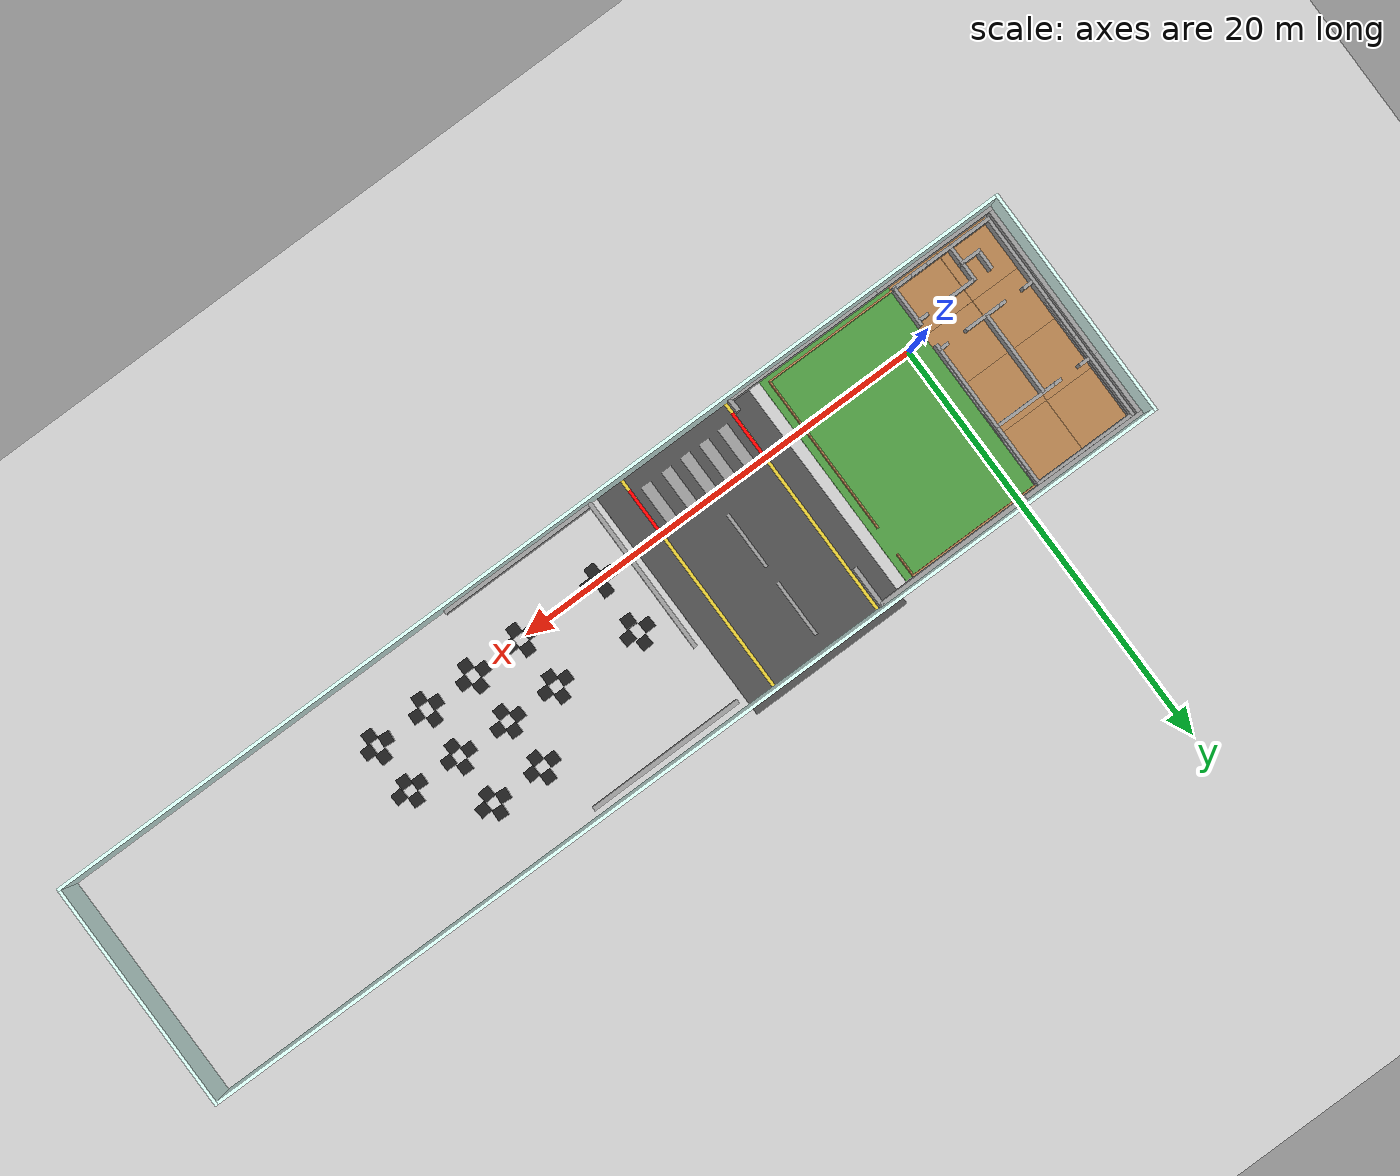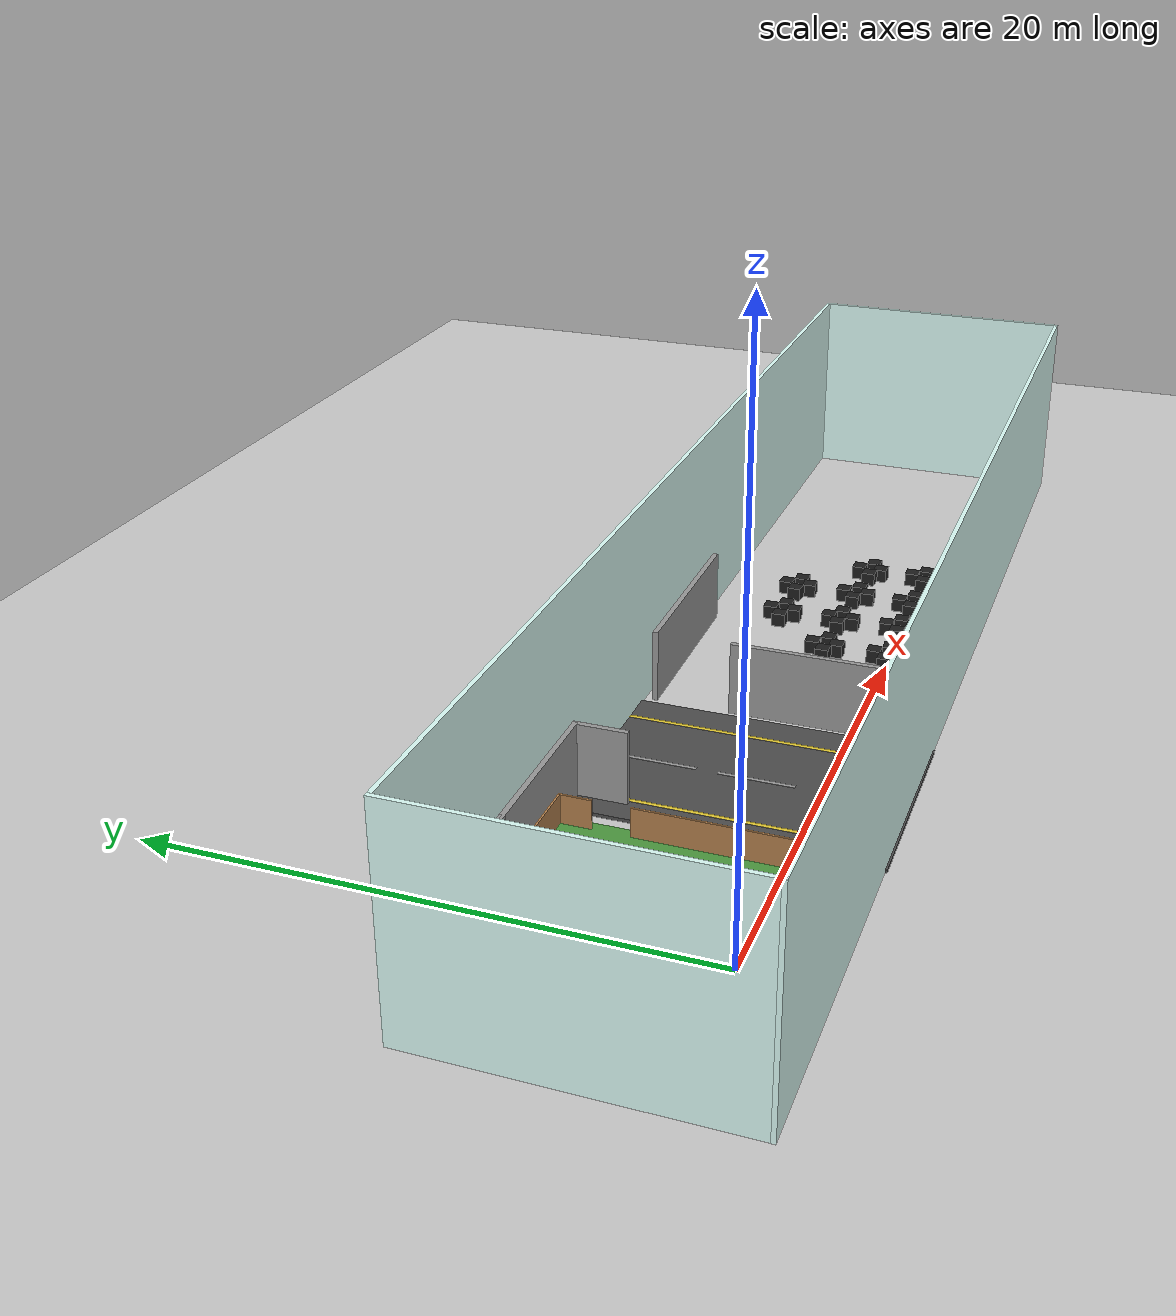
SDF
<sdf version="1.6">
 <world name="default">
  <light name="sun" type="directional">
   <pose>0 0 10 0 -0 0</pose>
   <diffuse>0.8 0.8 0.8 1</diffuse>
   <specular>0.2 0.2 0.2 1</specular>
   <attenuation>
    <range>1000</range>
    <constant>0.9</constant>
    <linear>0.01</linear>
    <quadratic>0.001</quadratic>
   </attenuation>
   <direction>-0.5 0.1 -0.9</direction>
  </light>
  <model name="ground_plane">
   <static>1</static>
   <link name="link">
    <collision name="collision">
     <geometry><plane><normal>0 0 1</normal><size>100 100</size></plane></geometry>
     <surface>
      <contact><collide_bitmask>65535</collide_bitmask></contact>
      <friction><ode><mu>100</mu><mu2>50</mu2></ode></friction>
     </surface>
    </collision>
    <visual name="visual">
     <cast_shadows>0</cast_shadows>
     <geometry><plane><normal>0 0 1</normal><size>100 100</size></plane></geometry>
     <material>
      <script><uri>file://media/materials/scripts/gazebo.material</uri><name>Gazebo/Grey</name></script>
     </material>
    </visual>
   </link>
  </model>
  <gravity>0 0 -9.8</gravity>
  <magnetic_field>6e-06 2.3e-05 -4.2e-05</magnetic_field>
  <atmosphere type="adiabatic"/>
  <physics name="default_physics" default="0" type="ode">
   <max_step_size>0.001</max_step_size>
   <real_time_factor>1</real_time_factor>
   <real_time_update_rate>1000</real_time_update_rate>
  </physics>
  <scene><ambient>0.4 0.4 0.4 1</ambient><background>0.7 0.7 0.7 1</background><shadows>1</shadows></scene>
  <spherical_coordinates>
   <surface_model>EARTH_WGS84</surface_model>
   <latitude_deg>0</latitude_deg>
   <longitude_deg>0</longitude_deg>
   <elevation>0</elevation>
   <heading_deg>0</heading_deg>
  </spherical_coordinates>
  <model name="grey_wall">
   <static>1</static>
   <link name="link">
    <pose>0 0 1.4 0 -0 0</pose>
    <collision name="collision"><geometry><box><size>7.5 0.2 2.8</size></box></geometry></collision>
    <visual name="visual">
     <cast_shadows>0</cast_shadows>
     <geometry><box><size>7.5 0.2 2.8</size></box></geometry>
     <material>
      <script>
       <uri>model://grey_wall/materials/scripts</uri>
       <uri>model://grey_wall/materials/textures</uri>
       <name>vrc/grey_wall</name>
      </script>
     </material>
    </visual>
   </link>
   <pose>18.2315 7.51175 0 0 -0 0.005635</pose>
  </model>
  <model name="grey_wall_1">
   <static>1</static>
   <link name="link">
    <pose>0 0 1.4 0 -0 0</pose>
    <collision name="collision"><geometry><box><size>7.5 0.2 2.8</size></box></geometry></collision>
    <visual name="visual">
     <cast_shadows>0</cast_shadows>
     <geometry><box><size>7.5 0.2 2.8</size></box></geometry>
     <material>
      <script>
       <uri>model://grey_wall/materials/scripts</uri>
       <uri>model://grey_wall/materials/textures</uri>
       <name>vrc/grey_wall</name>
      </script>
     </material>
    </visual>
   </link>
   <pose>14.5585 0.893344 0 0 -0 1.56876</pose>
  </model>
  <model name="grey_wall_clone">
   <static>1</static>
   <link name="link">
    <pose>0 0 1.4 0 -0 0</pose>
    <collision name="collision"><geometry><box><size>7.5 0.2 2.8</size></box></geometry></collision>
    <visual name="visual">
     <cast_shadows>0</cast_shadows>
     <geometry><box><size>7.5 0.2 2.8</size></box></geometry>
     <material>
      <script>
       <uri>model://grey_wall/materials/scripts</uri>
       <uri>model://grey_wall/materials/textures</uri>
       <name>vrc/grey_wall</name>
      </script>
     </material>
    </visual>
   </link>
   <pose>18.3523 -2.72946 0 0 -0 0</pose>
  </model>
  <model name="mud_box">
   <static>1</static>
   <link name="link">
    <collision name="collision"><geometry><box><size>8 10 0.2</size></box></geometry></collision>
    <visual name="visual_1">
     <pose>-2 2.5 0 0 -0 0</pose>
     <cast_shadows>0</cast_shadows>
     <geometry><box><size>4 5 0.2</size></box></geometry>
     <material>
      <script>
       <uri>model://mud_box/materials/scripts</uri>
       <uri>model://mud_box/materials/textures</uri>
       <name>vrc/mud</name>
      </script>
     </material>
    </visual>
    <visual name="visual_2">
     <pose>2 2.5 0 0 -0 0</pose>
     <cast_shadows>0</cast_shadows>
     <geometry><box><size>4 5 0.2</size></box></geometry>
     <material>
      <script>
       <uri>model://mud_box/materials/scripts</uri>
       <uri>model://mud_box/materials/textures</uri>
       <name>vrc/mud</name>
      </script>
     </material>
    </visual>
    <visual name="visual_3">
     <pose>2 -2.5 0 0 -0 0</pose>
     <cast_shadows>0</cast_shadows>
     <geometry><box><size>4 5 0.2</size></box></geometry>
     <material>
      <script>
       <uri>model://mud_box/materials/scripts</uri>
       <uri>model://mud_box/materials/textures</uri>
       <name>vrc/mud</name>
      </script>
     </material>
    </visual>
    <visual name="visual_4">
     <pose>-2 -2.5 0 0 -0 0</pose>
     <cast_shadows>0</cast_shadows>
     <geometry><box><size>4 5 0.2</size></box></geometry>
     <material>
      <script>
       <uri>model://mud_box/materials/scripts</uri>
       <uri>model://mud_box/materials/textures</uri>
       <name>vrc/mud</name>
      </script>
     </material>
    </visual>
   </link>
   <pose>1.51756 2.62532 -0.053989 0 -0 0</pose>
  </model>
  <model name="grey_wall_clone_0_clone">
   <static>1</static>
   <link name="link">
    <pose>0 0 1.4 0 -0 0</pose>
    <collision name="collision"><geometry><box><size>7.5 0.2 2.8</size></box></geometry></collision>
    <visual name="visual">
     <cast_shadows>0</cast_shadows>
     <geometry><box><size>7.5 0.2 2.8</size></box></geometry>
     <material>
      <script>
       <uri>model://grey_wall/materials/scripts</uri>
       <uri>model://grey_wall/materials/textures</uri>
       <name>vrc/grey_wall</name>
      </script>
     </material>
    </visual>
   </link>
   <pose>3.58891 7.79807 -0 0 0 -3.13873</pose>
  </model>
  <model name="grey_wall_clone_0_clone_0">
   <static>1</static>
   <link name="link">
    <pose>0 0 1.4 0 -0 0</pose>
    <collision name="collision"><geometry><box><size>7.5 0.2 2.8</size></box></geometry></collision>
    <visual name="visual">
     <cast_shadows>0</cast_shadows>
     <geometry><box><size>7.5 0.2 2.8</size></box></geometry>
     <material>
      <script>
       <uri>model://grey_wall/materials/scripts</uri>
       <uri>model://grey_wall/materials/textures</uri>
       <name>vrc/grey_wall</name>
      </script>
     </material>
    </visual>
   </link>
   <pose>-2.42988 7.80474 0 0 -0 3.13686</pose>
  </model>
  <model name="grey_wall_clone_0_clone_0_clone">
   <static>1</static>
   <link name="link">
    <pose>0 0 1.4 0 -0 0</pose>
    <collision name="collision"><geometry><box><size>7.5 0.2 2.8</size></box></geometry></collision>
    <visual name="visual">
     <cast_shadows>0</cast_shadows>
     <geometry><box><size>7.5 0.2 2.8</size></box></geometry>
     <material>
      <script>
       <uri>model://grey_wall/materials/scripts</uri>
       <uri>model://grey_wall/materials/textures</uri>
       <name>vrc/grey_wall</name>
      </script>
     </material>
    </visual>
   </link>
   <pose>3.51451 -2.7816 0 0 -0 3.13686</pose>
  </model>
  <model name="grey_wall_clone_0_clone_0_clone_0">
   <static>1</static>
   <link name="link">
    <pose>0 0 1.4 0 -0 0</pose>
    <collision name="collision"><geometry><box><size>7.5 0.2 2.8</size></box></geometry></collision>
    <visual name="visual">
     <cast_shadows>0</cast_shadows>
     <geometry><box><size>7.5 0.2 2.8</size></box></geometry>
     <material>
      <script>
       <uri>model://grey_wall/materials/scripts</uri>
       <uri>model://grey_wall/materials/textures</uri>
       <name>vrc/grey_wall</name>
      </script>
     </material>
    </visual>
   </link>
   <pose>-2.44151 -2.75862 0 0 -0 3.13686</pose>
  </model>
  <model name="grey_wall_clone_0_clone_0_clone_1">
   <static>1</static>
   <link name="link">
    <pose>0 0 1.4 0 -0 0</pose>
    <collision name="collision"><geometry><box><size>7.5 0.2 2.8</size></box></geometry></collision>
    <visual name="visual">
     <cast_shadows>0</cast_shadows>
     <geometry><box><size>7.5 0.2 2.8</size></box></geometry>
     <material>
      <script>
       <uri>model://grey_wall/materials/scripts</uri>
       <uri>model://grey_wall/materials/textures</uri>
       <name>vrc/grey_wall</name>
      </script>
     </material>
    </visual>
   </link>
   <pose>-6.06193 0.948078 0 0 0 -1.57307</pose>
  </model>
  <model name="grey_wall_clone_0_clone_0_clone_2">
   <static>1</static>
   <link name="link">
    <pose>0 0 1.4 0 -0 0</pose>
    <collision name="collision"><geometry><box><size>7.5 0.2 2.8</size></box></geometry></collision>
    <visual name="visual">
     <cast_shadows>0</cast_shadows>
     <geometry><box><size>7.5 0.2 2.8</size></box></geometry>
     <material>
      <script>
       <uri>model://grey_wall/materials/scripts</uri>
       <uri>model://grey_wall/materials/textures</uri>
       <name>vrc/grey_wall</name>
      </script>
     </material>
    </visual>
   </link>
   <pose>-6.05351 4.16462 0 0 -0 1.57226</pose>
  </model>
  <model name="grass">
   <link name="Wall_4">
    <pose>0 0 0 0 -0 1.5708</pose>
    <inertial>
     <mass>1</mass>
     <inertia><ixx>1</ixx><ixy>0</ixy><ixz>0</ixz><iyy>1</iyy><iyz>0</iyz><izz>1</izz></inertia>
    </inertial>
    <visual name="Wall_4_Visual">
     <pose>0 0 0.25 0 -0 0</pose>
     <geometry><box><size>10.5 7 0.5</size></box></geometry>
     <material>
      <script><uri>file://media/materials/scripts/gazebo.material</uri><name>Gazebo/Grass</name></script>
      <ambient>0.435 0.796 0.675 1</ambient>
      <shader type="vertex"><normal_map>__default__</normal_map></shader>
      <diffuse>0.7 0.7 0.7 1</diffuse>
      <specular>0.01 0.01 0.01 1</specular>
      <emissive>0 0 0 1</emissive>
     </material>
     <meta><layer>0</layer></meta>
    </visual>
    <collision name="collision_0">
     <pose>10.95 6.2 0.5 0 -0 0</pose>
     <geometry><box><size>10.95 6.2 0.5</size></box></geometry>
     <surface>
      <friction>
       <ode><mu>1</mu><mu2>1</mu2><fdir1>0 0 0</fdir1><slip1>0</slip1><slip2>0</slip2></ode>
       <torsional>
        <coefficient>1</coefficient>
        <patch_radius>0</patch_radius>
        <surface_radius>0</surface_radius>
        <use_patch_radius>1</use_patch_radius>
        <ode><slip>0</slip></ode>
       </torsional>
      </friction>
      <bounce><restitution_coefficient>0</restitution_coefficient><threshold>1e+06</threshold></bounce>
      <contact>
       <collide_without_contact>0</collide_without_contact>
       <collide_without_contact_bitmask>1</collide_without_contact_bitmask>
       <collide_bitmask>1</collide_bitmask>
       <ode>
        <soft_cfm>0</soft_cfm>
        <soft_erp>0.2</soft_erp>
        <kp>1e+13</kp>
        <kd>1</kd>
        <max_vel>0.01</max_vel>
        <min_depth>0</min_depth>
       </ode>
       <bullet>
        <split_impulse>1</split_impulse>
        <split_impulse_penetration_threshold>-0.01</split_impulse_penetration_threshold>
        <soft_cfm>0</soft_cfm>
        <soft_erp>0.2</soft_erp>
        <kp>1e+13</kp>
        <kd>1</kd>
       </bullet>
      </contact>
     </surface>
    </collision>
   </link>
   <static>1</static>
   <pose>2.32059 2.42329 -0.447772 0 0 -0.00069</pose>
  </model>
  <model name="grey_wall_clone_0">
   <link name="link">
    <pose>2.90621 0.028382 1.4 0 -0 0</pose>
    <inertial>
     <mass>1</mass>
     <inertia><ixx>1</ixx><ixy>0</ixy><ixz>0</ixz><iyy>1</iyy><iyz>0</iyz><izz>1</izz></inertia>
    </inertial>
    <visual name="visual">
     <cast_shadows>0</cast_shadows>
     <geometry><box><size>2 0.2 2.8</size></box></geometry>
     <material>
      <script>
       <uri>model://grey_wall/materials/scripts</uri>
       <uri>model://grey_wall/materials/textures</uri>
       <name>vrc/grey_wall</name>
      </script>
      <shader type="pixel"><normal_map>__default__</normal_map></shader>
      <ambient>1 1 1 1</ambient>
      <diffuse>1 1 1 1</diffuse>
      <specular>0 0 0 1</specular>
      <emissive>0 0 0 1</emissive>
     </material>
    </visual>
    <collision name="collision">
     <geometry><box><size>2 0.2 2.8</size></box></geometry>
     <surface>
      <friction>
       <ode><mu>1</mu><mu2>1</mu2><fdir1>0 0 0</fdir1><slip1>0</slip1><slip2>0</slip2></ode>
       <torsional>
        <coefficient>1</coefficient>
        <patch_radius>0</patch_radius>
        <surface_radius>0</surface_radius>
        <use_patch_radius>1</use_patch_radius>
        <ode><slip>0</slip></ode>
       </torsional>
      </friction>
      <bounce><restitution_coefficient>0</restitution_coefficient><threshold>1e+06</threshold></bounce>
      <contact>
       <collide_without_contact>0</collide_without_contact>
       <collide_without_contact_bitmask>1</collide_without_contact_bitmask>
       <collide_bitmask>1</collide_bitmask>
       <ode>
        <soft_cfm>0</soft_cfm>
        <soft_erp>0.2</soft_erp>
        <kp>1e+13</kp>
        <kd>1</kd>
        <max_vel>0.01</max_vel>
        <min_depth>0</min_depth>
       </ode>
       <bullet>
        <split_impulse>1</split_impulse>
        <split_impulse_penetration_threshold>-0.01</split_impulse_penetration_threshold>
        <soft_cfm>0</soft_cfm>
        <soft_erp>0.2</soft_erp>
        <kp>1e+13</kp>
        <kd>1</kd>
       </bullet>
      </contact>
     </surface>
    </collision>
   </link>
   <static>1</static>
   <pose>7.26761 9.82843 0 0 0 -1.57</pose>
  </model>
  <model name="grey_wall_clone_0_clone_1">
   <link name="link">
    <pose>0 0 1.4 0 -0 0</pose>
    <inertial>
     <mass>1</mass>
     <inertia><ixx>1</ixx><ixy>0</ixy><ixz>0</ixz><iyy>1</iyy><iyz>0</iyz><izz>1</izz></inertia>
    </inertial>
    <visual name="visual">
     <cast_shadows>0</cast_shadows>
     <geometry><box><size>0.75 0.2 2.8</size></box></geometry>
     <material>
      <script>
       <uri>model://grey_wall/materials/scripts</uri>
       <uri>model://grey_wall/materials/textures</uri>
       <name>vrc/grey_wall</name>
      </script>
      <shader type="pixel"><normal_map>__default__</normal_map></shader>
      <ambient>1 1 1 1</ambient>
      <diffuse>1 1 1 1</diffuse>
      <specular>0 0 0 1</specular>
      <emissive>0 0 0 1</emissive>
     </material>
    </visual>
    <collision name="collision">
     <geometry><box><size>0.75 0.2 2.8</size></box></geometry>
     <surface>
      <friction>
       <ode><mu>1</mu><mu2>1</mu2><fdir1>0 0 0</fdir1><slip1>0</slip1><slip2>0</slip2></ode>
       <torsional>
        <coefficient>1</coefficient>
        <patch_radius>0</patch_radius>
        <surface_radius>0</surface_radius>
        <use_patch_radius>1</use_patch_radius>
        <ode><slip>0</slip></ode>
       </torsional>
      </friction>
      <bounce><restitution_coefficient>0</restitution_coefficient><threshold>1e+06</threshold></bounce>
      <contact>
       <collide_without_contact>0</collide_without_contact>
       <collide_without_contact_bitmask>1</collide_without_contact_bitmask>
       <collide_bitmask>1</collide_bitmask>
       <ode>
        <soft_cfm>0</soft_cfm>
        <soft_erp>0.2</soft_erp>
        <kp>1e+13</kp>
        <kd>1</kd>
        <max_vel>0.01</max_vel>
        <min_depth>0</min_depth>
       </ode>
       <bullet>
        <split_impulse>1</split_impulse>
        <split_impulse_penetration_threshold>-0.01</split_impulse_penetration_threshold>
        <soft_cfm>0</soft_cfm>
        <soft_erp>0.2</soft_erp>
        <kp>1e+13</kp>
        <kd>1</kd>
       </bullet>
      </contact>
     </surface>
    </collision>
   </link>
   <static>1</static>
   <pose>7.30492 -2.5737 0 0 0 -1.54624</pose>
  </model>
  <model name="unit_box_0_clone_22_clone_15">
   <link name="link">
    <inertial>
     <mass>1</mass>
     <inertia>
      <ixx>0.166667</ixx>
      <ixy>0</ixy>
      <ixz>0</ixz>
      <iyy>0.166667</iyy>
      <iyz>0</iyz>
      <izz>0.166667</izz>
     </inertia>
    </inertial>
    <visual name="visual">
     <geometry><box><size>0.530101 0.530101 0.530101</size></box></geometry>
     <material>
      <script><name>Gazebo/FlatBlack</name><uri>file://media/materials/scripts/gazebo.material</uri></script>
      <shader type="pixel"><normal_map>__default__</normal_map></shader>
      <ambient>0.1 0.1 0.1 1</ambient>
      <diffuse>0.1 0.1 0.1 1</diffuse>
      <specular>0.01 0.01 0.01 1</specular>
      <emissive>0 0 0 1</emissive>
     </material>
    </visual>
    <collision name="collision">
     <geometry><box><size>0.530101 0.530101 0.530101</size></box></geometry>
     <surface>
      <friction>
       <ode><mu>1</mu><mu2>1</mu2><fdir1>0 0 0</fdir1><slip1>0</slip1><slip2>0</slip2></ode>
       <torsional>
        <coefficient>1</coefficient>
        <patch_radius>0</patch_radius>
        <surface_radius>0</surface_radius>
        <use_patch_radius>1</use_patch_radius>
        <ode><slip>0</slip></ode>
       </torsional>
      </friction>
      <bounce><restitution_coefficient>0</restitution_coefficient><threshold>1e+06</threshold></bounce>
      <contact>
       <collide_without_contact>0</collide_without_contact>
       <collide_without_contact_bitmask>1</collide_without_contact_bitmask>
       <collide_bitmask>1</collide_bitmask>
       <ode>
        <soft_cfm>0</soft_cfm>
        <soft_erp>0.2</soft_erp>
        <kp>1e+13</kp>
        <kd>1</kd>
        <max_vel>0.01</max_vel>
        <min_depth>0</min_depth>
       </ode>
       <bullet>
        <split_impulse>1</split_impulse>
        <split_impulse_penetration_threshold>-0.01</split_impulse_penetration_threshold>
        <soft_cfm>0</soft_cfm>
        <soft_erp>0.2</soft_erp>
        <kp>1e+13</kp>
        <kd>1</kd>
       </bullet>
      </contact>
     </surface>
    </collision>
   </link>
   <static>0</static>
   <pose>16.1737 2.09638 0.284665 0.077045 0 -0.016615</pose>
  </model>
  <model name="unit_box_0_clone_13">
   <link name="link">
    <inertial>
     <mass>1</mass>
     <inertia>
      <ixx>0.166667</ixx>
      <ixy>0</ixy>
      <ixz>0</ixz>
      <iyy>0.166667</iyy>
      <iyz>0</iyz>
      <izz>0.166667</izz>
     </inertia>
    </inertial>
    <visual name="visual">
     <geometry><box><size>0.530101 0.530101 0.530101</size></box></geometry>
     <material>
      <script><name>Gazebo/FlatBlack</name><uri>file://media/materials/scripts/gazebo.material</uri></script>
      <shader type="pixel"><normal_map>__default__</normal_map></shader>
      <ambient>0.1 0.1 0.1 1</ambient>
      <diffuse>0.1 0.1 0.1 1</diffuse>
      <specular>0.01 0.01 0.01 1</specular>
      <emissive>0 0 0 1</emissive>
     </material>
    </visual>
    <collision name="collision">
     <geometry><box><size>0.530101 0.530101 0.530101</size></box></geometry>
     <surface>
      <friction>
       <ode><mu>1</mu><mu2>1</mu2><fdir1>0 0 0</fdir1><slip1>0</slip1><slip2>0</slip2></ode>
       <torsional>
        <coefficient>1</coefficient>
        <patch_radius>0</patch_radius>
        <surface_radius>0</surface_radius>
        <use_patch_radius>1</use_patch_radius>
        <ode><slip>0</slip></ode>
       </torsional>
      </friction>
      <bounce><restitution_coefficient>0</restitution_coefficient><threshold>1e+06</threshold></bounce>
      <contact>
       <collide_without_contact>0</collide_without_contact>
       <collide_without_contact_bitmask>1</collide_without_contact_bitmask>
       <collide_bitmask>1</collide_bitmask>
       <ode>
        <soft_cfm>0</soft_cfm>
        <soft_erp>0.2</soft_erp>
        <kp>1e+13</kp>
        <kd>1</kd>
        <max_vel>0.01</max_vel>
        <min_depth>0</min_depth>
       </ode>
       <bullet>
        <split_impulse>1</split_impulse>
        <split_impulse_penetration_threshold>-0.01</split_impulse_penetration_threshold>
        <soft_cfm>0</soft_cfm>
        <soft_erp>0.2</soft_erp>
        <kp>1e+13</kp>
        <kd>1</kd>
       </bullet>
      </contact>
     </surface>
    </collision>
   </link>
   <static>0</static>
   <pose>22.1517 4.84185 0.314113 0 -0 0.013982</pose>
  </model>
  <model name="unit_box_0_clone_22_clone_14">
   <link name="link">
    <inertial>
     <mass>1</mass>
     <inertia>
      <ixx>0.166667</ixx>
      <ixy>0</ixy>
      <ixz>0</ixz>
      <iyy>0.166667</iyy>
      <iyz>0</iyz>
      <izz>0.166667</izz>
     </inertia>
    </inertial>
    <visual name="visual">
     <geometry><box><size>0.530101 0.530101 0.530101</size></box></geometry>
     <material>
      <script><name>Gazebo/FlatBlack</name><uri>file://media/materials/scripts/gazebo.material</uri></script>
      <shader type="pixel"><normal_map>__default__</normal_map></shader>
      <ambient>0.1 0.1 0.1 1</ambient>
      <diffuse>0.1 0.1 0.1 1</diffuse>
      <specular>0.01 0.01 0.01 1</specular>
      <emissive>0 0 0 1</emissive>
     </material>
    </visual>
    <collision name="collision">
     <geometry><box><size>0.530101 0.530101 0.530101</size></box></geometry>
     <surface>
      <friction>
       <ode><mu>1</mu><mu2>1</mu2><fdir1>0 0 0</fdir1><slip1>0</slip1><slip2>0</slip2></ode>
       <torsional>
        <coefficient>1</coefficient>
        <patch_radius>0</patch_radius>
        <surface_radius>0</surface_radius>
        <use_patch_radius>1</use_patch_radius>
        <ode><slip>0</slip></ode>
       </torsional>
      </friction>
      <bounce><restitution_coefficient>0</restitution_coefficient><threshold>1e+06</threshold></bounce>
      <contact>
       <collide_without_contact>0</collide_without_contact>
       <collide_without_contact_bitmask>1</collide_without_contact_bitmask>
       <collide_bitmask>1</collide_bitmask>
       <ode>
        <soft_cfm>0</soft_cfm>
        <soft_erp>0.2</soft_erp>
        <kp>1e+13</kp>
        <kd>1</kd>
        <max_vel>0.01</max_vel>
        <min_depth>0</min_depth>
       </ode>
       <bullet>
        <split_impulse>1</split_impulse>
        <split_impulse_penetration_threshold>-0.01</split_impulse_penetration_threshold>
        <soft_cfm>0</soft_cfm>
        <soft_erp>0.2</soft_erp>
        <kp>1e+13</kp>
        <kd>1</kd>
       </bullet>
      </contact>
     </surface>
    </collision>
   </link>
   <static>0</static>
   <pose>22.7398 5.34918 0.314111 5e-06 -1.1e-05 0.020813</pose>
  </model>
  <model name="unit_box_0_clone_22_clone_23">
   <link name="link">
    <inertial>
     <mass>1</mass>
     <inertia>
      <ixx>0.166667</ixx>
      <ixy>0</ixy>
      <ixz>0</ixz>
      <iyy>0.166667</iyy>
      <iyz>0</iyz>
      <izz>0.166667</izz>
     </inertia>
    </inertial>
    <visual name="visual">
     <geometry><box><size>0.530101 0.530101 0.530101</size></box></geometry>
     <material>
      <script><name>Gazebo/FlatBlack</name><uri>file://media/materials/scripts/gazebo.material</uri></script>
      <shader type="pixel"><normal_map>__default__</normal_map></shader>
      <ambient>0.1 0.1 0.1 1</ambient>
      <diffuse>0.1 0.1 0.1 1</diffuse>
      <specular>0.01 0.01 0.01 1</specular>
      <emissive>0 0 0 1</emissive>
     </material>
    </visual>
    <collision name="collision">
     <geometry><box><size>0.530101 0.530101 0.530101</size></box></geometry>
     <surface>
      <friction>
       <ode><mu>1</mu><mu2>1</mu2><fdir1>0 0 0</fdir1><slip1>0</slip1><slip2>0</slip2></ode>
       <torsional>
        <coefficient>1</coefficient>
        <patch_radius>0</patch_radius>
        <surface_radius>0</surface_radius>
        <use_patch_radius>1</use_patch_radius>
        <ode><slip>0</slip></ode>
       </torsional>
      </friction>
      <bounce><restitution_coefficient>0</restitution_coefficient><threshold>1e+06</threshold></bounce>
      <contact>
       <collide_without_contact>0</collide_without_contact>
       <collide_without_contact_bitmask>1</collide_without_contact_bitmask>
       <collide_bitmask>1</collide_bitmask>
       <ode>
        <soft_cfm>0</soft_cfm>
        <soft_erp>0.2</soft_erp>
        <kp>1e+13</kp>
        <kd>1</kd>
        <max_vel>0.01</max_vel>
        <min_depth>0</min_depth>
       </ode>
       <bullet>
        <split_impulse>1</split_impulse>
        <split_impulse_penetration_threshold>-0.01</split_impulse_penetration_threshold>
        <soft_cfm>0</soft_cfm>
        <soft_erp>0.2</soft_erp>
        <kp>1e+13</kp>
        <kd>1</kd>
       </bullet>
      </contact>
     </surface>
    </collision>
   </link>
   <static>0</static>
   <pose>22.7259 4.38549 0.314113 0 -0 0.047968</pose>
  </model>
  <model name="unit_box_0_clone_22_clone_24">
   <link name="link">
    <inertial>
     <mass>1</mass>
     <inertia>
      <ixx>0.166667</ixx>
      <ixy>0</ixy>
      <ixz>0</ixz>
      <iyy>0.166667</iyy>
      <iyz>0</iyz>
      <izz>0.166667</izz>
     </inertia>
    </inertial>
    <visual name="visual">
     <geometry><box><size>0.530101 0.530101 0.530101</size></box></geometry>
     <material>
      <script><name>Gazebo/FlatBlack</name><uri>file://media/materials/scripts/gazebo.material</uri></script>
      <shader type="pixel"><normal_map>__default__</normal_map></shader>
      <ambient>0.1 0.1 0.1 1</ambient>
      <diffuse>0.1 0.1 0.1 1</diffuse>
      <specular>0.01 0.01 0.01 1</specular>
      <emissive>0 0 0 1</emissive>
     </material>
    </visual>
    <collision name="collision">
     <geometry><box><size>0.530101 0.530101 0.530101</size></box></geometry>
     <surface>
      <friction>
       <ode><mu>1</mu><mu2>1</mu2><fdir1>0 0 0</fdir1><slip1>0</slip1><slip2>0</slip2></ode>
       <torsional>
        <coefficient>1</coefficient>
        <patch_radius>0</patch_radius>
        <surface_radius>0</surface_radius>
        <use_patch_radius>1</use_patch_radius>
        <ode><slip>0</slip></ode>
       </torsional>
      </friction>
      <bounce><restitution_coefficient>0</restitution_coefficient><threshold>1e+06</threshold></bounce>
      <contact>
       <collide_without_contact>0</collide_without_contact>
       <collide_without_contact_bitmask>1</collide_without_contact_bitmask>
       <collide_bitmask>1</collide_bitmask>
       <ode>
        <soft_cfm>0</soft_cfm>
        <soft_erp>0.2</soft_erp>
        <kp>1e+13</kp>
        <kd>1</kd>
        <max_vel>0.01</max_vel>
        <min_depth>0</min_depth>
       </ode>
       <bullet>
        <split_impulse>1</split_impulse>
        <split_impulse_penetration_threshold>-0.01</split_impulse_penetration_threshold>
        <soft_cfm>0</soft_cfm>
        <soft_erp>0.2</soft_erp>
        <kp>1e+13</kp>
        <kd>1</kd>
       </bullet>
      </contact>
     </surface>
    </collision>
   </link>
   <static>0</static>
   <pose>23.2352 4.8352 0.314113 0 -0 0.048299</pose>
  </model>
  <model name="unit_box_0_clone_10">
   <link name="link">
    <inertial>
     <mass>1</mass>
     <inertia>
      <ixx>0.166667</ixx>
      <ixy>0</ixy>
      <ixz>0</ixz>
      <iyy>0.166667</iyy>
      <iyz>0</iyz>
      <izz>0.166667</izz>
     </inertia>
    </inertial>
    <visual name="visual">
     <geometry><box><size>0.530101 0.530101 0.530101</size></box></geometry>
     <material>
      <script><name>Gazebo/FlatBlack</name><uri>file://media/materials/scripts/gazebo.material</uri></script>
      <shader type="pixel"><normal_map>__default__</normal_map></shader>
      <ambient>0.1 0.1 0.1 1</ambient>
      <diffuse>0.1 0.1 0.1 1</diffuse>
      <specular>0.01 0.01 0.01 1</specular>
      <emissive>0 0 0 1</emissive>
     </material>
    </visual>
    <collision name="collision">
     <geometry><box><size>0.530101 0.530101 0.530101</size></box></geometry>
     <surface>
      <friction>
       <ode><mu>1</mu><mu2>1</mu2><fdir1>0 0 0</fdir1><slip1>0</slip1><slip2>0</slip2></ode>
       <torsional>
        <coefficient>1</coefficient>
        <patch_radius>0</patch_radius>
        <surface_radius>0</surface_radius>
        <use_patch_radius>1</use_patch_radius>
        <ode><slip>0</slip></ode>
       </torsional>
      </friction>
      <bounce><restitution_coefficient>0</restitution_coefficient><threshold>1e+06</threshold></bounce>
      <contact>
       <collide_without_contact>0</collide_without_contact>
       <collide_without_contact_bitmask>1</collide_without_contact_bitmask>
       <collide_bitmask>1</collide_bitmask>
       <ode>
        <soft_cfm>0</soft_cfm>
        <soft_erp>0.2</soft_erp>
        <kp>1e+13</kp>
        <kd>1</kd>
        <max_vel>0.01</max_vel>
        <min_depth>0</min_depth>
       </ode>
       <bullet>
        <split_impulse>1</split_impulse>
        <split_impulse_penetration_threshold>-0.01</split_impulse_penetration_threshold>
        <soft_cfm>0</soft_cfm>
        <soft_erp>0.2</soft_erp>
        <kp>1e+13</kp>
        <kd>1</kd>
       </bullet>
      </contact>
     </surface>
    </collision>
   </link>
   <static>0</static>
   <pose>20.223 2.01564 0.314108 -7e-06 1.1e-05 -0.02247</pose>
  </model>
  <model name="unit_box_0_clone_22_clone_4">
   <link name="link">
    <inertial>
     <mass>1</mass>
     <inertia>
      <ixx>0.166667</ixx>
      <ixy>0</ixy>
      <ixz>0</ixz>
      <iyy>0.166667</iyy>
      <iyz>0</iyz>
      <izz>0.166667</izz>
     </inertia>
    </inertial>
    <visual name="visual">
     <geometry><box><size>0.530101 0.530101 0.530101</size></box></geometry>
     <material>
      <script><name>Gazebo/FlatBlack</name><uri>file://media/materials/scripts/gazebo.material</uri></script>
      <shader type="pixel"><normal_map>__default__</normal_map></shader>
      <ambient>0.1 0.1 0.1 1</ambient>
      <diffuse>0.1 0.1 0.1 1</diffuse>
      <specular>0.01 0.01 0.01 1</specular>
      <emissive>0 0 0 1</emissive>
     </material>
    </visual>
    <collision name="collision">
     <geometry><box><size>0.530101 0.530101 0.530101</size></box></geometry>
     <surface>
      <friction>
       <ode><mu>1</mu><mu2>1</mu2><fdir1>0 0 0</fdir1><slip1>0</slip1><slip2>0</slip2></ode>
       <torsional>
        <coefficient>1</coefficient>
        <patch_radius>0</patch_radius>
        <surface_radius>0</surface_radius>
        <use_patch_radius>1</use_patch_radius>
        <ode><slip>0</slip></ode>
       </torsional>
      </friction>
      <bounce><restitution_coefficient>0</restitution_coefficient><threshold>1e+06</threshold></bounce>
      <contact>
       <collide_without_contact>0</collide_without_contact>
       <collide_without_contact_bitmask>1</collide_without_contact_bitmask>
       <collide_bitmask>1</collide_bitmask>
       <ode>
        <soft_cfm>0</soft_cfm>
        <soft_erp>0.2</soft_erp>
        <kp>1e+13</kp>
        <kd>1</kd>
        <max_vel>0.01</max_vel>
        <min_depth>0</min_depth>
       </ode>
       <bullet>
        <split_impulse>1</split_impulse>
        <split_impulse_penetration_threshold>-0.01</split_impulse_penetration_threshold>
        <soft_cfm>0</soft_cfm>
        <soft_erp>0.2</soft_erp>
        <kp>1e+13</kp>
        <kd>1</kd>
       </bullet>
      </contact>
     </surface>
    </collision>
   </link>
   <static>0</static>
   <pose>19.699 2.43698 0.31411 2e-06 -8e-06 -0.010485</pose>
  </model>
  <model name="unit_box_0_clone_28">
   <link name="link">
    <inertial>
     <mass>1</mass>
     <inertia>
      <ixx>0.166667</ixx>
      <ixy>0</ixy>
      <ixz>0</ixz>
      <iyy>0.166667</iyy>
      <iyz>0</iyz>
      <izz>0.166667</izz>
     </inertia>
    </inertial>
    <visual name="visual">
     <geometry><box><size>0.530101 0.530101 0.530101</size></box></geometry>
     <material>
      <script><name>Gazebo/FlatBlack</name><uri>file://media/materials/scripts/gazebo.material</uri></script>
      <shader type="pixel"><normal_map>__default__</normal_map></shader>
      <ambient>0.1 0.1 0.1 1</ambient>
      <diffuse>0.1 0.1 0.1 1</diffuse>
      <specular>0.01 0.01 0.01 1</specular>
      <emissive>0 0 0 1</emissive>
     </material>
    </visual>
    <collision name="collision">
     <geometry><box><size>0.530101 0.530101 0.530101</size></box></geometry>
     <surface>
      <friction>
       <ode><mu>1</mu><mu2>1</mu2><fdir1>0 0 0</fdir1><slip1>0</slip1><slip2>0</slip2></ode>
       <torsional>
        <coefficient>1</coefficient>
        <patch_radius>0</patch_radius>
        <surface_radius>0</surface_radius>
        <use_patch_radius>1</use_patch_radius>
        <ode><slip>0</slip></ode>
       </torsional>
      </friction>
      <bounce><restitution_coefficient>0</restitution_coefficient><threshold>1e+06</threshold></bounce>
      <contact>
       <collide_without_contact>0</collide_without_contact>
       <collide_without_contact_bitmask>1</collide_without_contact_bitmask>
       <collide_bitmask>1</collide_bitmask>
       <ode>
        <soft_cfm>0</soft_cfm>
        <soft_erp>0.2</soft_erp>
        <kp>1e+13</kp>
        <kd>1</kd>
        <max_vel>0.01</max_vel>
        <min_depth>0</min_depth>
       </ode>
       <bullet>
        <split_impulse>1</split_impulse>
        <split_impulse_penetration_threshold>-0.01</split_impulse_penetration_threshold>
        <soft_cfm>0</soft_cfm>
        <soft_erp>0.2</soft_erp>
        <kp>1e+13</kp>
        <kd>1</kd>
       </bullet>
      </contact>
     </surface>
    </collision>
   </link>
   <static>0</static>
   <pose>20.2602 2.98412 0.314111 1.1e-05 -6e-06 0.028537</pose>
  </model>
  <model name="unit_box_0_clone_22_clone_15_clone">
   <link name="link">
    <inertial>
     <mass>1</mass>
     <inertia>
      <ixx>0.166667</ixx>
      <ixy>0</ixy>
      <ixz>0</ixz>
      <iyy>0.166667</iyy>
      <iyz>0</iyz>
      <izz>0.166667</izz>
     </inertia>
    </inertial>
    <visual name="visual">
     <geometry><box><size>0.530101 0.530101 0.530101</size></box></geometry>
     <material>
      <script><name>Gazebo/FlatBlack</name><uri>file://media/materials/scripts/gazebo.material</uri></script>
      <shader type="pixel"><normal_map>__default__</normal_map></shader>
      <ambient>0.1 0.1 0.1 1</ambient>
      <diffuse>0.1 0.1 0.1 1</diffuse>
      <specular>0.01 0.01 0.01 1</specular>
      <emissive>0 0 0 1</emissive>
     </material>
    </visual>
    <collision name="collision">
     <geometry><box><size>0.530101 0.530101 0.530101</size></box></geometry>
     <surface>
      <friction>
       <ode><mu>1</mu><mu2>1</mu2><fdir1>0 0 0</fdir1><slip1>0</slip1><slip2>0</slip2></ode>
       <torsional>
        <coefficient>1</coefficient>
        <patch_radius>0</patch_radius>
        <surface_radius>0</surface_radius>
        <use_patch_radius>1</use_patch_radius>
        <ode><slip>0</slip></ode>
       </torsional>
      </friction>
      <bounce><restitution_coefficient>0</restitution_coefficient><threshold>1e+06</threshold></bounce>
      <contact>
       <collide_without_contact>0</collide_without_contact>
       <collide_without_contact_bitmask>1</collide_without_contact_bitmask>
       <collide_bitmask>1</collide_bitmask>
       <ode>
        <soft_cfm>0</soft_cfm>
        <soft_erp>0.2</soft_erp>
        <kp>1e+13</kp>
        <kd>1</kd>
        <max_vel>0.01</max_vel>
        <min_depth>0</min_depth>
       </ode>
       <bullet>
        <split_impulse>1</split_impulse>
        <split_impulse_penetration_threshold>-0.01</split_impulse_penetration_threshold>
        <soft_cfm>0</soft_cfm>
        <soft_erp>0.2</soft_erp>
        <kp>1e+13</kp>
        <kd>1</kd>
       </bullet>
      </contact>
     </surface>
    </collision>
   </link>
   <static>0</static>
   <pose>16.6126 2.65833 0.310618 -0.001158 -0.020052 0.060121</pose>
  </model>
  <model name="unit_box_0_clone_22_clone_15_clone_0">
   <link name="link">
    <inertial>
     <mass>1</mass>
     <inertia>
      <ixx>0.166667</ixx>
      <ixy>0</ixy>
      <ixz>0</ixz>
      <iyy>0.166667</iyy>
      <iyz>0</iyz>
      <izz>0.166667</izz>
     </inertia>
    </inertial>
    <visual name="visual">
     <geometry><box><size>0.530101 0.530101 0.530101</size></box></geometry>
     <material>
      <script><name>Gazebo/FlatBlack</name><uri>file://media/materials/scripts/gazebo.material</uri></script>
      <shader type="pixel"><normal_map>__default__</normal_map></shader>
      <ambient>0.1 0.1 0.1 1</ambient>
      <diffuse>0.1 0.1 0.1 1</diffuse>
      <specular>0.01 0.01 0.01 1</specular>
      <emissive>0 0 0 1</emissive>
     </material>
    </visual>
    <collision name="collision">
     <geometry><box><size>0.530101 0.530101 0.530101</size></box></geometry>
     <surface>
      <friction>
       <ode><mu>1</mu><mu2>1</mu2><fdir1>0 0 0</fdir1><slip1>0</slip1><slip2>0</slip2></ode>
       <torsional>
        <coefficient>1</coefficient>
        <patch_radius>0</patch_radius>
        <surface_radius>0</surface_radius>
        <use_patch_radius>1</use_patch_radius>
        <ode><slip>0</slip></ode>
       </torsional>
      </friction>
      <bounce><restitution_coefficient>0</restitution_coefficient><threshold>1e+06</threshold></bounce>
      <contact>
       <collide_without_contact>0</collide_without_contact>
       <collide_without_contact_bitmask>1</collide_without_contact_bitmask>
       <collide_bitmask>1</collide_bitmask>
       <ode>
        <soft_cfm>0</soft_cfm>
        <soft_erp>0.2</soft_erp>
        <kp>1e+13</kp>
        <kd>1</kd>
        <max_vel>0.01</max_vel>
        <min_depth>0</min_depth>
       </ode>
       <bullet>
        <split_impulse>1</split_impulse>
        <split_impulse_penetration_threshold>-0.01</split_impulse_penetration_threshold>
        <soft_cfm>0</soft_cfm>
        <soft_erp>0.2</soft_erp>
        <kp>1e+13</kp>
        <kd>1</kd>
       </bullet>
      </contact>
     </surface>
    </collision>
   </link>
   <static>0</static>
   <pose>16.1648 3.22166 0.26505 0 -0 0.066212</pose>
  </model>
  <model name="unit_box_0_clone_22_clone_15_clone_1">
   <link name="link">
    <inertial>
     <mass>1</mass>
     <inertia>
      <ixx>0.166667</ixx>
      <ixy>0</ixy>
      <ixz>0</ixz>
      <iyy>0.166667</iyy>
      <iyz>0</iyz>
      <izz>0.166667</izz>
     </inertia>
    </inertial>
    <visual name="visual">
     <geometry><box><size>0.530101 0.530101 0.530101</size></box></geometry>
     <material>
      <script><name>Gazebo/FlatBlack</name><uri>file://media/materials/scripts/gazebo.material</uri></script>
      <shader type="pixel"><normal_map>__default__</normal_map></shader>
      <ambient>0.1 0.1 0.1 1</ambient>
      <diffuse>0.1 0.1 0.1 1</diffuse>
      <specular>0.01 0.01 0.01 1</specular>
      <emissive>0 0 0 1</emissive>
     </material>
    </visual>
    <collision name="collision">
     <geometry><box><size>0.530101 0.530101 0.530101</size></box></geometry>
     <surface>
      <friction>
       <ode><mu>1</mu><mu2>1</mu2><fdir1>0 0 0</fdir1><slip1>0</slip1><slip2>0</slip2></ode>
       <torsional>
        <coefficient>1</coefficient>
        <patch_radius>0</patch_radius>
        <surface_radius>0</surface_radius>
        <use_patch_radius>1</use_patch_radius>
        <ode><slip>0</slip></ode>
       </torsional>
      </friction>
      <bounce><restitution_coefficient>0</restitution_coefficient><threshold>1e+06</threshold></bounce>
      <contact>
       <collide_without_contact>0</collide_without_contact>
       <collide_without_contact_bitmask>1</collide_without_contact_bitmask>
       <collide_bitmask>1</collide_bitmask>
       <ode>
        <soft_cfm>0</soft_cfm>
        <soft_erp>0.2</soft_erp>
        <kp>1e+13</kp>
        <kd>1</kd>
        <max_vel>0.01</max_vel>
        <min_depth>0</min_depth>
       </ode>
       <bullet>
        <split_impulse>1</split_impulse>
        <split_impulse_penetration_threshold>-0.01</split_impulse_penetration_threshold>
        <soft_cfm>0</soft_cfm>
        <soft_erp>0.2</soft_erp>
        <kp>1e+13</kp>
        <kd>1</kd>
       </bullet>
      </contact>
     </surface>
    </collision>
   </link>
   <static>0</static>
   <pose>15.6259 2.67518 0.26505 0 -0 0.031191</pose>
  </model>
  <model name="unit_box_0_clone_22_clone_15_clone_2">
   <link name="link">
    <inertial>
     <mass>1</mass>
     <inertia>
      <ixx>0.166667</ixx>
      <ixy>0</ixy>
      <ixz>0</ixz>
      <iyy>0.166667</iyy>
      <iyz>0</iyz>
      <izz>0.166667</izz>
     </inertia>
    </inertial>
    <visual name="visual">
     <geometry><box><size>0.530101 0.530101 0.530101</size></box></geometry>
     <material>
      <script><name>Gazebo/FlatBlack</name><uri>file://media/materials/scripts/gazebo.material</uri></script>
      <shader type="pixel"><normal_map>__default__</normal_map></shader>
      <ambient>0.1 0.1 0.1 1</ambient>
      <diffuse>0.1 0.1 0.1 1</diffuse>
      <specular>0.01 0.01 0.01 1</specular>
      <emissive>0 0 0 1</emissive>
     </material>
    </visual>
    <collision name="collision">
     <geometry><box><size>0.530101 0.530101 0.530101</size></box></geometry>
     <surface>
      <friction>
       <ode><mu>1</mu><mu2>1</mu2><fdir1>0 0 0</fdir1><slip1>0</slip1><slip2>0</slip2></ode>
       <torsional>
        <coefficient>1</coefficient>
        <patch_radius>0</patch_radius>
        <surface_radius>0</surface_radius>
        <use_patch_radius>1</use_patch_radius>
        <ode><slip>0</slip></ode>
       </torsional>
      </friction>
      <bounce><restitution_coefficient>0</restitution_coefficient><threshold>1e+06</threshold></bounce>
      <contact>
       <collide_without_contact>0</collide_without_contact>
       <collide_without_contact_bitmask>1</collide_without_contact_bitmask>
       <collide_bitmask>1</collide_bitmask>
       <ode>
        <soft_cfm>0</soft_cfm>
        <soft_erp>0.2</soft_erp>
        <kp>1e+13</kp>
        <kd>1</kd>
        <max_vel>0.01</max_vel>
        <min_depth>0</min_depth>
       </ode>
       <bullet>
        <split_impulse>1</split_impulse>
        <split_impulse_penetration_threshold>-0.01</split_impulse_penetration_threshold>
        <soft_cfm>0</soft_cfm>
        <soft_erp>0.2</soft_erp>
        <kp>1e+13</kp>
        <kd>1</kd>
       </bullet>
      </contact>
     </surface>
    </collision>
   </link>
   <static>0</static>
   <pose>16.6778 -0.072849 0.311379 -0.000275 -0.023896 0.01374</pose>
  </model>
  <model name="unit_box_0_clone_22_clone_15_clone_3">
   <link name="link">
    <inertial>
     <mass>1</mass>
     <inertia>
      <ixx>0.166667</ixx>
      <ixy>0</ixy>
      <ixz>0</ixz>
      <iyy>0.166667</iyy>
      <iyz>0</iyz>
      <izz>0.166667</izz>
     </inertia>
    </inertial>
    <visual name="visual">
     <geometry><box><size>0.530101 0.530101 0.530101</size></box></geometry>
     <material>
      <script><name>Gazebo/FlatBlack</name><uri>file://media/materials/scripts/gazebo.material</uri></script>
      <shader type="pixel"><normal_map>__default__</normal_map></shader>
      <ambient>0.1 0.1 0.1 1</ambient>
      <diffuse>0.1 0.1 0.1 1</diffuse>
      <specular>0.01 0.01 0.01 1</specular>
      <emissive>0 0 0 1</emissive>
     </material>
    </visual>
    <collision name="collision">
     <geometry><box><size>0.530101 0.530101 0.530101</size></box></geometry>
     <surface>
      <friction>
       <ode><mu>1</mu><mu2>1</mu2><fdir1>0 0 0</fdir1><slip1>0</slip1><slip2>0</slip2></ode>
       <torsional>
        <coefficient>1</coefficient>
        <patch_radius>0</patch_radius>
        <surface_radius>0</surface_radius>
        <use_patch_radius>1</use_patch_radius>
        <ode><slip>0</slip></ode>
       </torsional>
      </friction>
      <bounce><restitution_coefficient>0</restitution_coefficient><threshold>1e+06</threshold></bounce>
      <contact>
       <collide_without_contact>0</collide_without_contact>
       <collide_without_contact_bitmask>1</collide_without_contact_bitmask>
       <collide_bitmask>1</collide_bitmask>
       <ode>
        <soft_cfm>0</soft_cfm>
        <soft_erp>0.2</soft_erp>
        <kp>1e+13</kp>
        <kd>1</kd>
        <max_vel>0.01</max_vel>
        <min_depth>0</min_depth>
       </ode>
       <bullet>
        <split_impulse>1</split_impulse>
        <split_impulse_penetration_threshold>-0.01</split_impulse_penetration_threshold>
        <soft_cfm>0</soft_cfm>
        <soft_erp>0.2</soft_erp>
        <kp>1e+13</kp>
        <kd>1</kd>
       </bullet>
      </contact>
     </surface>
    </collision>
   </link>
   <static>0</static>
   <pose>16.1475 0.465806 0.291749 -0.106231 -0.000338 -0.003302</pose>
  </model>
  <model name="unit_box_0_clone_22_clone_15_clone_4">
   <link name="link">
    <inertial>
     <mass>1</mass>
     <inertia>
      <ixx>0.166667</ixx>
      <ixy>0</ixy>
      <ixz>0</ixz>
      <iyy>0.166667</iyy>
      <iyz>0</iyz>
      <izz>0.166667</izz>
     </inertia>
    </inertial>
    <visual name="visual">
     <geometry><box><size>0.530101 0.530101 0.530101</size></box></geometry>
     <material>
      <script><name>Gazebo/FlatBlack</name><uri>file://media/materials/scripts/gazebo.material</uri></script>
      <shader type="pixel"><normal_map>__default__</normal_map></shader>
      <ambient>0.1 0.1 0.1 1</ambient>
      <diffuse>0.1 0.1 0.1 1</diffuse>
      <specular>0.01 0.01 0.01 1</specular>
      <emissive>0 0 0 1</emissive>
     </material>
    </visual>
    <collision name="collision">
     <geometry><box><size>0.530101 0.530101 0.530101</size></box></geometry>
     <surface>
      <friction>
       <ode><mu>1</mu><mu2>1</mu2><fdir1>0 0 0</fdir1><slip1>0</slip1><slip2>0</slip2></ode>
       <torsional>
        <coefficient>1</coefficient>
        <patch_radius>0</patch_radius>
        <surface_radius>0</surface_radius>
        <use_patch_radius>1</use_patch_radius>
        <ode><slip>0</slip></ode>
       </torsional>
      </friction>
      <bounce><restitution_coefficient>0</restitution_coefficient><threshold>1e+06</threshold></bounce>
      <contact>
       <collide_without_contact>0</collide_without_contact>
       <collide_without_contact_bitmask>1</collide_without_contact_bitmask>
       <collide_bitmask>1</collide_bitmask>
       <ode>
        <soft_cfm>0</soft_cfm>
        <soft_erp>0.2</soft_erp>
        <kp>1e+13</kp>
        <kd>1</kd>
        <max_vel>0.01</max_vel>
        <min_depth>0</min_depth>
       </ode>
       <bullet>
        <split_impulse>1</split_impulse>
        <split_impulse_penetration_threshold>-0.01</split_impulse_penetration_threshold>
        <soft_cfm>0</soft_cfm>
        <soft_erp>0.2</soft_erp>
        <kp>1e+13</kp>
        <kd>1</kd>
       </bullet>
      </contact>
     </surface>
    </collision>
   </link>
   <static>0</static>
   <pose>15.6128 -0.033067 0.26505 0 0 -0.001316</pose>
  </model>
  <model name="unit_box_0_clone_22_clone_15_clone_5">
   <link name="link">
    <inertial>
     <mass>1</mass>
     <inertia>
      <ixx>0.166667</ixx>
      <ixy>0</ixy>
      <ixz>0</ixz>
      <iyy>0.166667</iyy>
      <iyz>0</iyz>
      <izz>0.166667</izz>
     </inertia>
    </inertial>
    <visual name="visual">
     <geometry><box><size>0.530101 0.530101 0.530101</size></box></geometry>
     <material>
      <script><name>Gazebo/FlatBlack</name><uri>file://media/materials/scripts/gazebo.material</uri></script>
      <shader type="pixel"><normal_map>__default__</normal_map></shader>
      <ambient>0.1 0.1 0.1 1</ambient>
      <diffuse>0.1 0.1 0.1 1</diffuse>
      <specular>0.01 0.01 0.01 1</specular>
      <emissive>0 0 0 1</emissive>
     </material>
    </visual>
    <collision name="collision">
     <geometry><box><size>0.530101 0.530101 0.530101</size></box></geometry>
     <surface>
      <friction>
       <ode><mu>1</mu><mu2>1</mu2><fdir1>0 0 0</fdir1><slip1>0</slip1><slip2>0</slip2></ode>
       <torsional>
        <coefficient>1</coefficient>
        <patch_radius>0</patch_radius>
        <surface_radius>0</surface_radius>
        <use_patch_radius>1</use_patch_radius>
        <ode><slip>0</slip></ode>
       </torsional>
      </friction>
      <bounce><restitution_coefficient>0</restitution_coefficient><threshold>1e+06</threshold></bounce>
      <contact>
       <collide_without_contact>0</collide_without_contact>
       <collide_without_contact_bitmask>1</collide_without_contact_bitmask>
       <collide_bitmask>1</collide_bitmask>
       <ode>
        <soft_cfm>0</soft_cfm>
        <soft_erp>0.2</soft_erp>
        <kp>1e+13</kp>
        <kd>1</kd>
        <max_vel>0.01</max_vel>
        <min_depth>0</min_depth>
       </ode>
       <bullet>
        <split_impulse>1</split_impulse>
        <split_impulse_penetration_threshold>-0.01</split_impulse_penetration_threshold>
        <soft_cfm>0</soft_cfm>
        <soft_erp>0.2</soft_erp>
        <kp>1e+13</kp>
        <kd>1</kd>
       </bullet>
      </contact>
     </surface>
    </collision>
   </link>
   <static>0</static>
   <pose>16.1476 -0.467481 0.286463 0.082994 -0.001332 0.016014</pose>
  </model>
  <model name="unit_box_0_clone_22_clone_15_clone_6">
   <link name="link">
    <inertial>
     <mass>1</mass>
     <inertia>
      <ixx>0.166667</ixx>
      <ixy>0</ixy>
      <ixz>0</ixz>
      <iyy>0.166667</iyy>
      <iyz>0</iyz>
      <izz>0.166667</izz>
     </inertia>
    </inertial>
    <visual name="visual">
     <geometry><box><size>0.530101 0.530101 0.530101</size></box></geometry>
     <material>
      <script><name>Gazebo/FlatBlack</name><uri>file://media/materials/scripts/gazebo.material</uri></script>
      <shader type="pixel"><normal_map>__default__</normal_map></shader>
      <ambient>0.1 0.1 0.1 1</ambient>
      <diffuse>0.1 0.1 0.1 1</diffuse>
      <specular>0.01 0.01 0.01 1</specular>
      <emissive>0 0 0 1</emissive>
     </material>
    </visual>
    <collision name="collision">
     <geometry><box><size>0.530101 0.530101 0.530101</size></box></geometry>
     <surface>
      <friction>
       <ode><mu>1</mu><mu2>1</mu2><fdir1>0 0 0</fdir1><slip1>0</slip1><slip2>0</slip2></ode>
       <torsional>
        <coefficient>1</coefficient>
        <patch_radius>0</patch_radius>
        <surface_radius>0</surface_radius>
        <use_patch_radius>1</use_patch_radius>
        <ode><slip>0</slip></ode>
       </torsional>
      </friction>
      <bounce><restitution_coefficient>0</restitution_coefficient><threshold>1e+06</threshold></bounce>
      <contact>
       <collide_without_contact>0</collide_without_contact>
       <collide_without_contact_bitmask>1</collide_without_contact_bitmask>
       <collide_bitmask>1</collide_bitmask>
       <ode>
        <soft_cfm>0</soft_cfm>
        <soft_erp>0.2</soft_erp>
        <kp>1e+13</kp>
        <kd>1</kd>
        <max_vel>0.01</max_vel>
        <min_depth>0</min_depth>
       </ode>
       <bullet>
        <split_impulse>1</split_impulse>
        <split_impulse_penetration_threshold>-0.01</split_impulse_penetration_threshold>
        <soft_cfm>0</soft_cfm>
        <soft_erp>0.2</soft_erp>
        <kp>1e+13</kp>
        <kd>1</kd>
       </bullet>
      </contact>
     </surface>
    </collision>
   </link>
   <static>0</static>
   <pose>20.7581 2.4489 0.314108 9e-06 8e-06 0.004997</pose>
  </model>
  <model name="unit_box_0_clone_22_clone_15_clone_7">
   <link name="link">
    <inertial>
     <mass>1</mass>
     <inertia>
      <ixx>0.166667</ixx>
      <ixy>0</ixy>
      <ixz>0</ixz>
      <iyy>0.166667</iyy>
      <iyz>0</iyz>
      <izz>0.166667</izz>
     </inertia>
    </inertial>
    <visual name="visual">
     <geometry><box><size>0.530101 0.530101 0.530101</size></box></geometry>
     <material>
      <script><name>Gazebo/FlatBlack</name><uri>file://media/materials/scripts/gazebo.material</uri></script>
      <shader type="pixel"><normal_map>__default__</normal_map></shader>
      <ambient>0.1 0.1 0.1 1</ambient>
      <diffuse>0.1 0.1 0.1 1</diffuse>
      <specular>0.01 0.01 0.01 1</specular>
      <emissive>0 0 0 1</emissive>
     </material>
    </visual>
    <collision name="collision">
     <geometry><box><size>0.530101 0.530101 0.530101</size></box></geometry>
     <surface>
      <friction>
       <ode><mu>1</mu><mu2>1</mu2><fdir1>0 0 0</fdir1><slip1>0</slip1><slip2>0</slip2></ode>
       <torsional>
        <coefficient>1</coefficient>
        <patch_radius>0</patch_radius>
        <surface_radius>0</surface_radius>
        <use_patch_radius>1</use_patch_radius>
        <ode><slip>0</slip></ode>
       </torsional>
      </friction>
      <bounce><restitution_coefficient>0</restitution_coefficient><threshold>1e+06</threshold></bounce>
      <contact>
       <collide_without_contact>0</collide_without_contact>
       <collide_without_contact_bitmask>1</collide_without_contact_bitmask>
       <collide_bitmask>1</collide_bitmask>
       <ode>
        <soft_cfm>0</soft_cfm>
        <soft_erp>0.2</soft_erp>
        <kp>1e+13</kp>
        <kd>1</kd>
        <max_vel>0.01</max_vel>
        <min_depth>0</min_depth>
       </ode>
       <bullet>
        <split_impulse>1</split_impulse>
        <split_impulse_penetration_threshold>-0.01</split_impulse_penetration_threshold>
        <soft_cfm>0</soft_cfm>
        <soft_erp>0.2</soft_erp>
        <kp>1e+13</kp>
        <kd>1</kd>
       </bullet>
      </contact>
     </surface>
    </collision>
   </link>
   <static>0</static>
   <pose>20.7749 0.007366 0.314108 8e-06 8e-06 0.05483</pose>
  </model>
  <model name="unit_box_0_clone_22_clone_15_clone_8">
   <link name="link">
    <inertial>
     <mass>1</mass>
     <inertia>
      <ixx>0.166667</ixx>
      <ixy>0</ixy>
      <ixz>0</ixz>
      <iyy>0.166667</iyy>
      <iyz>0</iyz>
      <izz>0.166667</izz>
     </inertia>
    </inertial>
    <visual name="visual">
     <geometry><box><size>0.530101 0.530101 0.530101</size></box></geometry>
     <material>
      <script><name>Gazebo/FlatBlack</name><uri>file://media/materials/scripts/gazebo.material</uri></script>
      <shader type="pixel"><normal_map>__default__</normal_map></shader>
      <ambient>0.1 0.1 0.1 1</ambient>
      <diffuse>0.1 0.1 0.1 1</diffuse>
      <specular>0.01 0.01 0.01 1</specular>
      <emissive>0 0 0 1</emissive>
     </material>
    </visual>
    <collision name="collision">
     <geometry><box><size>0.530101 0.530101 0.530101</size></box></geometry>
     <surface>
      <friction>
       <ode><mu>1</mu><mu2>1</mu2><fdir1>0 0 0</fdir1><slip1>0</slip1><slip2>0</slip2></ode>
       <torsional>
        <coefficient>1</coefficient>
        <patch_radius>0</patch_radius>
        <surface_radius>0</surface_radius>
        <use_patch_radius>1</use_patch_radius>
        <ode><slip>0</slip></ode>
       </torsional>
      </friction>
      <bounce><restitution_coefficient>0</restitution_coefficient><threshold>1e+06</threshold></bounce>
      <contact>
       <collide_without_contact>0</collide_without_contact>
       <collide_without_contact_bitmask>1</collide_without_contact_bitmask>
       <collide_bitmask>1</collide_bitmask>
       <ode>
        <soft_cfm>0</soft_cfm>
        <soft_erp>0.2</soft_erp>
        <kp>1e+13</kp>
        <kd>1</kd>
        <max_vel>0.01</max_vel>
        <min_depth>0</min_depth>
       </ode>
       <bullet>
        <split_impulse>1</split_impulse>
        <split_impulse_penetration_threshold>-0.01</split_impulse_penetration_threshold>
        <soft_cfm>0</soft_cfm>
        <soft_erp>0.2</soft_erp>
        <kp>1e+13</kp>
        <kd>1</kd>
       </bullet>
      </contact>
     </surface>
    </collision>
   </link>
   <static>0</static>
   <pose>20.2511 0.531607 0.314113 0 -0 0.001615</pose>
  </model>
  <model name="unit_box_0_clone_22_clone_15_clone_9">
   <link name="link">
    <inertial>
     <mass>1</mass>
     <inertia>
      <ixx>0.166667</ixx>
      <ixy>0</ixy>
      <ixz>0</ixz>
      <iyy>0.166667</iyy>
      <iyz>0</iyz>
      <izz>0.166667</izz>
     </inertia>
    </inertial>
    <visual name="visual">
     <geometry><box><size>0.530101 0.530101 0.530101</size></box></geometry>
     <material>
      <script><name>Gazebo/FlatBlack</name><uri>file://media/materials/scripts/gazebo.material</uri></script>
      <shader type="pixel"><normal_map>__default__</normal_map></shader>
      <ambient>0.1 0.1 0.1 1</ambient>
      <diffuse>0.1 0.1 0.1 1</diffuse>
      <specular>0.01 0.01 0.01 1</specular>
      <emissive>0 0 0 1</emissive>
     </material>
    </visual>
    <collision name="collision">
     <geometry><box><size>0.530101 0.530101 0.530101</size></box></geometry>
     <surface>
      <friction>
       <ode><mu>1</mu><mu2>1</mu2><fdir1>0 0 0</fdir1><slip1>0</slip1><slip2>0</slip2></ode>
       <torsional>
        <coefficient>1</coefficient>
        <patch_radius>0</patch_radius>
        <surface_radius>0</surface_radius>
        <use_patch_radius>1</use_patch_radius>
        <ode><slip>0</slip></ode>
       </torsional>
      </friction>
      <bounce><restitution_coefficient>0</restitution_coefficient><threshold>1e+06</threshold></bounce>
      <contact>
       <collide_without_contact>0</collide_without_contact>
       <collide_without_contact_bitmask>1</collide_without_contact_bitmask>
       <collide_bitmask>1</collide_bitmask>
       <ode>
        <soft_cfm>0</soft_cfm>
        <soft_erp>0.2</soft_erp>
        <kp>1e+13</kp>
        <kd>1</kd>
        <max_vel>0.01</max_vel>
        <min_depth>0</min_depth>
       </ode>
       <bullet>
        <split_impulse>1</split_impulse>
        <split_impulse_penetration_threshold>-0.01</split_impulse_penetration_threshold>
        <soft_cfm>0</soft_cfm>
        <soft_erp>0.2</soft_erp>
        <kp>1e+13</kp>
        <kd>1</kd>
       </bullet>
      </contact>
     </surface>
    </collision>
   </link>
   <static>0</static>
   <pose>19.7223 0.018199 0.314113 0 -0 0.008814</pose>
  </model>
  <model name="unit_box_0_clone_22_clone_15_clone_10">
   <link name="link">
    <inertial>
     <mass>1</mass>
     <inertia>
      <ixx>0.166667</ixx>
      <ixy>0</ixy>
      <ixz>0</ixz>
      <iyy>0.166667</iyy>
      <iyz>0</iyz>
      <izz>0.166667</izz>
     </inertia>
    </inertial>
    <visual name="visual">
     <geometry><box><size>0.530101 0.530101 0.530101</size></box></geometry>
     <material>
      <script><name>Gazebo/FlatBlack</name><uri>file://media/materials/scripts/gazebo.material</uri></script>
      <shader type="pixel"><normal_map>__default__</normal_map></shader>
      <ambient>0.1 0.1 0.1 1</ambient>
      <diffuse>0.1 0.1 0.1 1</diffuse>
      <specular>0.01 0.01 0.01 1</specular>
      <emissive>0 0 0 1</emissive>
     </material>
    </visual>
    <collision name="collision">
     <geometry><box><size>0.530101 0.530101 0.530101</size></box></geometry>
     <surface>
      <friction>
       <ode><mu>1</mu><mu2>1</mu2><fdir1>0 0 0</fdir1><slip1>0</slip1><slip2>0</slip2></ode>
       <torsional>
        <coefficient>1</coefficient>
        <patch_radius>0</patch_radius>
        <surface_radius>0</surface_radius>
        <use_patch_radius>1</use_patch_radius>
        <ode><slip>0</slip></ode>
       </torsional>
      </friction>
      <bounce><restitution_coefficient>0</restitution_coefficient><threshold>1e+06</threshold></bounce>
      <contact>
       <collide_without_contact>0</collide_without_contact>
       <collide_without_contact_bitmask>1</collide_without_contact_bitmask>
       <collide_bitmask>1</collide_bitmask>
       <ode>
        <soft_cfm>0</soft_cfm>
        <soft_erp>0.2</soft_erp>
        <kp>1e+13</kp>
        <kd>1</kd>
        <max_vel>0.01</max_vel>
        <min_depth>0</min_depth>
       </ode>
       <bullet>
        <split_impulse>1</split_impulse>
        <split_impulse_penetration_threshold>-0.01</split_impulse_penetration_threshold>
        <soft_cfm>0</soft_cfm>
        <soft_erp>0.2</soft_erp>
        <kp>1e+13</kp>
        <kd>1</kd>
       </bullet>
      </contact>
     </surface>
    </collision>
   </link>
   <static>0</static>
   <pose>20.2604 -0.440274 0.314113 2e-06 -0 0.02374</pose>
  </model>
  <model name="unit_box_0_clone_22_clone_15_clone_11">
   <link name="link">
    <inertial>
     <mass>1</mass>
     <inertia>
      <ixx>0.166667</ixx>
      <ixy>0</ixy>
      <ixz>0</ixz>
      <iyy>0.166667</iyy>
      <iyz>0</iyz>
      <izz>0.166667</izz>
     </inertia>
    </inertial>
    <visual name="visual">
     <geometry><box><size>0.530101 0.530101 0.530101</size></box></geometry>
     <material>
      <script><name>Gazebo/FlatBlack</name><uri>file://media/materials/scripts/gazebo.material</uri></script>
      <shader type="pixel"><normal_map>__default__</normal_map></shader>
      <ambient>0.1 0.1 0.1 1</ambient>
      <diffuse>0.1 0.1 0.1 1</diffuse>
      <specular>0.01 0.01 0.01 1</specular>
      <emissive>0 0 0 1</emissive>
     </material>
    </visual>
    <collision name="collision">
     <geometry><box><size>0.530101 0.530101 0.530101</size></box></geometry>
     <surface>
      <friction>
       <ode><mu>1</mu><mu2>1</mu2><fdir1>0 0 0</fdir1><slip1>0</slip1><slip2>0</slip2></ode>
       <torsional>
        <coefficient>1</coefficient>
        <patch_radius>0</patch_radius>
        <surface_radius>0</surface_radius>
        <use_patch_radius>1</use_patch_radius>
        <ode><slip>0</slip></ode>
       </torsional>
      </friction>
      <bounce><restitution_coefficient>0</restitution_coefficient><threshold>1e+06</threshold></bounce>
      <contact>
       <collide_without_contact>0</collide_without_contact>
       <collide_without_contact_bitmask>1</collide_without_contact_bitmask>
       <collide_bitmask>1</collide_bitmask>
       <ode>
        <soft_cfm>0</soft_cfm>
        <soft_erp>0.2</soft_erp>
        <kp>1e+13</kp>
        <kd>1</kd>
        <max_vel>0.01</max_vel>
        <min_depth>0</min_depth>
       </ode>
       <bullet>
        <split_impulse>1</split_impulse>
        <split_impulse_penetration_threshold>-0.01</split_impulse_penetration_threshold>
        <soft_cfm>0</soft_cfm>
        <soft_erp>0.2</soft_erp>
        <kp>1e+13</kp>
        <kd>1</kd>
       </bullet>
      </contact>
     </surface>
    </collision>
   </link>
   <static>0</static>
   <pose>23.2679 2.5019 0.314108 -8e-06 -8e-06 -0.00347</pose>
  </model>
  <model name="unit_box_0_clone_22_clone_15_clone_12">
   <link name="link">
    <inertial>
     <mass>1</mass>
     <inertia>
      <ixx>0.166667</ixx>
      <ixy>0</ixy>
      <ixz>0</ixz>
      <iyy>0.166667</iyy>
      <iyz>0</iyz>
      <izz>0.166667</izz>
     </inertia>
    </inertial>
    <visual name="visual">
     <geometry><box><size>0.530101 0.530101 0.530101</size></box></geometry>
     <material>
      <script><name>Gazebo/FlatBlack</name><uri>file://media/materials/scripts/gazebo.material</uri></script>
      <shader type="pixel"><normal_map>__default__</normal_map></shader>
      <ambient>0.1 0.1 0.1 1</ambient>
      <diffuse>0.1 0.1 0.1 1</diffuse>
      <specular>0.01 0.01 0.01 1</specular>
      <emissive>0 0 0 1</emissive>
     </material>
    </visual>
    <collision name="collision">
     <geometry><box><size>0.530101 0.530101 0.530101</size></box></geometry>
     <surface>
      <friction>
       <ode><mu>1</mu><mu2>1</mu2><fdir1>0 0 0</fdir1><slip1>0</slip1><slip2>0</slip2></ode>
       <torsional>
        <coefficient>1</coefficient>
        <patch_radius>0</patch_radius>
        <surface_radius>0</surface_radius>
        <use_patch_radius>1</use_patch_radius>
        <ode><slip>0</slip></ode>
       </torsional>
      </friction>
      <bounce><restitution_coefficient>0</restitution_coefficient><threshold>1e+06</threshold></bounce>
      <contact>
       <collide_without_contact>0</collide_without_contact>
       <collide_without_contact_bitmask>1</collide_without_contact_bitmask>
       <collide_bitmask>1</collide_bitmask>
       <ode>
        <soft_cfm>0</soft_cfm>
        <soft_erp>0.2</soft_erp>
        <kp>1e+13</kp>
        <kd>1</kd>
        <max_vel>0.01</max_vel>
        <min_depth>0</min_depth>
       </ode>
       <bullet>
        <split_impulse>1</split_impulse>
        <split_impulse_penetration_threshold>-0.01</split_impulse_penetration_threshold>
        <soft_cfm>0</soft_cfm>
        <soft_erp>0.2</soft_erp>
        <kp>1e+13</kp>
        <kd>1</kd>
       </bullet>
      </contact>
     </surface>
    </collision>
   </link>
   <static>0</static>
   <pose>22.7393 2.94287 0.314113 0 -0 -0.003889</pose>
  </model>
  <model name="unit_box_0_clone_22_clone_15_clone_13">
   <link name="link">
    <inertial>
     <mass>1</mass>
     <inertia>
      <ixx>0.166667</ixx>
      <ixy>0</ixy>
      <ixz>0</ixz>
      <iyy>0.166667</iyy>
      <iyz>0</iyz>
      <izz>0.166667</izz>
     </inertia>
    </inertial>
    <visual name="visual">
     <geometry><box><size>0.530101 0.530101 0.530101</size></box></geometry>
     <material>
      <script><name>Gazebo/FlatBlack</name><uri>file://media/materials/scripts/gazebo.material</uri></script>
      <shader type="pixel"><normal_map>__default__</normal_map></shader>
      <ambient>0.1 0.1 0.1 1</ambient>
      <diffuse>0.1 0.1 0.1 1</diffuse>
      <specular>0.01 0.01 0.01 1</specular>
      <emissive>0 0 0 1</emissive>
     </material>
    </visual>
    <collision name="collision">
     <geometry><box><size>0.530101 0.530101 0.530101</size></box></geometry>
     <surface>
      <friction>
       <ode><mu>1</mu><mu2>1</mu2><fdir1>0 0 0</fdir1><slip1>0</slip1><slip2>0</slip2></ode>
       <torsional>
        <coefficient>1</coefficient>
        <patch_radius>0</patch_radius>
        <surface_radius>0</surface_radius>
        <use_patch_radius>1</use_patch_radius>
        <ode><slip>0</slip></ode>
       </torsional>
      </friction>
      <bounce><restitution_coefficient>0</restitution_coefficient><threshold>1e+06</threshold></bounce>
      <contact>
       <collide_without_contact>0</collide_without_contact>
       <collide_without_contact_bitmask>1</collide_without_contact_bitmask>
       <collide_bitmask>1</collide_bitmask>
       <ode>
        <soft_cfm>0</soft_cfm>
        <soft_erp>0.2</soft_erp>
        <kp>1e+13</kp>
        <kd>1</kd>
        <max_vel>0.01</max_vel>
        <min_depth>0</min_depth>
       </ode>
       <bullet>
        <split_impulse>1</split_impulse>
        <split_impulse_penetration_threshold>-0.01</split_impulse_penetration_threshold>
        <soft_cfm>0</soft_cfm>
        <soft_erp>0.2</soft_erp>
        <kp>1e+13</kp>
        <kd>1</kd>
       </bullet>
      </contact>
     </surface>
    </collision>
   </link>
   <static>0</static>
   <pose>22.7205 1.97813 0.314113 0 -0 0.052941</pose>
  </model>
  <model name="unit_box_0_clone_22_clone_15_clone_14">
   <link name="link">
    <inertial>
     <mass>1</mass>
     <inertia>
      <ixx>0.166667</ixx>
      <ixy>0</ixy>
      <ixz>0</ixz>
      <iyy>0.166667</iyy>
      <iyz>0</iyz>
      <izz>0.166667</izz>
     </inertia>
    </inertial>
    <visual name="visual">
     <geometry><box><size>0.530101 0.530101 0.530101</size></box></geometry>
     <material>
      <script><name>Gazebo/FlatBlack</name><uri>file://media/materials/scripts/gazebo.material</uri></script>
      <shader type="pixel"><normal_map>__default__</normal_map></shader>
      <ambient>0.1 0.1 0.1 1</ambient>
      <diffuse>0.1 0.1 0.1 1</diffuse>
      <specular>0.01 0.01 0.01 1</specular>
      <emissive>0 0 0 1</emissive>
     </material>
    </visual>
    <collision name="collision">
     <geometry><box><size>0.530101 0.530101 0.530101</size></box></geometry>
     <surface>
      <friction>
       <ode><mu>1</mu><mu2>1</mu2><fdir1>0 0 0</fdir1><slip1>0</slip1><slip2>0</slip2></ode>
       <torsional>
        <coefficient>1</coefficient>
        <patch_radius>0</patch_radius>
        <surface_radius>0</surface_radius>
        <use_patch_radius>1</use_patch_radius>
        <ode><slip>0</slip></ode>
       </torsional>
      </friction>
      <bounce><restitution_coefficient>0</restitution_coefficient><threshold>1e+06</threshold></bounce>
      <contact>
       <collide_without_contact>0</collide_without_contact>
       <collide_without_contact_bitmask>1</collide_without_contact_bitmask>
       <collide_bitmask>1</collide_bitmask>
       <ode>
        <soft_cfm>0</soft_cfm>
        <soft_erp>0.2</soft_erp>
        <kp>1e+13</kp>
        <kd>1</kd>
        <max_vel>0.01</max_vel>
        <min_depth>0</min_depth>
       </ode>
       <bullet>
        <split_impulse>1</split_impulse>
        <split_impulse_penetration_threshold>-0.01</split_impulse_penetration_threshold>
        <soft_cfm>0</soft_cfm>
        <soft_erp>0.2</soft_erp>
        <kp>1e+13</kp>
        <kd>1</kd>
       </bullet>
      </contact>
     </surface>
    </collision>
   </link>
   <static>0</static>
   <pose>22.2166 2.48697 0.314113 0 -0 0.045453</pose>
  </model>
  <model name="unit_box_0_clone_22_clone_15_clone_15">
   <link name="link">
    <inertial>
     <mass>1</mass>
     <inertia>
      <ixx>0.166667</ixx>
      <ixy>0</ixy>
      <ixz>0</ixz>
      <iyy>0.166667</iyy>
      <iyz>0</iyz>
      <izz>0.166667</izz>
     </inertia>
    </inertial>
    <visual name="visual">
     <geometry><box><size>0.530101 0.530101 0.530101</size></box></geometry>
     <material>
      <script><name>Gazebo/FlatBlack</name><uri>file://media/materials/scripts/gazebo.material</uri></script>
      <shader type="pixel"><normal_map>__default__</normal_map></shader>
      <ambient>0.1 0.1 0.1 1</ambient>
      <diffuse>0.1 0.1 0.1 1</diffuse>
      <specular>0.01 0.01 0.01 1</specular>
      <emissive>0 0 0 1</emissive>
     </material>
    </visual>
    <collision name="collision">
     <geometry><box><size>0.530101 0.530101 0.530101</size></box></geometry>
     <surface>
      <friction>
       <ode><mu>1</mu><mu2>1</mu2><fdir1>0 0 0</fdir1><slip1>0</slip1><slip2>0</slip2></ode>
       <torsional>
        <coefficient>1</coefficient>
        <patch_radius>0</patch_radius>
        <surface_radius>0</surface_radius>
        <use_patch_radius>1</use_patch_radius>
        <ode><slip>0</slip></ode>
       </torsional>
      </friction>
      <bounce><restitution_coefficient>0</restitution_coefficient><threshold>1e+06</threshold></bounce>
      <contact>
       <collide_without_contact>0</collide_without_contact>
       <collide_without_contact_bitmask>1</collide_without_contact_bitmask>
       <collide_bitmask>1</collide_bitmask>
       <ode>
        <soft_cfm>0</soft_cfm>
        <soft_erp>0.2</soft_erp>
        <kp>1e+13</kp>
        <kd>1</kd>
        <max_vel>0.01</max_vel>
        <min_depth>0</min_depth>
       </ode>
       <bullet>
        <split_impulse>1</split_impulse>
        <split_impulse_penetration_threshold>-0.01</split_impulse_penetration_threshold>
        <soft_cfm>0</soft_cfm>
        <soft_erp>0.2</soft_erp>
        <kp>1e+13</kp>
        <kd>1</kd>
       </bullet>
      </contact>
     </surface>
    </collision>
   </link>
   <static>0</static>
   <pose>22.7608 0.596407 0.314113 0 -0 0.075388</pose>
  </model>
  <model name="unit_box_0_clone_22_clone_15_clone_16">
   <link name="link">
    <inertial>
     <mass>1</mass>
     <inertia>
      <ixx>0.166667</ixx>
      <ixy>0</ixy>
      <ixz>0</ixz>
      <iyy>0.166667</iyy>
      <iyz>0</iyz>
      <izz>0.166667</izz>
     </inertia>
    </inertial>
    <visual name="visual">
     <geometry><box><size>0.530101 0.530101 0.530101</size></box></geometry>
     <material>
      <script><name>Gazebo/FlatBlack</name><uri>file://media/materials/scripts/gazebo.material</uri></script>
      <shader type="pixel"><normal_map>__default__</normal_map></shader>
      <ambient>0.1 0.1 0.1 1</ambient>
      <diffuse>0.1 0.1 0.1 1</diffuse>
      <specular>0.01 0.01 0.01 1</specular>
      <emissive>0 0 0 1</emissive>
     </material>
    </visual>
    <collision name="collision">
     <geometry><box><size>0.530101 0.530101 0.530101</size></box></geometry>
     <surface>
      <friction>
       <ode><mu>1</mu><mu2>1</mu2><fdir1>0 0 0</fdir1><slip1>0</slip1><slip2>0</slip2></ode>
       <torsional>
        <coefficient>1</coefficient>
        <patch_radius>0</patch_radius>
        <surface_radius>0</surface_radius>
        <use_patch_radius>1</use_patch_radius>
        <ode><slip>0</slip></ode>
       </torsional>
      </friction>
      <bounce><restitution_coefficient>0</restitution_coefficient><threshold>1e+06</threshold></bounce>
      <contact>
       <collide_without_contact>0</collide_without_contact>
       <collide_without_contact_bitmask>1</collide_without_contact_bitmask>
       <collide_bitmask>1</collide_bitmask>
       <ode>
        <soft_cfm>0</soft_cfm>
        <soft_erp>0.2</soft_erp>
        <kp>1e+13</kp>
        <kd>1</kd>
        <max_vel>0.01</max_vel>
        <min_depth>0</min_depth>
       </ode>
       <bullet>
        <split_impulse>1</split_impulse>
        <split_impulse_penetration_threshold>-0.01</split_impulse_penetration_threshold>
        <soft_cfm>0</soft_cfm>
        <soft_erp>0.2</soft_erp>
        <kp>1e+13</kp>
        <kd>1</kd>
       </bullet>
      </contact>
     </surface>
    </collision>
   </link>
   <static>0</static>
   <pose>23.2683 0.088853 0.314109 -6e-06 9e-06 0.020179</pose>
  </model>
  <model name="unit_box_0_clone_22_clone_15_clone_17">
   <link name="link">
    <inertial>
     <mass>1</mass>
     <inertia>
      <ixx>0.166667</ixx>
      <ixy>0</ixy>
      <ixz>0</ixz>
      <iyy>0.166667</iyy>
      <iyz>0</iyz>
      <izz>0.166667</izz>
     </inertia>
    </inertial>
    <visual name="visual">
     <geometry><box><size>0.530101 0.530101 0.530101</size></box></geometry>
     <material>
      <script><name>Gazebo/FlatBlack</name><uri>file://media/materials/scripts/gazebo.material</uri></script>
      <shader type="pixel"><normal_map>__default__</normal_map></shader>
      <ambient>0.1 0.1 0.1 1</ambient>
      <diffuse>0.1 0.1 0.1 1</diffuse>
      <specular>0.01 0.01 0.01 1</specular>
      <emissive>0 0 0 1</emissive>
     </material>
    </visual>
    <collision name="collision">
     <geometry><box><size>0.530101 0.530101 0.530101</size></box></geometry>
     <surface>
      <friction>
       <ode><mu>1</mu><mu2>1</mu2><fdir1>0 0 0</fdir1><slip1>0</slip1><slip2>0</slip2></ode>
       <torsional>
        <coefficient>1</coefficient>
        <patch_radius>0</patch_radius>
        <surface_radius>0</surface_radius>
        <use_patch_radius>1</use_patch_radius>
        <ode><slip>0</slip></ode>
       </torsional>
      </friction>
      <bounce><restitution_coefficient>0</restitution_coefficient><threshold>1e+06</threshold></bounce>
      <contact>
       <collide_without_contact>0</collide_without_contact>
       <collide_without_contact_bitmask>1</collide_without_contact_bitmask>
       <collide_bitmask>1</collide_bitmask>
       <ode>
        <soft_cfm>0</soft_cfm>
        <soft_erp>0.2</soft_erp>
        <kp>1e+13</kp>
        <kd>1</kd>
        <max_vel>0.01</max_vel>
        <min_depth>0</min_depth>
       </ode>
       <bullet>
        <split_impulse>1</split_impulse>
        <split_impulse_penetration_threshold>-0.01</split_impulse_penetration_threshold>
        <soft_cfm>0</soft_cfm>
        <soft_erp>0.2</soft_erp>
        <kp>1e+13</kp>
        <kd>1</kd>
       </bullet>
      </contact>
     </surface>
    </collision>
   </link>
   <static>0</static>
   <pose>22.254 0.078488 0.314113 0 -0 0.020282</pose>
  </model>
  <model name="unit_box_0_clone_22_clone_15_clone_18">
   <link name="link">
    <inertial>
     <mass>1</mass>
     <inertia>
      <ixx>0.166667</ixx>
      <ixy>0</ixy>
      <ixz>0</ixz>
      <iyy>0.166667</iyy>
      <iyz>0</iyz>
      <izz>0.166667</izz>
     </inertia>
    </inertial>
    <visual name="visual">
     <geometry><box><size>0.530101 0.530101 0.530101</size></box></geometry>
     <material>
      <script><name>Gazebo/FlatBlack</name><uri>file://media/materials/scripts/gazebo.material</uri></script>
      <shader type="pixel"><normal_map>__default__</normal_map></shader>
      <ambient>0.1 0.1 0.1 1</ambient>
      <diffuse>0.1 0.1 0.1 1</diffuse>
      <specular>0.01 0.01 0.01 1</specular>
      <emissive>0 0 0 1</emissive>
     </material>
    </visual>
    <collision name="collision">
     <geometry><box><size>0.530101 0.530101 0.530101</size></box></geometry>
     <surface>
      <friction>
       <ode><mu>1</mu><mu2>1</mu2><fdir1>0 0 0</fdir1><slip1>0</slip1><slip2>0</slip2></ode>
       <torsional>
        <coefficient>1</coefficient>
        <patch_radius>0</patch_radius>
        <surface_radius>0</surface_radius>
        <use_patch_radius>1</use_patch_radius>
        <ode><slip>0</slip></ode>
       </torsional>
      </friction>
      <bounce><restitution_coefficient>0</restitution_coefficient><threshold>1e+06</threshold></bounce>
      <contact>
       <collide_without_contact>0</collide_without_contact>
       <collide_without_contact_bitmask>1</collide_without_contact_bitmask>
       <collide_bitmask>1</collide_bitmask>
       <ode>
        <soft_cfm>0</soft_cfm>
        <soft_erp>0.2</soft_erp>
        <kp>1e+13</kp>
        <kd>1</kd>
        <max_vel>0.01</max_vel>
        <min_depth>0</min_depth>
       </ode>
       <bullet>
        <split_impulse>1</split_impulse>
        <split_impulse_penetration_threshold>-0.01</split_impulse_penetration_threshold>
        <soft_cfm>0</soft_cfm>
        <soft_erp>0.2</soft_erp>
        <kp>1e+13</kp>
        <kd>1</kd>
       </bullet>
      </contact>
     </surface>
    </collision>
   </link>
   <static>0</static>
   <pose>22.7787 -0.448282 0.314113 0 -0 0.005843</pose>
  </model>
  <model name="unit_box_0_clone_22_clone_15_clone_19">
   <link name="link">
    <inertial>
     <mass>1</mass>
     <inertia>
      <ixx>0.166667</ixx>
      <ixy>0</ixy>
      <ixz>0</ixz>
      <iyy>0.166667</iyy>
      <iyz>0</iyz>
      <izz>0.166667</izz>
     </inertia>
    </inertial>
    <visual name="visual">
     <geometry><box><size>0.530101 0.530101 0.530101</size></box></geometry>
     <material>
      <script><name>Gazebo/FlatBlack</name><uri>file://media/materials/scripts/gazebo.material</uri></script>
      <shader type="pixel"><normal_map>__default__</normal_map></shader>
      <ambient>0.1 0.1 0.1 1</ambient>
      <diffuse>0.1 0.1 0.1 1</diffuse>
      <specular>0.01 0.01 0.01 1</specular>
      <emissive>0 0 0 1</emissive>
     </material>
    </visual>
    <collision name="collision">
     <geometry><box><size>0.530101 0.530101 0.530101</size></box></geometry>
     <surface>
      <friction>
       <ode><mu>1</mu><mu2>1</mu2><fdir1>0 0 0</fdir1><slip1>0</slip1><slip2>0</slip2></ode>
       <torsional>
        <coefficient>1</coefficient>
        <patch_radius>0</patch_radius>
        <surface_radius>0</surface_radius>
        <use_patch_radius>1</use_patch_radius>
        <ode><slip>0</slip></ode>
       </torsional>
      </friction>
      <bounce><restitution_coefficient>0</restitution_coefficient><threshold>1e+06</threshold></bounce>
      <contact>
       <collide_without_contact>0</collide_without_contact>
       <collide_without_contact_bitmask>1</collide_without_contact_bitmask>
       <collide_bitmask>1</collide_bitmask>
       <ode>
        <soft_cfm>0</soft_cfm>
        <soft_erp>0.2</soft_erp>
        <kp>1e+13</kp>
        <kd>1</kd>
        <max_vel>0.01</max_vel>
        <min_depth>0</min_depth>
       </ode>
       <bullet>
        <split_impulse>1</split_impulse>
        <split_impulse_penetration_threshold>-0.01</split_impulse_penetration_threshold>
        <soft_cfm>0</soft_cfm>
        <soft_erp>0.2</soft_erp>
        <kp>1e+13</kp>
        <kd>1</kd>
       </bullet>
      </contact>
     </surface>
    </collision>
   </link>
   <static>0</static>
   <pose>25.1706 -0.484055 0.314113 0 0 -0.043482</pose>
  </model>
  <model name="unit_box_0_clone_22_clone_15_clone_20">
   <link name="link">
    <inertial>
     <mass>1</mass>
     <inertia>
      <ixx>0.166667</ixx>
      <ixy>0</ixy>
      <ixz>0</ixz>
      <iyy>0.166667</iyy>
      <iyz>0</iyz>
      <izz>0.166667</izz>
     </inertia>
    </inertial>
    <visual name="visual">
     <geometry><box><size>0.530101 0.530101 0.530101</size></box></geometry>
     <material>
      <script><name>Gazebo/FlatBlack</name><uri>file://media/materials/scripts/gazebo.material</uri></script>
      <shader type="pixel"><normal_map>__default__</normal_map></shader>
      <ambient>0.1 0.1 0.1 1</ambient>
      <diffuse>0.1 0.1 0.1 1</diffuse>
      <specular>0.01 0.01 0.01 1</specular>
      <emissive>0 0 0 1</emissive>
     </material>
    </visual>
    <collision name="collision">
     <geometry><box><size>0.530101 0.530101 0.530101</size></box></geometry>
     <surface>
      <friction>
       <ode><mu>1</mu><mu2>1</mu2><fdir1>0 0 0</fdir1><slip1>0</slip1><slip2>0</slip2></ode>
       <torsional>
        <coefficient>1</coefficient>
        <patch_radius>0</patch_radius>
        <surface_radius>0</surface_radius>
        <use_patch_radius>1</use_patch_radius>
        <ode><slip>0</slip></ode>
       </torsional>
      </friction>
      <bounce><restitution_coefficient>0</restitution_coefficient><threshold>1e+06</threshold></bounce>
      <contact>
       <collide_without_contact>0</collide_without_contact>
       <collide_without_contact_bitmask>1</collide_without_contact_bitmask>
       <collide_bitmask>1</collide_bitmask>
       <ode>
        <soft_cfm>0</soft_cfm>
        <soft_erp>0.2</soft_erp>
        <kp>1e+13</kp>
        <kd>1</kd>
        <max_vel>0.01</max_vel>
        <min_depth>0</min_depth>
       </ode>
       <bullet>
        <split_impulse>1</split_impulse>
        <split_impulse_penetration_threshold>-0.01</split_impulse_penetration_threshold>
        <soft_cfm>0</soft_cfm>
        <soft_erp>0.2</soft_erp>
        <kp>1e+13</kp>
        <kd>1</kd>
       </bullet>
      </contact>
     </surface>
    </collision>
   </link>
   <static>0</static>
   <pose>25.6728 0.028117 0.314112 0 0 -0.03057</pose>
  </model>
  <model name="unit_box_0_clone_22_clone_15_clone_21">
   <link name="link">
    <inertial>
     <mass>1</mass>
     <inertia>
      <ixx>0.166667</ixx>
      <ixy>0</ixy>
      <ixz>0</ixz>
      <iyy>0.166667</iyy>
      <iyz>0</iyz>
      <izz>0.166667</izz>
     </inertia>
    </inertial>
    <visual name="visual">
     <geometry><box><size>0.530101 0.530101 0.530101</size></box></geometry>
     <material>
      <script><name>Gazebo/FlatBlack</name><uri>file://media/materials/scripts/gazebo.material</uri></script>
      <shader type="pixel"><normal_map>__default__</normal_map></shader>
      <ambient>0.1 0.1 0.1 1</ambient>
      <diffuse>0.1 0.1 0.1 1</diffuse>
      <specular>0.01 0.01 0.01 1</specular>
      <emissive>0 0 0 1</emissive>
     </material>
    </visual>
    <collision name="collision">
     <geometry><box><size>0.530101 0.530101 0.530101</size></box></geometry>
     <surface>
      <friction>
       <ode><mu>1</mu><mu2>1</mu2><fdir1>0 0 0</fdir1><slip1>0</slip1><slip2>0</slip2></ode>
       <torsional>
        <coefficient>1</coefficient>
        <patch_radius>0</patch_radius>
        <surface_radius>0</surface_radius>
        <use_patch_radius>1</use_patch_radius>
        <ode><slip>0</slip></ode>
       </torsional>
      </friction>
      <bounce><restitution_coefficient>0</restitution_coefficient><threshold>1e+06</threshold></bounce>
      <contact>
       <collide_without_contact>0</collide_without_contact>
       <collide_without_contact_bitmask>1</collide_without_contact_bitmask>
       <collide_bitmask>1</collide_bitmask>
       <ode>
        <soft_cfm>0</soft_cfm>
        <soft_erp>0.2</soft_erp>
        <kp>1e+13</kp>
        <kd>1</kd>
        <max_vel>0.01</max_vel>
        <min_depth>0</min_depth>
       </ode>
       <bullet>
        <split_impulse>1</split_impulse>
        <split_impulse_penetration_threshold>-0.01</split_impulse_penetration_threshold>
        <soft_cfm>0</soft_cfm>
        <soft_erp>0.2</soft_erp>
        <kp>1e+13</kp>
        <kd>1</kd>
       </bullet>
      </contact>
     </surface>
    </collision>
   </link>
   <static>0</static>
   <pose>24.658 0.024841 0.314112 0 0 -0.034846</pose>
  </model>
  <model name="unit_box_0_clone_22_clone_15_clone_22">
   <link name="link">
    <inertial>
     <mass>1</mass>
     <inertia>
      <ixx>0.166667</ixx>
      <ixy>0</ixy>
      <ixz>0</ixz>
      <iyy>0.166667</iyy>
      <iyz>0</iyz>
      <izz>0.166667</izz>
     </inertia>
    </inertial>
    <visual name="visual">
     <geometry><box><size>0.530101 0.530101 0.530101</size></box></geometry>
     <material>
      <script><name>Gazebo/FlatBlack</name><uri>file://media/materials/scripts/gazebo.material</uri></script>
      <shader type="pixel"><normal_map>__default__</normal_map></shader>
      <ambient>0.1 0.1 0.1 1</ambient>
      <diffuse>0.1 0.1 0.1 1</diffuse>
      <specular>0.01 0.01 0.01 1</specular>
      <emissive>0 0 0 1</emissive>
     </material>
    </visual>
    <collision name="collision">
     <geometry><box><size>0.530101 0.530101 0.530101</size></box></geometry>
     <surface>
      <friction>
       <ode><mu>1</mu><mu2>1</mu2><fdir1>0 0 0</fdir1><slip1>0</slip1><slip2>0</slip2></ode>
       <torsional>
        <coefficient>1</coefficient>
        <patch_radius>0</patch_radius>
        <surface_radius>0</surface_radius>
        <use_patch_radius>1</use_patch_radius>
        <ode><slip>0</slip></ode>
       </torsional>
      </friction>
      <bounce><restitution_coefficient>0</restitution_coefficient><threshold>1e+06</threshold></bounce>
      <contact>
       <collide_without_contact>0</collide_without_contact>
       <collide_without_contact_bitmask>1</collide_without_contact_bitmask>
       <collide_bitmask>1</collide_bitmask>
       <ode>
        <soft_cfm>0</soft_cfm>
        <soft_erp>0.2</soft_erp>
        <kp>1e+13</kp>
        <kd>1</kd>
        <max_vel>0.01</max_vel>
        <min_depth>0</min_depth>
       </ode>
       <bullet>
        <split_impulse>1</split_impulse>
        <split_impulse_penetration_threshold>-0.01</split_impulse_penetration_threshold>
        <soft_cfm>0</soft_cfm>
        <soft_erp>0.2</soft_erp>
        <kp>1e+13</kp>
        <kd>1</kd>
       </bullet>
      </contact>
     </surface>
    </collision>
   </link>
   <static>0</static>
   <pose>25.1336 0.576128 0.314109 6e-06 -9e-06 0.009665</pose>
  </model>
  <model name="unit_box_0_clone_22_clone_15_clone_23">
   <link name="link">
    <inertial>
     <mass>1</mass>
     <inertia>
      <ixx>0.166667</ixx>
      <ixy>0</ixy>
      <ixz>0</ixz>
      <iyy>0.166667</iyy>
      <iyz>0</iyz>
      <izz>0.166667</izz>
     </inertia>
    </inertial>
    <visual name="visual">
     <geometry><box><size>0.530101 0.530101 0.530101</size></box></geometry>
     <material>
      <script><name>Gazebo/FlatBlack</name><uri>file://media/materials/scripts/gazebo.material</uri></script>
      <shader type="pixel"><normal_map>__default__</normal_map></shader>
      <ambient>0.1 0.1 0.1 1</ambient>
      <diffuse>0.1 0.1 0.1 1</diffuse>
      <specular>0.01 0.01 0.01 1</specular>
      <emissive>0 0 0 1</emissive>
     </material>
    </visual>
    <collision name="collision">
     <geometry><box><size>0.530101 0.530101 0.530101</size></box></geometry>
     <surface>
      <friction>
       <ode><mu>1</mu><mu2>1</mu2><fdir1>0 0 0</fdir1><slip1>0</slip1><slip2>0</slip2></ode>
       <torsional>
        <coefficient>1</coefficient>
        <patch_radius>0</patch_radius>
        <surface_radius>0</surface_radius>
        <use_patch_radius>1</use_patch_radius>
        <ode><slip>0</slip></ode>
       </torsional>
      </friction>
      <bounce><restitution_coefficient>0</restitution_coefficient><threshold>1e+06</threshold></bounce>
      <contact>
       <collide_without_contact>0</collide_without_contact>
       <collide_without_contact_bitmask>1</collide_without_contact_bitmask>
       <collide_bitmask>1</collide_bitmask>
       <ode>
        <soft_cfm>0</soft_cfm>
        <soft_erp>0.2</soft_erp>
        <kp>1e+13</kp>
        <kd>1</kd>
        <max_vel>0.01</max_vel>
        <min_depth>0</min_depth>
       </ode>
       <bullet>
        <split_impulse>1</split_impulse>
        <split_impulse_penetration_threshold>-0.01</split_impulse_penetration_threshold>
        <soft_cfm>0</soft_cfm>
        <soft_erp>0.2</soft_erp>
        <kp>1e+13</kp>
        <kd>1</kd>
       </bullet>
      </contact>
     </surface>
    </collision>
   </link>
   <static>0</static>
   <pose>27.7786 0.582221 0.314108 8e-06 8e-06 0.026242</pose>
  </model>
  <model name="unit_box_0_clone_22_clone_15_clone_24">
   <link name="link">
    <inertial>
     <mass>1</mass>
     <inertia>
      <ixx>0.166667</ixx>
      <ixy>0</ixy>
      <ixz>0</ixz>
      <iyy>0.166667</iyy>
      <iyz>0</iyz>
      <izz>0.166667</izz>
     </inertia>
    </inertial>
    <visual name="visual">
     <geometry><box><size>0.530101 0.530101 0.530101</size></box></geometry>
     <material>
      <script><name>Gazebo/FlatBlack</name><uri>file://media/materials/scripts/gazebo.material</uri></script>
      <shader type="pixel"><normal_map>__default__</normal_map></shader>
      <ambient>0.1 0.1 0.1 1</ambient>
      <diffuse>0.1 0.1 0.1 1</diffuse>
      <specular>0.01 0.01 0.01 1</specular>
      <emissive>0 0 0 1</emissive>
     </material>
    </visual>
    <collision name="collision">
     <geometry><box><size>0.530101 0.530101 0.530101</size></box></geometry>
     <surface>
      <friction>
       <ode><mu>1</mu><mu2>1</mu2><fdir1>0 0 0</fdir1><slip1>0</slip1><slip2>0</slip2></ode>
       <torsional>
        <coefficient>1</coefficient>
        <patch_radius>0</patch_radius>
        <surface_radius>0</surface_radius>
        <use_patch_radius>1</use_patch_radius>
        <ode><slip>0</slip></ode>
       </torsional>
      </friction>
      <bounce><restitution_coefficient>0</restitution_coefficient><threshold>1e+06</threshold></bounce>
      <contact>
       <collide_without_contact>0</collide_without_contact>
       <collide_without_contact_bitmask>1</collide_without_contact_bitmask>
       <collide_bitmask>1</collide_bitmask>
       <ode>
        <soft_cfm>0</soft_cfm>
        <soft_erp>0.2</soft_erp>
        <kp>1e+13</kp>
        <kd>1</kd>
        <max_vel>0.01</max_vel>
        <min_depth>0</min_depth>
       </ode>
       <bullet>
        <split_impulse>1</split_impulse>
        <split_impulse_penetration_threshold>-0.01</split_impulse_penetration_threshold>
        <soft_cfm>0</soft_cfm>
        <soft_erp>0.2</soft_erp>
        <kp>1e+13</kp>
        <kd>1</kd>
       </bullet>
      </contact>
     </surface>
    </collision>
   </link>
   <static>0</static>
   <pose>28.1914 0.055968 0.314108 -8e-06 8e-06 0.000238</pose>
  </model>
  <model name="unit_box_0_clone_22_clone_15_clone_25">
   <link name="link">
    <inertial>
     <mass>1</mass>
     <inertia>
      <ixx>0.166667</ixx>
      <ixy>0</ixy>
      <ixz>0</ixz>
      <iyy>0.166667</iyy>
      <iyz>0</iyz>
      <izz>0.166667</izz>
     </inertia>
    </inertial>
    <visual name="visual">
     <geometry><box><size>0.530101 0.530101 0.530101</size></box></geometry>
     <material>
      <script><name>Gazebo/FlatBlack</name><uri>file://media/materials/scripts/gazebo.material</uri></script>
      <shader type="pixel"><normal_map>__default__</normal_map></shader>
      <ambient>0.1 0.1 0.1 1</ambient>
      <diffuse>0.1 0.1 0.1 1</diffuse>
      <specular>0.01 0.01 0.01 1</specular>
      <emissive>0 0 0 1</emissive>
     </material>
    </visual>
    <collision name="collision">
     <geometry><box><size>0.530101 0.530101 0.530101</size></box></geometry>
     <surface>
      <friction>
       <ode><mu>1</mu><mu2>1</mu2><fdir1>0 0 0</fdir1><slip1>0</slip1><slip2>0</slip2></ode>
       <torsional>
        <coefficient>1</coefficient>
        <patch_radius>0</patch_radius>
        <surface_radius>0</surface_radius>
        <use_patch_radius>1</use_patch_radius>
        <ode><slip>0</slip></ode>
       </torsional>
      </friction>
      <bounce><restitution_coefficient>0</restitution_coefficient><threshold>1e+06</threshold></bounce>
      <contact>
       <collide_without_contact>0</collide_without_contact>
       <collide_without_contact_bitmask>1</collide_without_contact_bitmask>
       <collide_bitmask>1</collide_bitmask>
       <ode>
        <soft_cfm>0</soft_cfm>
        <soft_erp>0.2</soft_erp>
        <kp>1e+13</kp>
        <kd>1</kd>
        <max_vel>0.01</max_vel>
        <min_depth>0</min_depth>
       </ode>
       <bullet>
        <split_impulse>1</split_impulse>
        <split_impulse_penetration_threshold>-0.01</split_impulse_penetration_threshold>
        <soft_cfm>0</soft_cfm>
        <soft_erp>0.2</soft_erp>
        <kp>1e+13</kp>
        <kd>1</kd>
       </bullet>
      </contact>
     </surface>
    </collision>
   </link>
   <static>0</static>
   <pose>27.7682 -0.473896 0.314111 6e-06 -1.1e-05 -0.001947</pose>
  </model>
  <model name="unit_box_0_clone_22_clone_15_clone_26">
   <link name="link">
    <inertial>
     <mass>1</mass>
     <inertia>
      <ixx>0.166667</ixx>
      <ixy>0</ixy>
      <ixz>0</ixz>
      <iyy>0.166667</iyy>
      <iyz>0</iyz>
      <izz>0.166667</izz>
     </inertia>
    </inertial>
    <visual name="visual">
     <geometry><box><size>0.530101 0.530101 0.530101</size></box></geometry>
     <material>
      <script><name>Gazebo/FlatBlack</name><uri>file://media/materials/scripts/gazebo.material</uri></script>
      <shader type="pixel"><normal_map>__default__</normal_map></shader>
      <ambient>0.1 0.1 0.1 1</ambient>
      <diffuse>0.1 0.1 0.1 1</diffuse>
      <specular>0.01 0.01 0.01 1</specular>
      <emissive>0 0 0 1</emissive>
     </material>
    </visual>
    <collision name="collision">
     <geometry><box><size>0.530101 0.530101 0.530101</size></box></geometry>
     <surface>
      <friction>
       <ode><mu>1</mu><mu2>1</mu2><fdir1>0 0 0</fdir1><slip1>0</slip1><slip2>0</slip2></ode>
       <torsional>
        <coefficient>1</coefficient>
        <patch_radius>0</patch_radius>
        <surface_radius>0</surface_radius>
        <use_patch_radius>1</use_patch_radius>
        <ode><slip>0</slip></ode>
       </torsional>
      </friction>
      <bounce><restitution_coefficient>0</restitution_coefficient><threshold>1e+06</threshold></bounce>
      <contact>
       <collide_without_contact>0</collide_without_contact>
       <collide_without_contact_bitmask>1</collide_without_contact_bitmask>
       <collide_bitmask>1</collide_bitmask>
       <ode>
        <soft_cfm>0</soft_cfm>
        <soft_erp>0.2</soft_erp>
        <kp>1e+13</kp>
        <kd>1</kd>
        <max_vel>0.01</max_vel>
        <min_depth>0</min_depth>
       </ode>
       <bullet>
        <split_impulse>1</split_impulse>
        <split_impulse_penetration_threshold>-0.01</split_impulse_penetration_threshold>
        <soft_cfm>0</soft_cfm>
        <soft_erp>0.2</soft_erp>
        <kp>1e+13</kp>
        <kd>1</kd>
       </bullet>
      </contact>
     </surface>
    </collision>
   </link>
   <static>0</static>
   <pose>27.2601 0.026995 0.314114 0 -7e-06 -0.096662</pose>
  </model>
  <model name="unit_box_0_clone_22_clone_15_clone_27">
   <link name="link">
    <inertial>
     <mass>1</mass>
     <inertia>
      <ixx>0.166667</ixx>
      <ixy>0</ixy>
      <ixz>0</ixz>
      <iyy>0.166667</iyy>
      <iyz>0</iyz>
      <izz>0.166667</izz>
     </inertia>
    </inertial>
    <visual name="visual">
     <geometry><box><size>0.530101 0.530101 0.530101</size></box></geometry>
     <material>
      <script><name>Gazebo/FlatBlack</name><uri>file://media/materials/scripts/gazebo.material</uri></script>
      <shader type="pixel"><normal_map>__default__</normal_map></shader>
      <ambient>0.1 0.1 0.1 1</ambient>
      <diffuse>0.1 0.1 0.1 1</diffuse>
      <specular>0.01 0.01 0.01 1</specular>
      <emissive>0 0 0 1</emissive>
     </material>
    </visual>
    <collision name="collision">
     <geometry><box><size>0.530101 0.530101 0.530101</size></box></geometry>
     <surface>
      <friction>
       <ode><mu>1</mu><mu2>1</mu2><fdir1>0 0 0</fdir1><slip1>0</slip1><slip2>0</slip2></ode>
       <torsional>
        <coefficient>1</coefficient>
        <patch_radius>0</patch_radius>
        <surface_radius>0</surface_radius>
        <use_patch_radius>1</use_patch_radius>
        <ode><slip>0</slip></ode>
       </torsional>
      </friction>
      <bounce><restitution_coefficient>0</restitution_coefficient><threshold>1e+06</threshold></bounce>
      <contact>
       <collide_without_contact>0</collide_without_contact>
       <collide_without_contact_bitmask>1</collide_without_contact_bitmask>
       <collide_bitmask>1</collide_bitmask>
       <ode>
        <soft_cfm>0</soft_cfm>
        <soft_erp>0.2</soft_erp>
        <kp>1e+13</kp>
        <kd>1</kd>
        <max_vel>0.01</max_vel>
        <min_depth>0</min_depth>
       </ode>
       <bullet>
        <split_impulse>1</split_impulse>
        <split_impulse_penetration_threshold>-0.01</split_impulse_penetration_threshold>
        <soft_cfm>0</soft_cfm>
        <soft_erp>0.2</soft_erp>
        <kp>1e+13</kp>
        <kd>1</kd>
       </bullet>
      </contact>
     </surface>
    </collision>
   </link>
   <static>0</static>
   <pose>25.2541 4.39524 0.314107 -8e-06 -9e-06 0.062168</pose>
  </model>
  <model name="unit_box_0_clone_22_clone_15_clone_28">
   <link name="link">
    <inertial>
     <mass>1</mass>
     <inertia>
      <ixx>0.166667</ixx>
      <ixy>0</ixy>
      <ixz>0</ixz>
      <iyy>0.166667</iyy>
      <iyz>0</iyz>
      <izz>0.166667</izz>
     </inertia>
    </inertial>
    <visual name="visual">
     <geometry><box><size>0.530101 0.530101 0.530101</size></box></geometry>
     <material>
      <script><name>Gazebo/FlatBlack</name><uri>file://media/materials/scripts/gazebo.material</uri></script>
      <shader type="pixel"><normal_map>__default__</normal_map></shader>
      <ambient>0.1 0.1 0.1 1</ambient>
      <diffuse>0.1 0.1 0.1 1</diffuse>
      <specular>0.01 0.01 0.01 1</specular>
      <emissive>0 0 0 1</emissive>
     </material>
    </visual>
    <collision name="collision">
     <geometry><box><size>0.530101 0.530101 0.530101</size></box></geometry>
     <surface>
      <friction>
       <ode><mu>1</mu><mu2>1</mu2><fdir1>0 0 0</fdir1><slip1>0</slip1><slip2>0</slip2></ode>
       <torsional>
        <coefficient>1</coefficient>
        <patch_radius>0</patch_radius>
        <surface_radius>0</surface_radius>
        <use_patch_radius>1</use_patch_radius>
        <ode><slip>0</slip></ode>
       </torsional>
      </friction>
      <bounce><restitution_coefficient>0</restitution_coefficient><threshold>1e+06</threshold></bounce>
      <contact>
       <collide_without_contact>0</collide_without_contact>
       <collide_without_contact_bitmask>1</collide_without_contact_bitmask>
       <collide_bitmask>1</collide_bitmask>
       <ode>
        <soft_cfm>0</soft_cfm>
        <soft_erp>0.2</soft_erp>
        <kp>1e+13</kp>
        <kd>1</kd>
        <max_vel>0.01</max_vel>
        <min_depth>0</min_depth>
       </ode>
       <bullet>
        <split_impulse>1</split_impulse>
        <split_impulse_penetration_threshold>-0.01</split_impulse_penetration_threshold>
        <soft_cfm>0</soft_cfm>
        <soft_erp>0.2</soft_erp>
        <kp>1e+13</kp>
        <kd>1</kd>
       </bullet>
      </contact>
     </surface>
    </collision>
   </link>
   <static>0</static>
   <pose>25.7556 4.83506 0.31411 -8e-06 -2e-06 0.078335</pose>
  </model>
  <model name="unit_box_0_clone_22_clone_15_clone_29">
   <link name="link">
    <inertial>
     <mass>1</mass>
     <inertia>
      <ixx>0.166667</ixx>
      <ixy>0</ixy>
      <ixz>0</ixz>
      <iyy>0.166667</iyy>
      <iyz>0</iyz>
      <izz>0.166667</izz>
     </inertia>
    </inertial>
    <visual name="visual">
     <geometry><box><size>0.530101 0.530101 0.530101</size></box></geometry>
     <material>
      <script><name>Gazebo/FlatBlack</name><uri>file://media/materials/scripts/gazebo.material</uri></script>
      <shader type="pixel"><normal_map>__default__</normal_map></shader>
      <ambient>0.1 0.1 0.1 1</ambient>
      <diffuse>0.1 0.1 0.1 1</diffuse>
      <specular>0.01 0.01 0.01 1</specular>
      <emissive>0 0 0 1</emissive>
     </material>
    </visual>
    <collision name="collision">
     <geometry><box><size>0.530101 0.530101 0.530101</size></box></geometry>
     <surface>
      <friction>
       <ode><mu>1</mu><mu2>1</mu2><fdir1>0 0 0</fdir1><slip1>0</slip1><slip2>0</slip2></ode>
       <torsional>
        <coefficient>1</coefficient>
        <patch_radius>0</patch_radius>
        <surface_radius>0</surface_radius>
        <use_patch_radius>1</use_patch_radius>
        <ode><slip>0</slip></ode>
       </torsional>
      </friction>
      <bounce><restitution_coefficient>0</restitution_coefficient><threshold>1e+06</threshold></bounce>
      <contact>
       <collide_without_contact>0</collide_without_contact>
       <collide_without_contact_bitmask>1</collide_without_contact_bitmask>
       <collide_bitmask>1</collide_bitmask>
       <ode>
        <soft_cfm>0</soft_cfm>
        <soft_erp>0.2</soft_erp>
        <kp>1e+13</kp>
        <kd>1</kd>
        <max_vel>0.01</max_vel>
        <min_depth>0</min_depth>
       </ode>
       <bullet>
        <split_impulse>1</split_impulse>
        <split_impulse_penetration_threshold>-0.01</split_impulse_penetration_threshold>
        <soft_cfm>0</soft_cfm>
        <soft_erp>0.2</soft_erp>
        <kp>1e+13</kp>
        <kd>1</kd>
       </bullet>
      </contact>
     </surface>
    </collision>
   </link>
   <static>0</static>
   <pose>24.7276 4.85825 0.314111 -7e-06 2e-06 -0.096361</pose>
  </model>
  <model name="unit_box_0_clone_22_clone_15_clone_30">
   <link name="link">
    <inertial>
     <mass>1</mass>
     <inertia>
      <ixx>0.166667</ixx>
      <ixy>0</ixy>
      <ixz>0</ixz>
      <iyy>0.166667</iyy>
      <iyz>0</iyz>
      <izz>0.166667</izz>
     </inertia>
    </inertial>
    <visual name="visual">
     <geometry><box><size>0.530101 0.530101 0.530101</size></box></geometry>
     <material>
      <script><name>Gazebo/FlatBlack</name><uri>file://media/materials/scripts/gazebo.material</uri></script>
      <shader type="pixel"><normal_map>__default__</normal_map></shader>
      <ambient>0.1 0.1 0.1 1</ambient>
      <diffuse>0.1 0.1 0.1 1</diffuse>
      <specular>0.01 0.01 0.01 1</specular>
      <emissive>0 0 0 1</emissive>
     </material>
    </visual>
    <collision name="collision">
     <geometry><box><size>0.530101 0.530101 0.530101</size></box></geometry>
     <surface>
      <friction>
       <ode><mu>1</mu><mu2>1</mu2><fdir1>0 0 0</fdir1><slip1>0</slip1><slip2>0</slip2></ode>
       <torsional>
        <coefficient>1</coefficient>
        <patch_radius>0</patch_radius>
        <surface_radius>0</surface_radius>
        <use_patch_radius>1</use_patch_radius>
        <ode><slip>0</slip></ode>
       </torsional>
      </friction>
      <bounce><restitution_coefficient>0</restitution_coefficient><threshold>1e+06</threshold></bounce>
      <contact>
       <collide_without_contact>0</collide_without_contact>
       <collide_without_contact_bitmask>1</collide_without_contact_bitmask>
       <collide_bitmask>1</collide_bitmask>
       <ode>
        <soft_cfm>0</soft_cfm>
        <soft_erp>0.2</soft_erp>
        <kp>1e+13</kp>
        <kd>1</kd>
        <max_vel>0.01</max_vel>
        <min_depth>0</min_depth>
       </ode>
       <bullet>
        <split_impulse>1</split_impulse>
        <split_impulse_penetration_threshold>-0.01</split_impulse_penetration_threshold>
        <soft_cfm>0</soft_cfm>
        <soft_erp>0.2</soft_erp>
        <kp>1e+13</kp>
        <kd>1</kd>
       </bullet>
      </contact>
     </surface>
    </collision>
   </link>
   <static>0</static>
   <pose>25.2508 5.35834 0.314107 8e-06 8e-06 -0.046997</pose>
  </model>
  <model name="unit_box_0_clone_22_clone_15_clone_31">
   <link name="link">
    <inertial>
     <mass>1</mass>
     <inertia>
      <ixx>0.166667</ixx>
      <ixy>0</ixy>
      <ixz>0</ixz>
      <iyy>0.166667</iyy>
      <iyz>0</iyz>
      <izz>0.166667</izz>
     </inertia>
    </inertial>
    <visual name="visual">
     <geometry><box><size>0.530101 0.530101 0.530101</size></box></geometry>
     <material>
      <script><name>Gazebo/FlatBlack</name><uri>file://media/materials/scripts/gazebo.material</uri></script>
      <shader type="pixel"><normal_map>__default__</normal_map></shader>
      <ambient>0.1 0.1 0.1 1</ambient>
      <diffuse>0.1 0.1 0.1 1</diffuse>
      <specular>0.01 0.01 0.01 1</specular>
      <emissive>0 0 0 1</emissive>
     </material>
    </visual>
    <collision name="collision">
     <geometry><box><size>0.530101 0.530101 0.530101</size></box></geometry>
     <surface>
      <friction>
       <ode><mu>1</mu><mu2>1</mu2><fdir1>0 0 0</fdir1><slip1>0</slip1><slip2>0</slip2></ode>
       <torsional>
        <coefficient>1</coefficient>
        <patch_radius>0</patch_radius>
        <surface_radius>0</surface_radius>
        <use_patch_radius>1</use_patch_radius>
        <ode><slip>0</slip></ode>
       </torsional>
      </friction>
      <bounce><restitution_coefficient>0</restitution_coefficient><threshold>1e+06</threshold></bounce>
      <contact>
       <collide_without_contact>0</collide_without_contact>
       <collide_without_contact_bitmask>1</collide_without_contact_bitmask>
       <collide_bitmask>1</collide_bitmask>
       <ode>
        <soft_cfm>0</soft_cfm>
        <soft_erp>0.2</soft_erp>
        <kp>1e+13</kp>
        <kd>1</kd>
        <max_vel>0.01</max_vel>
        <min_depth>0</min_depth>
       </ode>
       <bullet>
        <split_impulse>1</split_impulse>
        <split_impulse_penetration_threshold>-0.01</split_impulse_penetration_threshold>
        <soft_cfm>0</soft_cfm>
        <soft_erp>0.2</soft_erp>
        <kp>1e+13</kp>
        <kd>1</kd>
       </bullet>
      </contact>
     </surface>
    </collision>
   </link>
   <static>0</static>
   <pose>24.7313 2.44009 0.314109 -6e-06 9e-06 0.019399</pose>
  </model>
  <model name="unit_box_0_clone_22_clone_15_clone_32">
   <link name="link">
    <inertial>
     <mass>1</mass>
     <inertia>
      <ixx>0.166667</ixx>
      <ixy>0</ixy>
      <ixz>0</ixz>
      <iyy>0.166667</iyy>
      <iyz>0</iyz>
      <izz>0.166667</izz>
     </inertia>
    </inertial>
    <visual name="visual">
     <geometry><box><size>0.530101 0.530101 0.530101</size></box></geometry>
     <material>
      <script><name>Gazebo/FlatBlack</name><uri>file://media/materials/scripts/gazebo.material</uri></script>
      <shader type="pixel"><normal_map>__default__</normal_map></shader>
      <ambient>0.1 0.1 0.1 1</ambient>
      <diffuse>0.1 0.1 0.1 1</diffuse>
      <specular>0.01 0.01 0.01 1</specular>
      <emissive>0 0 0 1</emissive>
     </material>
    </visual>
    <collision name="collision">
     <geometry><box><size>0.530101 0.530101 0.530101</size></box></geometry>
     <surface>
      <friction>
       <ode><mu>1</mu><mu2>1</mu2><fdir1>0 0 0</fdir1><slip1>0</slip1><slip2>0</slip2></ode>
       <torsional>
        <coefficient>1</coefficient>
        <patch_radius>0</patch_radius>
        <surface_radius>0</surface_radius>
        <use_patch_radius>1</use_patch_radius>
        <ode><slip>0</slip></ode>
       </torsional>
      </friction>
      <bounce><restitution_coefficient>0</restitution_coefficient><threshold>1e+06</threshold></bounce>
      <contact>
       <collide_without_contact>0</collide_without_contact>
       <collide_without_contact_bitmask>1</collide_without_contact_bitmask>
       <collide_bitmask>1</collide_bitmask>
       <ode>
        <soft_cfm>0</soft_cfm>
        <soft_erp>0.2</soft_erp>
        <kp>1e+13</kp>
        <kd>1</kd>
        <max_vel>0.01</max_vel>
        <min_depth>0</min_depth>
       </ode>
       <bullet>
        <split_impulse>1</split_impulse>
        <split_impulse_penetration_threshold>-0.01</split_impulse_penetration_threshold>
        <soft_cfm>0</soft_cfm>
        <soft_erp>0.2</soft_erp>
        <kp>1e+13</kp>
        <kd>1</kd>
       </bullet>
      </contact>
     </surface>
    </collision>
   </link>
   <static>0</static>
   <pose>25.7429 2.36631 0.31411 2e-06 -8e-06 -0.000478</pose>
  </model>
  <model name="unit_box_0_clone_22_clone_15_clone_33">
   <link name="link">
    <inertial>
     <mass>1</mass>
     <inertia>
      <ixx>0.166667</ixx>
      <ixy>0</ixy>
      <ixz>0</ixz>
      <iyy>0.166667</iyy>
      <iyz>0</iyz>
      <izz>0.166667</izz>
     </inertia>
    </inertial>
    <visual name="visual">
     <geometry><box><size>0.530101 0.530101 0.530101</size></box></geometry>
     <material>
      <script><name>Gazebo/FlatBlack</name><uri>file://media/materials/scripts/gazebo.material</uri></script>
      <shader type="pixel"><normal_map>__default__</normal_map></shader>
      <ambient>0.1 0.1 0.1 1</ambient>
      <diffuse>0.1 0.1 0.1 1</diffuse>
      <specular>0.01 0.01 0.01 1</specular>
      <emissive>0 0 0 1</emissive>
     </material>
    </visual>
    <collision name="collision">
     <geometry><box><size>0.530101 0.530101 0.530101</size></box></geometry>
     <surface>
      <friction>
       <ode><mu>1</mu><mu2>1</mu2><fdir1>0 0 0</fdir1><slip1>0</slip1><slip2>0</slip2></ode>
       <torsional>
        <coefficient>1</coefficient>
        <patch_radius>0</patch_radius>
        <surface_radius>0</surface_radius>
        <use_patch_radius>1</use_patch_radius>
        <ode><slip>0</slip></ode>
       </torsional>
      </friction>
      <bounce><restitution_coefficient>0</restitution_coefficient><threshold>1e+06</threshold></bounce>
      <contact>
       <collide_without_contact>0</collide_without_contact>
       <collide_without_contact_bitmask>1</collide_without_contact_bitmask>
       <collide_bitmask>1</collide_bitmask>
       <ode>
        <soft_cfm>0</soft_cfm>
        <soft_erp>0.2</soft_erp>
        <kp>1e+13</kp>
        <kd>1</kd>
        <max_vel>0.01</max_vel>
        <min_depth>0</min_depth>
       </ode>
       <bullet>
        <split_impulse>1</split_impulse>
        <split_impulse_penetration_threshold>-0.01</split_impulse_penetration_threshold>
        <soft_cfm>0</soft_cfm>
        <soft_erp>0.2</soft_erp>
        <kp>1e+13</kp>
        <kd>1</kd>
       </bullet>
      </contact>
     </surface>
    </collision>
   </link>
   <static>0</static>
   <pose>25.3032 2.94291 0.31411 2e-06 -8e-06 6.3e-05</pose>
  </model>
  <model name="unit_box_0_clone_22_clone_15_clone_34">
   <link name="link">
    <inertial>
     <mass>1</mass>
     <inertia>
      <ixx>0.166667</ixx>
      <ixy>0</ixy>
      <ixz>0</ixz>
      <iyy>0.166667</iyy>
      <iyz>0</iyz>
      <izz>0.166667</izz>
     </inertia>
    </inertial>
    <visual name="visual">
     <geometry><box><size>0.530101 0.530101 0.530101</size></box></geometry>
     <material>
      <script><name>Gazebo/FlatBlack</name><uri>file://media/materials/scripts/gazebo.material</uri></script>
      <shader type="pixel"><normal_map>__default__</normal_map></shader>
      <ambient>0.1 0.1 0.1 1</ambient>
      <diffuse>0.1 0.1 0.1 1</diffuse>
      <specular>0.01 0.01 0.01 1</specular>
      <emissive>0 0 0 1</emissive>
     </material>
    </visual>
    <collision name="collision">
     <geometry><box><size>0.530101 0.530101 0.530101</size></box></geometry>
     <surface>
      <friction>
       <ode><mu>1</mu><mu2>1</mu2><fdir1>0 0 0</fdir1><slip1>0</slip1><slip2>0</slip2></ode>
       <torsional>
        <coefficient>1</coefficient>
        <patch_radius>0</patch_radius>
        <surface_radius>0</surface_radius>
        <use_patch_radius>1</use_patch_radius>
        <ode><slip>0</slip></ode>
       </torsional>
      </friction>
      <bounce><restitution_coefficient>0</restitution_coefficient><threshold>1e+06</threshold></bounce>
      <contact>
       <collide_without_contact>0</collide_without_contact>
       <collide_without_contact_bitmask>1</collide_without_contact_bitmask>
       <collide_bitmask>1</collide_bitmask>
       <ode>
        <soft_cfm>0</soft_cfm>
        <soft_erp>0.2</soft_erp>
        <kp>1e+13</kp>
        <kd>1</kd>
        <max_vel>0.01</max_vel>
        <min_depth>0</min_depth>
       </ode>
       <bullet>
        <split_impulse>1</split_impulse>
        <split_impulse_penetration_threshold>-0.01</split_impulse_penetration_threshold>
        <soft_cfm>0</soft_cfm>
        <soft_erp>0.2</soft_erp>
        <kp>1e+13</kp>
        <kd>1</kd>
       </bullet>
      </contact>
     </surface>
    </collision>
   </link>
   <static>0</static>
   <pose>25.2205 1.926 0.314113 0 -0 0.061436</pose>
  </model>
  <model name="unit_box_0_clone_22_clone_15_clone_35">
   <link name="link">
    <inertial>
     <mass>1</mass>
     <inertia>
      <ixx>0.166667</ixx>
      <ixy>0</ixy>
      <ixz>0</ixz>
      <iyy>0.166667</iyy>
      <iyz>0</iyz>
      <izz>0.166667</izz>
     </inertia>
    </inertial>
    <visual name="visual">
     <geometry><box><size>0.530101 0.530101 0.530101</size></box></geometry>
     <material>
      <script><name>Gazebo/FlatBlack</name><uri>file://media/materials/scripts/gazebo.material</uri></script>
      <shader type="pixel"><normal_map>__default__</normal_map></shader>
      <ambient>0.1 0.1 0.1 1</ambient>
      <diffuse>0.1 0.1 0.1 1</diffuse>
      <specular>0.01 0.01 0.01 1</specular>
      <emissive>0 0 0 1</emissive>
     </material>
    </visual>
    <collision name="collision">
     <geometry><box><size>0.530101 0.530101 0.530101</size></box></geometry>
     <surface>
      <friction>
       <ode><mu>1</mu><mu2>1</mu2><fdir1>0 0 0</fdir1><slip1>0</slip1><slip2>0</slip2></ode>
       <torsional>
        <coefficient>1</coefficient>
        <patch_radius>0</patch_radius>
        <surface_radius>0</surface_radius>
        <use_patch_radius>1</use_patch_radius>
        <ode><slip>0</slip></ode>
       </torsional>
      </friction>
      <bounce><restitution_coefficient>0</restitution_coefficient><threshold>1e+06</threshold></bounce>
      <contact>
       <collide_without_contact>0</collide_without_contact>
       <collide_without_contact_bitmask>1</collide_without_contact_bitmask>
       <collide_bitmask>1</collide_bitmask>
       <ode>
        <soft_cfm>0</soft_cfm>
        <soft_erp>0.2</soft_erp>
        <kp>1e+13</kp>
        <kd>1</kd>
        <max_vel>0.01</max_vel>
        <min_depth>0</min_depth>
       </ode>
       <bullet>
        <split_impulse>1</split_impulse>
        <split_impulse_penetration_threshold>-0.01</split_impulse_penetration_threshold>
        <soft_cfm>0</soft_cfm>
        <soft_erp>0.2</soft_erp>
        <kp>1e+13</kp>
        <kd>1</kd>
       </bullet>
      </contact>
     </surface>
    </collision>
   </link>
   <static>0</static>
   <pose>27.731 1.92424 0.314112 0 0 -0.030435</pose>
  </model>
  <model name="unit_box_0_clone_22_clone_15_clone_36">
   <link name="link">
    <inertial>
     <mass>1</mass>
     <inertia>
      <ixx>0.166667</ixx>
      <ixy>0</ixy>
      <ixz>0</ixz>
      <iyy>0.166667</iyy>
      <iyz>0</iyz>
      <izz>0.166667</izz>
     </inertia>
    </inertial>
    <visual name="visual">
     <geometry><box><size>0.530101 0.530101 0.530101</size></box></geometry>
     <material>
      <script><name>Gazebo/FlatBlack</name><uri>file://media/materials/scripts/gazebo.material</uri></script>
      <shader type="pixel"><normal_map>__default__</normal_map></shader>
      <ambient>0.1 0.1 0.1 1</ambient>
      <diffuse>0.1 0.1 0.1 1</diffuse>
      <specular>0.01 0.01 0.01 1</specular>
      <emissive>0 0 0 1</emissive>
     </material>
    </visual>
    <collision name="collision">
     <geometry><box><size>0.530101 0.530101 0.530101</size></box></geometry>
     <surface>
      <friction>
       <ode><mu>1</mu><mu2>1</mu2><fdir1>0 0 0</fdir1><slip1>0</slip1><slip2>0</slip2></ode>
       <torsional>
        <coefficient>1</coefficient>
        <patch_radius>0</patch_radius>
        <surface_radius>0</surface_radius>
        <use_patch_radius>1</use_patch_radius>
        <ode><slip>0</slip></ode>
       </torsional>
      </friction>
      <bounce><restitution_coefficient>0</restitution_coefficient><threshold>1e+06</threshold></bounce>
      <contact>
       <collide_without_contact>0</collide_without_contact>
       <collide_without_contact_bitmask>1</collide_without_contact_bitmask>
       <collide_bitmask>1</collide_bitmask>
       <ode>
        <soft_cfm>0</soft_cfm>
        <soft_erp>0.2</soft_erp>
        <kp>1e+13</kp>
        <kd>1</kd>
        <max_vel>0.01</max_vel>
        <min_depth>0</min_depth>
       </ode>
       <bullet>
        <split_impulse>1</split_impulse>
        <split_impulse_penetration_threshold>-0.01</split_impulse_penetration_threshold>
        <soft_cfm>0</soft_cfm>
        <soft_erp>0.2</soft_erp>
        <kp>1e+13</kp>
        <kd>1</kd>
       </bullet>
      </contact>
     </surface>
    </collision>
   </link>
   <static>0</static>
   <pose>28.2634 2.31228 0.314107 8e-06 7e-06 0.050542</pose>
  </model>
  <model name="unit_box_0_clone_22_clone_15_clone_37">
   <link name="link">
    <inertial>
     <mass>1</mass>
     <inertia>
      <ixx>0.166667</ixx>
      <ixy>0</ixy>
      <ixz>0</ixz>
      <iyy>0.166667</iyy>
      <iyz>0</iyz>
      <izz>0.166667</izz>
     </inertia>
    </inertial>
    <visual name="visual">
     <geometry><box><size>0.530101 0.530101 0.530101</size></box></geometry>
     <material>
      <script><name>Gazebo/FlatBlack</name><uri>file://media/materials/scripts/gazebo.material</uri></script>
      <shader type="pixel"><normal_map>__default__</normal_map></shader>
      <ambient>0.1 0.1 0.1 1</ambient>
      <diffuse>0.1 0.1 0.1 1</diffuse>
      <specular>0.01 0.01 0.01 1</specular>
      <emissive>0 0 0 1</emissive>
     </material>
    </visual>
    <collision name="collision">
     <geometry><box><size>0.530101 0.530101 0.530101</size></box></geometry>
     <surface>
      <friction>
       <ode><mu>1</mu><mu2>1</mu2><fdir1>0 0 0</fdir1><slip1>0</slip1><slip2>0</slip2></ode>
       <torsional>
        <coefficient>1</coefficient>
        <patch_radius>0</patch_radius>
        <surface_radius>0</surface_radius>
        <use_patch_radius>1</use_patch_radius>
        <ode><slip>0</slip></ode>
       </torsional>
      </friction>
      <bounce><restitution_coefficient>0</restitution_coefficient><threshold>1e+06</threshold></bounce>
      <contact>
       <collide_without_contact>0</collide_without_contact>
       <collide_without_contact_bitmask>1</collide_without_contact_bitmask>
       <collide_bitmask>1</collide_bitmask>
       <ode>
        <soft_cfm>0</soft_cfm>
        <soft_erp>0.2</soft_erp>
        <kp>1e+13</kp>
        <kd>1</kd>
        <max_vel>0.01</max_vel>
        <min_depth>0</min_depth>
       </ode>
       <bullet>
        <split_impulse>1</split_impulse>
        <split_impulse_penetration_threshold>-0.01</split_impulse_penetration_threshold>
        <soft_cfm>0</soft_cfm>
        <soft_erp>0.2</soft_erp>
        <kp>1e+13</kp>
        <kd>1</kd>
       </bullet>
      </contact>
     </surface>
    </collision>
   </link>
   <static>0</static>
   <pose>27.7451 2.83349 0.314113 0 0 -0.000991</pose>
  </model>
  <model name="unit_box_0_clone_22_clone_15_clone_38">
   <link name="link">
    <inertial>
     <mass>1</mass>
     <inertia>
      <ixx>0.166667</ixx>
      <ixy>0</ixy>
      <ixz>0</ixz>
      <iyy>0.166667</iyy>
      <iyz>0</iyz>
      <izz>0.166667</izz>
     </inertia>
    </inertial>
    <visual name="visual">
     <geometry><box><size>0.530101 0.530101 0.530101</size></box></geometry>
     <material>
      <script><name>Gazebo/FlatBlack</name><uri>file://media/materials/scripts/gazebo.material</uri></script>
      <shader type="pixel"><normal_map>__default__</normal_map></shader>
      <ambient>0.1 0.1 0.1 1</ambient>
      <diffuse>0.1 0.1 0.1 1</diffuse>
      <specular>0.01 0.01 0.01 1</specular>
      <emissive>0 0 0 1</emissive>
     </material>
    </visual>
    <collision name="collision">
     <geometry><box><size>0.530101 0.530101 0.530101</size></box></geometry>
     <surface>
      <friction>
       <ode><mu>1</mu><mu2>1</mu2><fdir1>0 0 0</fdir1><slip1>0</slip1><slip2>0</slip2></ode>
       <torsional>
        <coefficient>1</coefficient>
        <patch_radius>0</patch_radius>
        <surface_radius>0</surface_radius>
        <use_patch_radius>1</use_patch_radius>
        <ode><slip>0</slip></ode>
       </torsional>
      </friction>
      <bounce><restitution_coefficient>0</restitution_coefficient><threshold>1e+06</threshold></bounce>
      <contact>
       <collide_without_contact>0</collide_without_contact>
       <collide_without_contact_bitmask>1</collide_without_contact_bitmask>
       <collide_bitmask>1</collide_bitmask>
       <ode>
        <soft_cfm>0</soft_cfm>
        <soft_erp>0.2</soft_erp>
        <kp>1e+13</kp>
        <kd>1</kd>
        <max_vel>0.01</max_vel>
        <min_depth>0</min_depth>
       </ode>
       <bullet>
        <split_impulse>1</split_impulse>
        <split_impulse_penetration_threshold>-0.01</split_impulse_penetration_threshold>
        <soft_cfm>0</soft_cfm>
        <soft_erp>0.2</soft_erp>
        <kp>1e+13</kp>
        <kd>1</kd>
       </bullet>
      </contact>
     </surface>
    </collision>
   </link>
   <static>0</static>
   <pose>27.2108 2.30799 0.314112 0 0 -0.034252</pose>
  </model>
  <model name="road_marks">
   <link name="Wall_63">
    <pose>2.6855 -0.180493 0.00816 0 0 -1.5708</pose>
    <inertial>
     <inertia><ixx>0</ixx><ixy>0</ixy><ixz>0</ixz><iyy>0</iyy><iyz>0</iyz><izz>0</izz></inertia>
     <mass>0</mass>
    </inertial>
    <visual name="Wall_63_Visual">
     <pose>0 0 1.25 0 -0 0</pose>
     <geometry><box><size>10.85 0.15 0.05</size></box></geometry>
     <material>
      <script><uri>file://media/materials/scripts/gazebo.material</uri><name>Gazebo/ZincYellow</name></script>
      <ambient>1 1 1 1</ambient>
      <shader type="pixel"><normal_map>__default__</normal_map></shader>
      <diffuse>0.7 0.7 0.7 1</diffuse>
      <specular>0.01 0.01 0.01 1</specular>
      <emissive>0 0 0 1</emissive>
     </material>
     <meta><layer>0</layer></meta>
    </visual>
   </link>
   <link name="Wall_68">
    <pose>-2.72228 -0.223638 0.00816 0 0 -1.5708</pose>
    <inertial>
     <mass>1</mass>
     <inertia><ixx>1</ixx><ixy>0</ixy><ixz>0</ixz><iyy>1</iyy><iyz>0</iyz><izz>1</izz></inertia>
    </inertial>
    <visual name="Wall_68_Visual">
     <pose>0 0 1.25 0 -0 0</pose>
     <geometry><box><size>10.85 0.15 0.05</size></box></geometry>
     <material>
      <script><uri>file://media/materials/scripts/gazebo.material</uri><name>Gazebo/ZincYellow</name></script>
      <ambient>1 1 1 1</ambient>
      <shader type="pixel"><normal_map>__default__</normal_map></shader>
      <diffuse>0.7 0.7 0.7 1</diffuse>
      <specular>0.01 0.01 0.01 1</specular>
      <emissive>0 0 0 1</emissive>
     </material>
     <meta><layer>0</layer></meta>
    </visual>
   </link>
   <link name="Wall_70">
    <pose>-0.025427 3.13042 0.00816 0 0 -1.5708</pose>
    <inertial>
     <mass>1</mass>
     <inertia><ixx>1</ixx><ixy>0</ixy><ixz>0</ixz><iyy>1</iyy><iyz>0</iyz><izz>1</izz></inertia>
    </inertial>
    <visual name="Wall_70_Visual">
     <pose>0 0 1.25 0 -0 0</pose>
     <geometry><box><size>2.75 0.15 0.05</size></box></geometry>
     <material>
      <script><uri>file://media/materials/scripts/gazebo.material</uri><name>Gazebo/Grey</name></script>
      <ambient>1 1 1 1</ambient>
      <shader type="pixel"><normal_map>__default__</normal_map></shader>
      <diffuse>0.7 0.7 0.7 1</diffuse>
      <specular>0.01 0.01 0.01 1</specular>
      <emissive>0 0 0 1</emissive>
     </material>
     <meta><layer>0</layer></meta>
    </visual>
   </link>
   <link name="Wall_72">
    <pose>-0.041656 -0.398325 0.00816 0 0 -1.5708</pose>
    <inertial>
     <mass>1</mass>
     <inertia><ixx>1</ixx><ixy>0</ixy><ixz>0</ixz><iyy>1</iyy><iyz>0</iyz><izz>1</izz></inertia>
    </inertial>
    <visual name="Wall_72_Visual">
     <pose>0 0 1.25 0 -0 0</pose>
     <geometry><box><size>2.75 0.15 0.05</size></box></geometry>
     <material>
      <script><uri>file://media/materials/scripts/gazebo.material</uri><name>Gazebo/Grey</name></script>
      <ambient>1 1 1 1</ambient>
      <shader type="pixel"><normal_map>__default__</normal_map></shader>
      <diffuse>0.7 0.7 0.7 1</diffuse>
      <specular>0.01 0.01 0.01 1</specular>
      <emissive>0 0 0 1</emissive>
     </material>
     <meta><layer>0</layer></meta>
    </visual>
   </link>
   <link name="link_0">
    <inertial>
     <mass>1</mass>
     <inertia>
      <ixx>0.166667</ixx>
      <ixy>0</ixy>
      <ixz>0</ixz>
      <iyy>0.166667</iyy>
      <iyz>0</iyz>
      <izz>0.166667</izz>
     </inertia>
    </inertial>
    <pose>-2.75125 -3.91658 1.77945 0 -0 0</pose>
    <visual name="visual">
     <pose>0 0 -0.53 0 -0 0</pose>
     <geometry><box><size>0.2 2 0.03</size></box></geometry>
     <material>
      <lighting>1</lighting>
      <script><uri>file://media/materials/scripts/gazebo.material</uri><name>Gazebo/Red</name></script>
      <shader type="pixel"><normal_map>__default__</normal_map></shader>
      <ambient>0.3 0.3 0.3 1</ambient>
      <diffuse>0.7 0.7 0.7 1</diffuse>
      <specular>0.01 0.01 0.01 1</specular>
      <emissive>0 0 0 1</emissive>
     </material>
    </visual>
   </link>
   <link name="link_0_clone">
    <inertial>
     <mass>1</mass>
     <inertia>
      <ixx>0.166667</ixx>
      <ixy>0</ixy>
      <ixz>0</ixz>
      <iyy>0.166667</iyy>
      <iyz>0</iyz>
      <izz>0.166667</izz>
     </inertia>
    </inertial>
    <pose>2.68914 -4.13721 1.77945 0 -0 0</pose>
    <visual name="visual">
     <pose>0 0 -0.53 0 -0 0</pose>
     <geometry><box><size>0.2 2 0.03</size></box></geometry>
     <material>
      <lighting>1</lighting>
      <script><uri>file://media/materials/scripts/gazebo.material</uri><name>Gazebo/Red</name></script>
      <shader type="pixel"><normal_map>__default__</normal_map></shader>
      <ambient>0.3 0.3 0.3 1</ambient>
      <diffuse>0.7 0.7 0.7 1</diffuse>
      <specular>0.01 0.01 0.01 1</specular>
      <emissive>0 0 0 1</emissive>
     </material>
    </visual>
   </link>
   <static>1</static>
   <pose>10.2045 2.7274 -1.19259 0 -0 0</pose>
  </model>
  <model name="crossing_point_0">
   <link name="Wall_5">
    <pose>0 0 0 0 -0 1.5708</pose>
    <inertial>
     <mass>1</mass>
     <inertia><ixx>1</ixx><ixy>0</ixy><ixz>0</ixz><iyy>1</iyy><iyz>0</iyz><izz>1</izz></inertia>
    </inertial>
    <visual name="Wall_5_Visual">
     <pose>0 0 1.25 0 -0 0</pose>
     <geometry><box><size>2.5 0.15 2.5</size></box></geometry>
     <material>
      <script><uri>file://media/materials/scripts/gazebo.material</uri><name>Gazebo/Grey</name></script>
      <ambient>1 0 0 1</ambient>
      <shader type="pixel"><normal_map>__default__</normal_map></shader>
      <diffuse>0.7 0.7 0.7 1</diffuse>
      <specular>0.01 0.01 0.01 1</specular>
      <emissive>0 0 0 1</emissive>
     </material>
     <meta><layer>0</layer></meta>
    </visual>
   </link>
   <static>1</static>
   <pose>12.8912 -1.04767 -2.40277 0 -0 0</pose>
  </model>
  <model name="crossing_point_1">
   <link name="Wall_5">
    <pose>0 0 0 0 -0 1.5708</pose>
    <inertial>
     <mass>1</mass>
     <inertia><ixx>1</ixx><ixy>0</ixy><ixz>0</ixz><iyy>1</iyy><iyz>0</iyz><izz>1</izz></inertia>
    </inertial>
    <visual name="Wall_5_Visual">
     <pose>0 0 1.25 0 -0 0</pose>
     <geometry><box><size>2.5 0.15 2.5</size></box></geometry>
     <material>
      <script><uri>file://media/materials/scripts/gazebo.material</uri><name>Gazebo/Grey</name></script>
      <ambient>1 0 0 1</ambient>
      <shader type="pixel"><normal_map>__default__</normal_map></shader>
     </material>
     <meta><layer>0</layer></meta>
    </visual>
   </link>
   <static>1</static>
   <pose>7.48828 -1.08378 -2.40253 0 -0 0</pose>
  </model>
  <model name="world_frame">
   <link name="Wall_100">
    <pose>-15.3271 -4.993 -0.100255 0 -0 0</pose>
    <visual name="Wall_100_Visual">
     <pose>0 0 0.625 0 -0 0</pose>
     <geometry><box><size>6.495 0.07 1.25</size></box></geometry>
     <material>
      <script><uri>file://media/materials/scripts/gazebo.material</uri><name>Gazebo/Wood</name></script>
      <ambient>1 1 1 1</ambient>
      <shader type="pixel"/>
      <diffuse>1 1 1 1</diffuse>
      <specular>0.2 0.2 0.2 1</specular>
      <emissive>0 0 0 1</emissive>
     </material>
     <meta><layer>0</layer></meta>
    </visual>
    <collision name="Wall_100_Collision">
     <pose>0 0 0.625 0 -0 0</pose>
     <geometry><box><size>6.495 0.07 1.25</size></box></geometry>
     <surface>
      <friction>
       <ode><mu>1</mu><mu2>1</mu2><fdir1>0 0 0</fdir1><slip1>0</slip1><slip2>0</slip2></ode>
       <torsional>
        <coefficient>1</coefficient>
        <patch_radius>0</patch_radius>
        <surface_radius>0</surface_radius>
        <use_patch_radius>1</use_patch_radius>
        <ode><slip>0</slip></ode>
       </torsional>
      </friction>
      <bounce><restitution_coefficient>0</restitution_coefficient><threshold>1e+06</threshold></bounce>
      <contact>
       <collide_without_contact>0</collide_without_contact>
       <collide_without_contact_bitmask>1</collide_without_contact_bitmask>
       <collide_bitmask>1</collide_bitmask>
       <ode>
        <soft_cfm>0</soft_cfm>
        <soft_erp>0.2</soft_erp>
        <kp>1e+13</kp>
        <kd>1</kd>
        <max_vel>0.01</max_vel>
        <min_depth>0</min_depth>
       </ode>
       <bullet>
        <split_impulse>1</split_impulse>
        <split_impulse_penetration_threshold>-0.01</split_impulse_penetration_threshold>
        <soft_cfm>0</soft_cfm>
        <soft_erp>0.2</soft_erp>
        <kp>1e+13</kp>
        <kd>1</kd>
       </bullet>
      </contact>
     </surface>
    </collision>
   </link>
   <link name="Wall_101">
    <pose>-12.1146 -1.193 -0.100255 0 -0 1.5708</pose>
    <visual name="Wall_101_Visual">
     <pose>0 0 0.625 0 -0 0</pose>
     <geometry><box><size>7.6704 0.07 1.25</size></box></geometry>
     <material>
      <script><uri>file://media/materials/scripts/gazebo.material</uri><name>Gazebo/Wood</name></script>
      <ambient>1 1 1 1</ambient>
      <shader type="pixel"/>
      <diffuse>1 1 1 1</diffuse>
      <specular>0.2 0.2 0.2 1</specular>
      <emissive>0 0 0 1</emissive>
     </material>
     <meta><layer>0</layer></meta>
    </visual>
    <collision name="Wall_101_Collision">
     <pose>0 0 0.625 0 -0 0</pose>
     <geometry><box><size>7.6704 0.07 1.25</size></box></geometry>
     <surface>
      <friction>
       <ode><mu>1</mu><mu2>1</mu2><fdir1>0 0 0</fdir1><slip1>0</slip1><slip2>0</slip2></ode>
       <torsional>
        <coefficient>1</coefficient>
        <patch_radius>0</patch_radius>
        <surface_radius>0</surface_radius>
        <use_patch_radius>1</use_patch_radius>
        <ode><slip>0</slip></ode>
       </torsional>
      </friction>
      <bounce><restitution_coefficient>0</restitution_coefficient><threshold>1e+06</threshold></bounce>
      <contact>
       <collide_without_contact>0</collide_without_contact>
       <collide_without_contact_bitmask>1</collide_without_contact_bitmask>
       <collide_bitmask>1</collide_bitmask>
       <ode>
        <soft_cfm>0</soft_cfm>
        <soft_erp>0.2</soft_erp>
        <kp>1e+13</kp>
        <kd>1</kd>
        <max_vel>0.01</max_vel>
        <min_depth>0</min_depth>
       </ode>
       <bullet>
        <split_impulse>1</split_impulse>
        <split_impulse_penetration_threshold>-0.01</split_impulse_penetration_threshold>
        <soft_cfm>0</soft_cfm>
        <soft_erp>0.2</soft_erp>
        <kp>1e+13</kp>
        <kd>1</kd>
       </bullet>
      </contact>
     </surface>
    </collision>
   </link>
   <link name="Wall_131">
    <pose>-18.5396 -4.068 -0.100255 0 -0 1.5708</pose>
    <visual name="Wall_131_Visual">
     <pose>0 0 1.25 0 -0 0</pose>
     <geometry><box><size>2 0.15 2.5</size></box></geometry>
     <material>
      <script><uri>file://media/materials/scripts/gazebo.material</uri><name>Gazebo/Grey</name></script>
      <ambient>1 1 1 1</ambient>
      <shader type="pixel"/>
      <diffuse>0.7 0.7 0.7 1</diffuse>
      <specular>0.01 0.01 0.01 1</specular>
      <emissive>0 0 0 1</emissive>
     </material>
     <meta><layer>0</layer></meta>
    </visual>
    <collision name="Wall_131_Collision">
     <pose>0 0 1.25 0 -0 0</pose>
     <geometry><box><size>2 0.15 2.5</size></box></geometry>
     <surface>
      <friction>
       <ode><mu>1</mu><mu2>1</mu2><fdir1>0 0 0</fdir1><slip1>0</slip1><slip2>0</slip2></ode>
       <torsional>
        <coefficient>1</coefficient>
        <patch_radius>0</patch_radius>
        <surface_radius>0</surface_radius>
        <use_patch_radius>1</use_patch_radius>
        <ode><slip>0</slip></ode>
       </torsional>
      </friction>
      <bounce><restitution_coefficient>0</restitution_coefficient><threshold>1e+06</threshold></bounce>
      <contact>
       <collide_without_contact>0</collide_without_contact>
       <collide_without_contact_bitmask>1</collide_without_contact_bitmask>
       <collide_bitmask>1</collide_bitmask>
       <ode>
        <soft_cfm>0</soft_cfm>
        <soft_erp>0.2</soft_erp>
        <kp>1e+13</kp>
        <kd>1</kd>
        <max_vel>0.01</max_vel>
        <min_depth>0</min_depth>
       </ode>
       <bullet>
        <split_impulse>1</split_impulse>
        <split_impulse_penetration_threshold>-0.01</split_impulse_penetration_threshold>
        <soft_cfm>0</soft_cfm>
        <soft_erp>0.2</soft_erp>
        <kp>1e+13</kp>
        <kd>1</kd>
       </bullet>
      </contact>
     </surface>
    </collision>
   </link>
   <link name="Wall_136">
    <pose>-18.5517 1.54493 -0.100255 0 -0 1.5708</pose>
    <visual name="Wall_136_Visual_4">
     <pose>-1.43693 0 2.225 0 -0 0</pose>
     <geometry><box><size>2.62457 0.15 0.55</size></box></geometry>
     <material>
      <script><uri>file://media/materials/scripts/gazebo.material</uri><name>Gazebo/Grey</name></script>
      <ambient>1 1 1 1</ambient>
      <shader type="pixel"/>
      <diffuse>0.7 0.7 0.7 1</diffuse>
      <specular>0.01 0.01 0.01 1</specular>
      <emissive>0 0 0 1</emissive>
     </material>
     <meta><layer>0</layer></meta>
    </visual>
    <visual name="Wall_136_Visual_3">
     <pose>3.25362 0 1.625 0 -0 0</pose>
     <geometry><box><size>0.742767 0.15 1.75</size></box></geometry>
     <material>
      <script><uri>file://media/materials/scripts/gazebo.material</uri><name>Gazebo/Grey</name></script>
      <ambient>1 1 1 1</ambient>
      <shader type="pixel"/>
      <diffuse>0.7 0.7 0.7 1</diffuse>
      <specular>0.01 0.01 0.01 1</specular>
      <emissive>0 0 0 1</emissive>
     </material>
     <meta><layer>0</layer></meta>
    </visual>
    <visual name="Wall_136_Visual_5">
     <pose>2.08223 0 2.225 0 -0 0</pose>
     <geometry><box><size>1.6 0.15 0.55</size></box></geometry>
     <material>
      <script><uri>file://media/materials/scripts/gazebo.material</uri><name>Gazebo/Grey</name></script>
      <ambient>1 1 1 1</ambient>
      <shader type="pixel"/>
      <diffuse>0.7 0.7 0.7 1</diffuse>
      <specular>0.01 0.01 0.01 1</specular>
      <emissive>0 0 0 1</emissive>
     </material>
     <meta><layer>0</layer></meta>
    </visual>
    <visual name="Wall_136_Visual_0">
     <pose>-3.1871 0 1.25 0 -0 0</pose>
     <geometry><box><size>0.875792 0.15 2.5</size></box></geometry>
     <material>
      <script><uri>file://media/materials/scripts/gazebo.material</uri><name>Gazebo/Grey</name></script>
      <ambient>1 1 1 1</ambient>
      <shader type="pixel"/>
      <diffuse>0.7 0.7 0.7 1</diffuse>
      <specular>0.01 0.01 0.01 1</specular>
      <emissive>0 0 0 1</emissive>
     </material>
     <meta><layer>0</layer></meta>
    </visual>
    <visual name="Wall_136_Visual_1">
     <pose>0.437896 0 0.375 0 -0 0</pose>
     <geometry><box><size>6.37421 0.15 0.75</size></box></geometry>
     <material>
      <script><uri>file://media/materials/scripts/gazebo.material</uri><name>Gazebo/Grey</name></script>
      <ambient>1 1 1 1</ambient>
      <shader type="pixel"/>
      <diffuse>0.7 0.7 0.7 1</diffuse>
      <specular>0.01 0.01 0.01 1</specular>
      <emissive>0 0 0 1</emissive>
     </material>
     <meta><layer>0</layer></meta>
    </visual>
    <visual name="Wall_136_Visual_2">
     <pose>0.578795 0 1.625 0 -0 0</pose>
     <geometry><box><size>1.40688 0.15 1.75</size></box></geometry>
     <material>
      <script><uri>file://media/materials/scripts/gazebo.material</uri><name>Gazebo/Grey</name></script>
      <ambient>1 1 1 1</ambient>
      <shader type="pixel"/>
      <diffuse>0.7 0.7 0.7 1</diffuse>
      <specular>0.01 0.01 0.01 1</specular>
      <emissive>0 0 0 1</emissive>
     </material>
     <meta><layer>0</layer></meta>
    </visual>
    <collision name="Wall_136_Collision_2">
     <pose>0.578795 0 1.625 0 -0 0</pose>
     <geometry><box><size>1.40688 0.15 1.75</size></box></geometry>
     <surface>
      <friction>
       <ode><mu>1</mu><mu2>1</mu2><fdir1>0 0 0</fdir1><slip1>0</slip1><slip2>0</slip2></ode>
       <torsional>
        <coefficient>1</coefficient>
        <patch_radius>0</patch_radius>
        <surface_radius>0</surface_radius>
        <use_patch_radius>1</use_patch_radius>
        <ode><slip>0</slip></ode>
       </torsional>
      </friction>
      <bounce><restitution_coefficient>0</restitution_coefficient><threshold>1e+06</threshold></bounce>
      <contact>
       <collide_without_contact>0</collide_without_contact>
       <collide_without_contact_bitmask>1</collide_without_contact_bitmask>
       <collide_bitmask>1</collide_bitmask>
       <ode>
        <soft_cfm>0</soft_cfm>
        <soft_erp>0.2</soft_erp>
        <kp>1e+13</kp>
        <kd>1</kd>
        <max_vel>0.01</max_vel>
        <min_depth>0</min_depth>
       </ode>
       <bullet>
        <split_impulse>1</split_impulse>
        <split_impulse_penetration_threshold>-0.01</split_impulse_penetration_threshold>
        <soft_cfm>0</soft_cfm>
        <soft_erp>0.2</soft_erp>
        <kp>1e+13</kp>
        <kd>1</kd>
       </bullet>
      </contact>
     </surface>
    </collision>
    <collision name="Wall_136_Collision_0">
     <pose>-3.1871 0 1.25 0 -0 0</pose>
     <geometry><box><size>0.875792 0.15 2.5</size></box></geometry>
     <surface>
      <friction>
       <ode><mu>1</mu><mu2>1</mu2><fdir1>0 0 0</fdir1><slip1>0</slip1><slip2>0</slip2></ode>
       <torsional>
        <coefficient>1</coefficient>
        <patch_radius>0</patch_radius>
        <surface_radius>0</surface_radius>
        <use_patch_radius>1</use_patch_radius>
        <ode><slip>0</slip></ode>
       </torsional>
      </friction>
      <bounce><restitution_coefficient>0</restitution_coefficient><threshold>1e+06</threshold></bounce>
      <contact>
       <collide_without_contact>0</collide_without_contact>
       <collide_without_contact_bitmask>1</collide_without_contact_bitmask>
       <collide_bitmask>1</collide_bitmask>
       <ode>
        <soft_cfm>0</soft_cfm>
        <soft_erp>0.2</soft_erp>
        <kp>1e+13</kp>
        <kd>1</kd>
        <max_vel>0.01</max_vel>
        <min_depth>0</min_depth>
       </ode>
       <bullet>
        <split_impulse>1</split_impulse>
        <split_impulse_penetration_threshold>-0.01</split_impulse_penetration_threshold>
        <soft_cfm>0</soft_cfm>
        <soft_erp>0.2</soft_erp>
        <kp>1e+13</kp>
        <kd>1</kd>
       </bullet>
      </contact>
     </surface>
    </collision>
    <collision name="Wall_136_Collision_5">
     <pose>2.08223 0 2.225 0 -0 0</pose>
     <geometry><box><size>1.6 0.15 0.55</size></box></geometry>
     <surface>
      <friction>
       <ode><mu>1</mu><mu2>1</mu2><fdir1>0 0 0</fdir1><slip1>0</slip1><slip2>0</slip2></ode>
       <torsional>
        <coefficient>1</coefficient>
        <patch_radius>0</patch_radius>
        <surface_radius>0</surface_radius>
        <use_patch_radius>1</use_patch_radius>
        <ode><slip>0</slip></ode>
       </torsional>
      </friction>
      <bounce><restitution_coefficient>0</restitution_coefficient><threshold>1e+06</threshold></bounce>
      <contact>
       <collide_without_contact>0</collide_without_contact>
       <collide_without_contact_bitmask>1</collide_without_contact_bitmask>
       <collide_bitmask>1</collide_bitmask>
       <ode>
        <soft_cfm>0</soft_cfm>
        <soft_erp>0.2</soft_erp>
        <kp>1e+13</kp>
        <kd>1</kd>
        <max_vel>0.01</max_vel>
        <min_depth>0</min_depth>
       </ode>
       <bullet>
        <split_impulse>1</split_impulse>
        <split_impulse_penetration_threshold>-0.01</split_impulse_penetration_threshold>
        <soft_cfm>0</soft_cfm>
        <soft_erp>0.2</soft_erp>
        <kp>1e+13</kp>
        <kd>1</kd>
       </bullet>
      </contact>
     </surface>
    </collision>
    <collision name="Wall_136_Collision_1">
     <pose>0.437896 0 0.375 0 -0 0</pose>
     <geometry><box><size>6.37421 0.15 0.75</size></box></geometry>
     <surface>
      <friction>
       <ode><mu>1</mu><mu2>1</mu2><fdir1>0 0 0</fdir1><slip1>0</slip1><slip2>0</slip2></ode>
       <torsional>
        <coefficient>1</coefficient>
        <patch_radius>0</patch_radius>
        <surface_radius>0</surface_radius>
        <use_patch_radius>1</use_patch_radius>
        <ode><slip>0</slip></ode>
       </torsional>
      </friction>
      <bounce><restitution_coefficient>0</restitution_coefficient><threshold>1e+06</threshold></bounce>
      <contact>
       <collide_without_contact>0</collide_without_contact>
       <collide_without_contact_bitmask>1</collide_without_contact_bitmask>
       <collide_bitmask>1</collide_bitmask>
       <ode>
        <soft_cfm>0</soft_cfm>
        <soft_erp>0.2</soft_erp>
        <kp>1e+13</kp>
        <kd>1</kd>
        <max_vel>0.01</max_vel>
        <min_depth>0</min_depth>
       </ode>
       <bullet>
        <split_impulse>1</split_impulse>
        <split_impulse_penetration_threshold>-0.01</split_impulse_penetration_threshold>
        <soft_cfm>0</soft_cfm>
        <soft_erp>0.2</soft_erp>
        <kp>1e+13</kp>
        <kd>1</kd>
       </bullet>
      </contact>
     </surface>
    </collision>
    <collision name="Wall_136_Collision_4">
     <pose>-1.43693 0 2.225 0 -0 0</pose>
     <geometry><box><size>2.62457 0.15 0.55</size></box></geometry>
     <surface>
      <friction>
       <ode><mu>1</mu><mu2>1</mu2><fdir1>0 0 0</fdir1><slip1>0</slip1><slip2>0</slip2></ode>
       <torsional>
        <coefficient>1</coefficient>
        <patch_radius>0</patch_radius>
        <surface_radius>0</surface_radius>
        <use_patch_radius>1</use_patch_radius>
        <ode><slip>0</slip></ode>
       </torsional>
      </friction>
      <bounce><restitution_coefficient>0</restitution_coefficient><threshold>1e+06</threshold></bounce>
      <contact>
       <collide_without_contact>0</collide_without_contact>
       <collide_without_contact_bitmask>1</collide_without_contact_bitmask>
       <collide_bitmask>1</collide_bitmask>
       <ode>
        <soft_cfm>0</soft_cfm>
        <soft_erp>0.2</soft_erp>
        <kp>1e+13</kp>
        <kd>1</kd>
        <max_vel>0.01</max_vel>
        <min_depth>0</min_depth>
       </ode>
       <bullet>
        <split_impulse>1</split_impulse>
        <split_impulse_penetration_threshold>-0.01</split_impulse_penetration_threshold>
        <soft_cfm>0</soft_cfm>
        <soft_erp>0.2</soft_erp>
        <kp>1e+13</kp>
        <kd>1</kd>
       </bullet>
      </contact>
     </surface>
    </collision>
    <collision name="Wall_136_Collision_3">
     <pose>3.25362 0 1.625 0 -0 0</pose>
     <geometry><box><size>0.742767 0.15 1.75</size></box></geometry>
     <surface>
      <friction>
       <ode><mu>1</mu><mu2>1</mu2><fdir1>0 0 0</fdir1><slip1>0</slip1><slip2>0</slip2></ode>
       <torsional>
        <coefficient>1</coefficient>
        <patch_radius>0</patch_radius>
        <surface_radius>0</surface_radius>
        <use_patch_radius>1</use_patch_radius>
        <ode><slip>0</slip></ode>
       </torsional>
      </friction>
      <bounce><restitution_coefficient>0</restitution_coefficient><threshold>1e+06</threshold></bounce>
      <contact>
       <collide_without_contact>0</collide_without_contact>
       <collide_without_contact_bitmask>1</collide_without_contact_bitmask>
       <collide_bitmask>1</collide_bitmask>
       <ode>
        <soft_cfm>0</soft_cfm>
        <soft_erp>0.2</soft_erp>
        <kp>1e+13</kp>
        <kd>1</kd>
        <max_vel>0.01</max_vel>
        <min_depth>0</min_depth>
       </ode>
       <bullet>
        <split_impulse>1</split_impulse>
        <split_impulse_penetration_threshold>-0.01</split_impulse_penetration_threshold>
        <soft_cfm>0</soft_cfm>
        <soft_erp>0.2</soft_erp>
        <kp>1e+13</kp>
        <kd>1</kd>
       </bullet>
      </contact>
     </surface>
    </collision>
   </link>
   <link name="Wall_138">
    <pose>-20.9646 -4.993 -0.100255 0 -0 3.14159</pose>
    <visual name="Wall_138_Visual_1">
     <pose>0.475664 0 0.5 0 -0 0</pose>
     <geometry><box><size>4.04867 0.15 1</size></box></geometry>
     <material>
      <script><uri>file://media/materials/scripts/gazebo.material</uri><name>Gazebo/Grey</name></script>
      <ambient>1 1 1 1</ambient>
      <shader type="pixel"/>
      <diffuse>0.7 0.7 0.7 1</diffuse>
      <specular>0.01 0.01 0.01 1</specular>
      <emissive>0 0 0 1</emissive>
     </material>
     <meta><layer>0</layer></meta>
    </visual>
    <visual name="Wall_138_Visual_0">
     <pose>-2.02434 0 1.25 0 -0 0</pose>
     <geometry><box><size>0.951328 0.15 2.5</size></box></geometry>
     <material>
      <script><uri>file://media/materials/scripts/gazebo.material</uri><name>Gazebo/Grey</name></script>
      <ambient>1 1 1 1</ambient>
      <shader type="pixel"/>
      <diffuse>0.7 0.7 0.7 1</diffuse>
      <specular>0.01 0.01 0.01 1</specular>
      <emissive>0 0 0 1</emissive>
     </material>
     <meta><layer>0</layer></meta>
    </visual>
    <visual name="Wall_138_Visual_2">
     <pose>0.875664 0 1.75 0 -0 0</pose>
     <geometry><box><size>3.24867 0.15 1.5</size></box></geometry>
     <material>
      <script><uri>file://media/materials/scripts/gazebo.material</uri><name>Gazebo/Grey</name></script>
      <ambient>1 1 1 1</ambient>
      <shader type="pixel"/>
      <diffuse>0.7 0.7 0.7 1</diffuse>
      <specular>0.01 0.01 0.01 1</specular>
      <emissive>0 0 0 1</emissive>
     </material>
     <meta><layer>0</layer></meta>
    </visual>
    <visual name="Wall_138_Visual_3">
     <pose>-1.14867 0 2.15 0 -0 0</pose>
     <geometry><box><size>0.8 0.15 0.7</size></box></geometry>
     <material>
      <script><uri>file://media/materials/scripts/gazebo.material</uri><name>Gazebo/Grey</name></script>
      <ambient>1 1 1 1</ambient>
      <shader type="pixel"/>
      <diffuse>0.7 0.7 0.7 1</diffuse>
      <specular>0.01 0.01 0.01 1</specular>
      <emissive>0 0 0 1</emissive>
     </material>
     <meta><layer>0</layer></meta>
    </visual>
    <collision name="Wall_138_Collision_3">
     <pose>-1.14867 0 2.15 0 -0 0</pose>
     <geometry><box><size>0.8 0.15 0.7</size></box></geometry>
     <surface>
      <friction>
       <ode><mu>1</mu><mu2>1</mu2><fdir1>0 0 0</fdir1><slip1>0</slip1><slip2>0</slip2></ode>
       <torsional>
        <coefficient>1</coefficient>
        <patch_radius>0</patch_radius>
        <surface_radius>0</surface_radius>
        <use_patch_radius>1</use_patch_radius>
        <ode><slip>0</slip></ode>
       </torsional>
      </friction>
      <bounce><restitution_coefficient>0</restitution_coefficient><threshold>1e+06</threshold></bounce>
      <contact>
       <collide_without_contact>0</collide_without_contact>
       <collide_without_contact_bitmask>1</collide_without_contact_bitmask>
       <collide_bitmask>1</collide_bitmask>
       <ode>
        <soft_cfm>0</soft_cfm>
        <soft_erp>0.2</soft_erp>
        <kp>1e+13</kp>
        <kd>1</kd>
        <max_vel>0.01</max_vel>
        <min_depth>0</min_depth>
       </ode>
       <bullet>
        <split_impulse>1</split_impulse>
        <split_impulse_penetration_threshold>-0.01</split_impulse_penetration_threshold>
        <soft_cfm>0</soft_cfm>
        <soft_erp>0.2</soft_erp>
        <kp>1e+13</kp>
        <kd>1</kd>
       </bullet>
      </contact>
     </surface>
    </collision>
    <collision name="Wall_138_Collision_2">
     <pose>0.875664 0 1.75 0 -0 0</pose>
     <geometry><box><size>3.24867 0.15 1.5</size></box></geometry>
     <surface>
      <friction>
       <ode><mu>1</mu><mu2>1</mu2><fdir1>0 0 0</fdir1><slip1>0</slip1><slip2>0</slip2></ode>
       <torsional>
        <coefficient>1</coefficient>
        <patch_radius>0</patch_radius>
        <surface_radius>0</surface_radius>
        <use_patch_radius>1</use_patch_radius>
        <ode><slip>0</slip></ode>
       </torsional>
      </friction>
      <bounce><restitution_coefficient>0</restitution_coefficient><threshold>1e+06</threshold></bounce>
      <contact>
       <collide_without_contact>0</collide_without_contact>
       <collide_without_contact_bitmask>1</collide_without_contact_bitmask>
       <collide_bitmask>1</collide_bitmask>
       <ode>
        <soft_cfm>0</soft_cfm>
        <soft_erp>0.2</soft_erp>
        <kp>1e+13</kp>
        <kd>1</kd>
        <max_vel>0.01</max_vel>
        <min_depth>0</min_depth>
       </ode>
       <bullet>
        <split_impulse>1</split_impulse>
        <split_impulse_penetration_threshold>-0.01</split_impulse_penetration_threshold>
        <soft_cfm>0</soft_cfm>
        <soft_erp>0.2</soft_erp>
        <kp>1e+13</kp>
        <kd>1</kd>
       </bullet>
      </contact>
     </surface>
    </collision>
    <collision name="Wall_138_Collision_1">
     <pose>0.475664 0 0.5 0 -0 0</pose>
     <geometry><box><size>4.04867 0.15 1</size></box></geometry>
     <surface>
      <friction>
       <ode><mu>1</mu><mu2>1</mu2><fdir1>0 0 0</fdir1><slip1>0</slip1><slip2>0</slip2></ode>
       <torsional>
        <coefficient>1</coefficient>
        <patch_radius>0</patch_radius>
        <surface_radius>0</surface_radius>
        <use_patch_radius>1</use_patch_radius>
        <ode><slip>0</slip></ode>
       </torsional>
      </friction>
      <bounce><restitution_coefficient>0</restitution_coefficient><threshold>1e+06</threshold></bounce>
      <contact>
       <collide_without_contact>0</collide_without_contact>
       <collide_without_contact_bitmask>1</collide_without_contact_bitmask>
       <collide_bitmask>1</collide_bitmask>
       <ode>
        <soft_cfm>0</soft_cfm>
        <soft_erp>0.2</soft_erp>
        <kp>1e+13</kp>
        <kd>1</kd>
        <max_vel>0.01</max_vel>
        <min_depth>0</min_depth>
       </ode>
       <bullet>
        <split_impulse>1</split_impulse>
        <split_impulse_penetration_threshold>-0.01</split_impulse_penetration_threshold>
        <soft_cfm>0</soft_cfm>
        <soft_erp>0.2</soft_erp>
        <kp>1e+13</kp>
        <kd>1</kd>
       </bullet>
      </contact>
     </surface>
    </collision>
    <collision name="Wall_138_Collision_0">
     <pose>-2.02434 0 1.25 0 -0 0</pose>
     <geometry><box><size>0.951328 0.15 2.5</size></box></geometry>
     <surface>
      <friction>
       <ode><mu>1</mu><mu2>1</mu2><fdir1>0 0 0</fdir1><slip1>0</slip1><slip2>0</slip2></ode>
       <torsional>
        <coefficient>1</coefficient>
        <patch_radius>0</patch_radius>
        <surface_radius>0</surface_radius>
        <use_patch_radius>1</use_patch_radius>
        <ode><slip>0</slip></ode>
       </torsional>
      </friction>
      <bounce><restitution_coefficient>0</restitution_coefficient><threshold>1e+06</threshold></bounce>
      <contact>
       <collide_without_contact>0</collide_without_contact>
       <collide_without_contact_bitmask>1</collide_without_contact_bitmask>
       <collide_bitmask>1</collide_bitmask>
       <ode>
        <soft_cfm>0</soft_cfm>
        <soft_erp>0.2</soft_erp>
        <kp>1e+13</kp>
        <kd>1</kd>
        <max_vel>0.01</max_vel>
        <min_depth>0</min_depth>
       </ode>
       <bullet>
        <split_impulse>1</split_impulse>
        <split_impulse_penetration_threshold>-0.01</split_impulse_penetration_threshold>
        <soft_cfm>0</soft_cfm>
        <soft_erp>0.2</soft_erp>
        <kp>1e+13</kp>
        <kd>1</kd>
       </bullet>
      </contact>
     </surface>
    </collision>
   </link>
   <link name="Wall_140">
    <pose>-23.3896 0.057 -0.100255 0 -0 1.5708</pose>
    <visual name="Wall_140_Visual_2">
     <pose>3.07155 0 1.85 0 -0 0</pose>
     <geometry><box><size>4.1069 0.15 1.3</size></box></geometry>
     <material>
      <script><uri>file://media/materials/scripts/gazebo.material</uri><name>Gazebo/Grey</name></script>
      <ambient>1 1 1 1</ambient>
      <shader type="pixel"/>
      <diffuse>0.7 0.7 0.7 1</diffuse>
      <specular>0.01 0.01 0.01 1</specular>
      <emissive>0 0 0 1</emissive>
     </material>
     <meta><layer>0</layer></meta>
    </visual>
    <visual name="Wall_140_Visual_3">
     <pose>0.054585 0 2.25 0 -0 0</pose>
     <geometry><box><size>1.92702 0.15 0.5</size></box></geometry>
     <material>
      <script><uri>file://media/materials/scripts/gazebo.material</uri><name>Gazebo/Grey</name></script>
      <ambient>1 1 1 1</ambient>
      <shader type="pixel"/>
      <diffuse>0.7 0.7 0.7 1</diffuse>
      <specular>0.01 0.01 0.01 1</specular>
      <emissive>0 0 0 1</emissive>
     </material>
     <meta><layer>0</layer></meta>
    </visual>
    <visual name="Wall_140_Visual_1">
     <pose>2.10804 0 0.6 0 -0 0</pose>
     <geometry><box><size>6.03393 0.15 1.2</size></box></geometry>
     <material>
      <script><uri>file://media/materials/scripts/gazebo.material</uri><name>Gazebo/Grey</name></script>
      <ambient>1 1 1 1</ambient>
      <shader type="pixel"/>
      <diffuse>0.7 0.7 0.7 1</diffuse>
      <specular>0.01 0.01 0.01 1</specular>
      <emissive>0 0 0 1</emissive>
     </material>
     <meta><layer>0</layer></meta>
    </visual>
    <visual name="Wall_140_Visual_0">
     <pose>-3.01696 0 1.25 0 -0 0</pose>
     <geometry><box><size>4.21607 0.15 2.5</size></box></geometry>
     <material>
      <script><uri>file://media/materials/scripts/gazebo.material</uri><name>Gazebo/Grey</name></script>
      <ambient>1 1 1 1</ambient>
      <shader type="pixel"/>
      <diffuse>0.7 0.7 0.7 1</diffuse>
      <specular>0.01 0.01 0.01 1</specular>
      <emissive>0 0 0 1</emissive>
     </material>
     <meta><layer>0</layer></meta>
    </visual>
    <collision name="Wall_140_Collision_0">
     <pose>-3.01696 0 1.25 0 -0 0</pose>
     <geometry><box><size>4.21607 0.15 2.5</size></box></geometry>
     <surface>
      <friction>
       <ode><mu>1</mu><mu2>1</mu2><fdir1>0 0 0</fdir1><slip1>0</slip1><slip2>0</slip2></ode>
       <torsional>
        <coefficient>1</coefficient>
        <patch_radius>0</patch_radius>
        <surface_radius>0</surface_radius>
        <use_patch_radius>1</use_patch_radius>
        <ode><slip>0</slip></ode>
       </torsional>
      </friction>
      <bounce><restitution_coefficient>0</restitution_coefficient><threshold>1e+06</threshold></bounce>
      <contact>
       <collide_without_contact>0</collide_without_contact>
       <collide_without_contact_bitmask>1</collide_without_contact_bitmask>
       <collide_bitmask>1</collide_bitmask>
       <ode>
        <soft_cfm>0</soft_cfm>
        <soft_erp>0.2</soft_erp>
        <kp>1e+13</kp>
        <kd>1</kd>
        <max_vel>0.01</max_vel>
        <min_depth>0</min_depth>
       </ode>
       <bullet>
        <split_impulse>1</split_impulse>
        <split_impulse_penetration_threshold>-0.01</split_impulse_penetration_threshold>
        <soft_cfm>0</soft_cfm>
        <soft_erp>0.2</soft_erp>
        <kp>1e+13</kp>
        <kd>1</kd>
       </bullet>
      </contact>
     </surface>
    </collision>
    <collision name="Wall_140_Collision_1">
     <pose>2.10804 0 0.6 0 -0 0</pose>
     <geometry><box><size>6.03393 0.15 1.2</size></box></geometry>
     <surface>
      <friction>
       <ode><mu>1</mu><mu2>1</mu2><fdir1>0 0 0</fdir1><slip1>0</slip1><slip2>0</slip2></ode>
       <torsional>
        <coefficient>1</coefficient>
        <patch_radius>0</patch_radius>
        <surface_radius>0</surface_radius>
        <use_patch_radius>1</use_patch_radius>
        <ode><slip>0</slip></ode>
       </torsional>
      </friction>
      <bounce><restitution_coefficient>0</restitution_coefficient><threshold>1e+06</threshold></bounce>
      <contact>
       <collide_without_contact>0</collide_without_contact>
       <collide_without_contact_bitmask>1</collide_without_contact_bitmask>
       <collide_bitmask>1</collide_bitmask>
       <ode>
        <soft_cfm>0</soft_cfm>
        <soft_erp>0.2</soft_erp>
        <kp>1e+13</kp>
        <kd>1</kd>
        <max_vel>0.01</max_vel>
        <min_depth>0</min_depth>
       </ode>
       <bullet>
        <split_impulse>1</split_impulse>
        <split_impulse_penetration_threshold>-0.01</split_impulse_penetration_threshold>
        <soft_cfm>0</soft_cfm>
        <soft_erp>0.2</soft_erp>
        <kp>1e+13</kp>
        <kd>1</kd>
       </bullet>
      </contact>
     </surface>
    </collision>
    <collision name="Wall_140_Collision_3">
     <pose>0.054585 0 2.25 0 -0 0</pose>
     <geometry><box><size>1.92702 0.15 0.5</size></box></geometry>
     <surface>
      <friction>
       <ode><mu>1</mu><mu2>1</mu2><fdir1>0 0 0</fdir1><slip1>0</slip1><slip2>0</slip2></ode>
       <torsional>
        <coefficient>1</coefficient>
        <patch_radius>0</patch_radius>
        <surface_radius>0</surface_radius>
        <use_patch_radius>1</use_patch_radius>
        <ode><slip>0</slip></ode>
       </torsional>
      </friction>
      <bounce><restitution_coefficient>0</restitution_coefficient><threshold>1e+06</threshold></bounce>
      <contact>
       <collide_without_contact>0</collide_without_contact>
       <collide_without_contact_bitmask>1</collide_without_contact_bitmask>
       <collide_bitmask>1</collide_bitmask>
       <ode>
        <soft_cfm>0</soft_cfm>
        <soft_erp>0.2</soft_erp>
        <kp>1e+13</kp>
        <kd>1</kd>
        <max_vel>0.01</max_vel>
        <min_depth>0</min_depth>
       </ode>
       <bullet>
        <split_impulse>1</split_impulse>
        <split_impulse_penetration_threshold>-0.01</split_impulse_penetration_threshold>
        <soft_cfm>0</soft_cfm>
        <soft_erp>0.2</soft_erp>
        <kp>1e+13</kp>
        <kd>1</kd>
       </bullet>
      </contact>
     </surface>
    </collision>
    <collision name="Wall_140_Collision_2">
     <pose>3.07155 0 1.85 0 -0 0</pose>
     <geometry><box><size>4.1069 0.15 1.3</size></box></geometry>
     <surface>
      <friction>
       <ode><mu>1</mu><mu2>1</mu2><fdir1>0 0 0</fdir1><slip1>0</slip1><slip2>0</slip2></ode>
       <torsional>
        <coefficient>1</coefficient>
        <patch_radius>0</patch_radius>
        <surface_radius>0</surface_radius>
        <use_patch_radius>1</use_patch_radius>
        <ode><slip>0</slip></ode>
       </torsional>
      </friction>
      <bounce><restitution_coefficient>0</restitution_coefficient><threshold>1e+06</threshold></bounce>
      <contact>
       <collide_without_contact>0</collide_without_contact>
       <collide_without_contact_bitmask>1</collide_without_contact_bitmask>
       <collide_bitmask>1</collide_bitmask>
       <ode>
        <soft_cfm>0</soft_cfm>
        <soft_erp>0.2</soft_erp>
        <kp>1e+13</kp>
        <kd>1</kd>
        <max_vel>0.01</max_vel>
        <min_depth>0</min_depth>
       </ode>
       <bullet>
        <split_impulse>1</split_impulse>
        <split_impulse_penetration_threshold>-0.01</split_impulse_penetration_threshold>
        <soft_cfm>0</soft_cfm>
        <soft_erp>0.2</soft_erp>
        <kp>1e+13</kp>
        <kd>1</kd>
       </bullet>
      </contact>
     </surface>
    </collision>
   </link>
   <link name="Wall_141">
    <pose>-20.9646 5.107 -0.100255 0 -0 0</pose>
    <visual name="Wall_141_Visual">
     <pose>0 0 1.25 0 -0 0</pose>
     <geometry><box><size>5 0.15 2.5</size></box></geometry>
     <material>
      <script><uri>file://media/materials/scripts/gazebo.material</uri><name>Gazebo/Grey</name></script>
      <ambient>1 1 1 1</ambient>
      <shader type="pixel"/>
      <diffuse>0.7 0.7 0.7 1</diffuse>
      <specular>0.01 0.01 0.01 1</specular>
      <emissive>0 0 0 1</emissive>
     </material>
     <meta><layer>0</layer></meta>
    </visual>
    <collision name="Wall_141_Collision">
     <pose>0 0 1.25 0 -0 0</pose>
     <geometry><box><size>5 0.15 2.5</size></box></geometry>
     <surface>
      <friction>
       <ode><mu>1</mu><mu2>1</mu2><fdir1>0 0 0</fdir1><slip1>0</slip1><slip2>0</slip2></ode>
       <torsional>
        <coefficient>1</coefficient>
        <patch_radius>0</patch_radius>
        <surface_radius>0</surface_radius>
        <use_patch_radius>1</use_patch_radius>
        <ode><slip>0</slip></ode>
       </torsional>
      </friction>
      <bounce><restitution_coefficient>0</restitution_coefficient><threshold>1e+06</threshold></bounce>
      <contact>
       <collide_without_contact>0</collide_without_contact>
       <collide_without_contact_bitmask>1</collide_without_contact_bitmask>
       <collide_bitmask>1</collide_bitmask>
       <ode>
        <soft_cfm>0</soft_cfm>
        <soft_erp>0.2</soft_erp>
        <kp>1e+13</kp>
        <kd>1</kd>
        <max_vel>0.01</max_vel>
        <min_depth>0</min_depth>
       </ode>
       <bullet>
        <split_impulse>1</split_impulse>
        <split_impulse_penetration_threshold>-0.01</split_impulse_penetration_threshold>
        <soft_cfm>0</soft_cfm>
        <soft_erp>0.2</soft_erp>
        <kp>1e+13</kp>
        <kd>1</kd>
       </bullet>
      </contact>
     </surface>
    </collision>
   </link>
   <link name="Wall_146">
    <pose>-21.8665 -4.15688 -0.100255 0 -0 0</pose>
    <visual name="Wall_146_Visual">
     <pose>0 0 1.25 0 -0 0</pose>
     <geometry><box><size>1 0.15 2.5</size></box></geometry>
     <material>
      <script><uri>file://media/materials/scripts/gazebo.material</uri><name>Gazebo/Grey</name></script>
      <ambient>1 1 1 1</ambient>
      <shader type="pixel"/>
      <diffuse>0.7 0.7 0.7 1</diffuse>
      <specular>0.01 0.01 0.01 1</specular>
      <emissive>0 0 0 1</emissive>
     </material>
     <meta><layer>0</layer></meta>
    </visual>
    <collision name="Wall_146_Collision">
     <pose>0 0 1.25 0 -0 0</pose>
     <geometry><box><size>1 0.15 2.5</size></box></geometry>
     <surface>
      <friction>
       <ode><mu>1</mu><mu2>1</mu2><fdir1>0 0 0</fdir1><slip1>0</slip1><slip2>0</slip2></ode>
       <torsional>
        <coefficient>1</coefficient>
        <patch_radius>0</patch_radius>
        <surface_radius>0</surface_radius>
        <use_patch_radius>1</use_patch_radius>
        <ode><slip>0</slip></ode>
       </torsional>
      </friction>
      <bounce><restitution_coefficient>0</restitution_coefficient><threshold>1e+06</threshold></bounce>
      <contact>
       <collide_without_contact>0</collide_without_contact>
       <collide_without_contact_bitmask>1</collide_without_contact_bitmask>
       <collide_bitmask>1</collide_bitmask>
       <ode>
        <soft_cfm>0</soft_cfm>
        <soft_erp>0.2</soft_erp>
        <kp>1e+13</kp>
        <kd>1</kd>
        <max_vel>0.01</max_vel>
        <min_depth>0</min_depth>
       </ode>
       <bullet>
        <split_impulse>1</split_impulse>
        <split_impulse_penetration_threshold>-0.01</split_impulse_penetration_threshold>
        <soft_cfm>0</soft_cfm>
        <soft_erp>0.2</soft_erp>
        <kp>1e+13</kp>
        <kd>1</kd>
       </bullet>
      </contact>
     </surface>
    </collision>
   </link>
   <link name="Wall_147">
    <pose>-21.4415 -3.73188 -0.100255 0 -0 1.5708</pose>
    <visual name="Wall_147_Visual">
     <pose>0 0 1.25 0 -0 0</pose>
     <geometry><box><size>1 0.15 2.5</size></box></geometry>
     <material>
      <script><uri>file://media/materials/scripts/gazebo.material</uri><name>Gazebo/Grey</name></script>
      <ambient>1 1 1 1</ambient>
      <shader type="pixel"/>
      <diffuse>0.7 0.7 0.7 1</diffuse>
      <specular>0.01 0.01 0.01 1</specular>
      <emissive>0 0 0 1</emissive>
     </material>
     <meta><layer>0</layer></meta>
    </visual>
    <collision name="Wall_147_Collision">
     <pose>0 0 1.25 0 -0 0</pose>
     <geometry><box><size>1 0.15 2.5</size></box></geometry>
     <surface>
      <friction>
       <ode><mu>1</mu><mu2>1</mu2><fdir1>0 0 0</fdir1><slip1>0</slip1><slip2>0</slip2></ode>
       <torsional>
        <coefficient>1</coefficient>
        <patch_radius>0</patch_radius>
        <surface_radius>0</surface_radius>
        <use_patch_radius>1</use_patch_radius>
        <ode><slip>0</slip></ode>
       </torsional>
      </friction>
      <bounce><restitution_coefficient>0</restitution_coefficient><threshold>1e+06</threshold></bounce>
      <contact>
       <collide_without_contact>0</collide_without_contact>
       <collide_without_contact_bitmask>1</collide_without_contact_bitmask>
       <collide_bitmask>1</collide_bitmask>
       <ode>
        <soft_cfm>0</soft_cfm>
        <soft_erp>0.2</soft_erp>
        <kp>1e+13</kp>
        <kd>1</kd>
        <max_vel>0.01</max_vel>
        <min_depth>0</min_depth>
       </ode>
       <bullet>
        <split_impulse>1</split_impulse>
        <split_impulse_penetration_threshold>-0.01</split_impulse_penetration_threshold>
        <soft_cfm>0</soft_cfm>
        <soft_erp>0.2</soft_erp>
        <kp>1e+13</kp>
        <kd>1</kd>
       </bullet>
      </contact>
     </surface>
    </collision>
   </link>
   <link name="Wall_150">
    <pose>-22.2915 -3.73188 -0.100255 0 -0 1.5708</pose>
    <visual name="Wall_150_Visual">
     <pose>0 0 1.25 0 -0 0</pose>
     <geometry><box><size>1 0.15 2.5</size></box></geometry>
     <material>
      <script><uri>file://media/materials/scripts/gazebo.material</uri><name>Gazebo/Grey</name></script>
      <ambient>1 1 1 1</ambient>
      <shader type="pixel"/>
      <diffuse>0.7 0.7 0.7 1</diffuse>
      <specular>0.01 0.01 0.01 1</specular>
      <emissive>0 0 0 1</emissive>
     </material>
     <meta><layer>0</layer></meta>
    </visual>
    <collision name="Wall_150_Collision">
     <pose>0 0 1.25 0 -0 0</pose>
     <geometry><box><size>1 0.15 2.5</size></box></geometry>
     <surface>
      <friction>
       <ode><mu>1</mu><mu2>1</mu2><fdir1>0 0 0</fdir1><slip1>0</slip1><slip2>0</slip2></ode>
       <torsional>
        <coefficient>1</coefficient>
        <patch_radius>0</patch_radius>
        <surface_radius>0</surface_radius>
        <use_patch_radius>1</use_patch_radius>
        <ode><slip>0</slip></ode>
       </torsional>
      </friction>
      <bounce><restitution_coefficient>0</restitution_coefficient><threshold>1e+06</threshold></bounce>
      <contact>
       <collide_without_contact>0</collide_without_contact>
       <collide_without_contact_bitmask>1</collide_without_contact_bitmask>
       <collide_bitmask>1</collide_bitmask>
       <ode>
        <soft_cfm>0</soft_cfm>
        <soft_erp>0.2</soft_erp>
        <kp>1e+13</kp>
        <kd>1</kd>
        <max_vel>0.01</max_vel>
        <min_depth>0</min_depth>
       </ode>
       <bullet>
        <split_impulse>1</split_impulse>
        <split_impulse_penetration_threshold>-0.01</split_impulse_penetration_threshold>
        <soft_cfm>0</soft_cfm>
        <soft_erp>0.2</soft_erp>
        <kp>1e+13</kp>
        <kd>1</kd>
       </bullet>
      </contact>
     </surface>
    </collision>
   </link>
   <link name="Wall_152">
    <pose>-21.4415 -4.58188 -0.100255 0 0 -1.5708</pose>
    <visual name="Wall_152_Visual">
     <pose>0 0 1.25 0 -0 0</pose>
     <geometry><box><size>1 0.15 2.5</size></box></geometry>
     <material>
      <script><uri>file://media/materials/scripts/gazebo.material</uri><name>Gazebo/Grey</name></script>
      <ambient>1 1 1 1</ambient>
      <shader type="pixel"/>
      <diffuse>0.7 0.7 0.7 1</diffuse>
      <specular>0.01 0.01 0.01 1</specular>
      <emissive>0 0 0 1</emissive>
     </material>
     <meta><layer>0</layer></meta>
    </visual>
    <collision name="Wall_152_Collision">
     <pose>0 0 1.25 0 -0 0</pose>
     <geometry><box><size>1 0.15 2.5</size></box></geometry>
     <surface>
      <friction>
       <ode><mu>1</mu><mu2>1</mu2><fdir1>0 0 0</fdir1><slip1>0</slip1><slip2>0</slip2></ode>
       <torsional>
        <coefficient>1</coefficient>
        <patch_radius>0</patch_radius>
        <surface_radius>0</surface_radius>
        <use_patch_radius>1</use_patch_radius>
        <ode><slip>0</slip></ode>
       </torsional>
      </friction>
      <bounce><restitution_coefficient>0</restitution_coefficient><threshold>1e+06</threshold></bounce>
      <contact>
       <collide_without_contact>0</collide_without_contact>
       <collide_without_contact_bitmask>1</collide_without_contact_bitmask>
       <collide_bitmask>1</collide_bitmask>
       <ode>
        <soft_cfm>0</soft_cfm>
        <soft_erp>0.2</soft_erp>
        <kp>1e+13</kp>
        <kd>1</kd>
        <max_vel>0.01</max_vel>
        <min_depth>0</min_depth>
       </ode>
       <bullet>
        <split_impulse>1</split_impulse>
        <split_impulse_penetration_threshold>-0.01</split_impulse_penetration_threshold>
        <soft_cfm>0</soft_cfm>
        <soft_erp>0.2</soft_erp>
        <kp>1e+13</kp>
        <kd>1</kd>
       </bullet>
      </contact>
     </surface>
    </collision>
   </link>
   <link name="Wall_154">
    <pose>-20.7665 -3.30688 -0.100255 0 -0 0</pose>
    <visual name="Wall_154_Visual">
     <pose>0 0 1.25 0 -0 0</pose>
     <geometry><box><size>1.5 0.15 2.5</size></box></geometry>
     <material>
      <script><uri>file://media/materials/scripts/gazebo.material</uri><name>Gazebo/Grey</name></script>
      <ambient>1 1 1 1</ambient>
      <shader type="pixel"/>
      <diffuse>0.7 0.7 0.7 1</diffuse>
      <specular>0.01 0.01 0.01 1</specular>
      <emissive>0 0 0 1</emissive>
     </material>
     <meta><layer>0</layer></meta>
    </visual>
    <collision name="Wall_154_Collision">
     <pose>0 0 1.25 0 -0 0</pose>
     <geometry><box><size>1.5 0.15 2.5</size></box></geometry>
     <surface>
      <friction>
       <ode><mu>1</mu><mu2>1</mu2><fdir1>0 0 0</fdir1><slip1>0</slip1><slip2>0</slip2></ode>
       <torsional>
        <coefficient>1</coefficient>
        <patch_radius>0</patch_radius>
        <surface_radius>0</surface_radius>
        <use_patch_radius>1</use_patch_radius>
        <ode><slip>0</slip></ode>
       </torsional>
      </friction>
      <bounce><restitution_coefficient>0</restitution_coefficient><threshold>1e+06</threshold></bounce>
      <contact>
       <collide_without_contact>0</collide_without_contact>
       <collide_without_contact_bitmask>1</collide_without_contact_bitmask>
       <collide_bitmask>1</collide_bitmask>
       <ode>
        <soft_cfm>0</soft_cfm>
        <soft_erp>0.2</soft_erp>
        <kp>1e+13</kp>
        <kd>1</kd>
        <max_vel>0.01</max_vel>
        <min_depth>0</min_depth>
       </ode>
       <bullet>
        <split_impulse>1</split_impulse>
        <split_impulse_penetration_threshold>-0.01</split_impulse_penetration_threshold>
        <soft_cfm>0</soft_cfm>
        <soft_erp>0.2</soft_erp>
        <kp>1e+13</kp>
        <kd>1</kd>
       </bullet>
      </contact>
     </surface>
    </collision>
   </link>
   <link name="Wall_159">
    <pose>-18.7934 -3.30493 -0.100255 0 -0 3.14159</pose>
    <visual name="Wall_159_Visual">
     <pose>0 0 1.25 0 -0 0</pose>
     <geometry><box><size>0.5 0.15 2.5</size></box></geometry>
     <material>
      <script><uri>file://media/materials/scripts/gazebo.material</uri><name>Gazebo/Grey</name></script>
      <ambient>1 1 1 1</ambient>
      <shader type="pixel"/>
      <diffuse>0.7 0.7 0.7 1</diffuse>
      <specular>0.01 0.01 0.01 1</specular>
      <emissive>0 0 0 1</emissive>
     </material>
     <meta><layer>0</layer></meta>
    </visual>
    <collision name="Wall_159_Collision">
     <pose>0 0 1.25 0 -0 0</pose>
     <geometry><box><size>0.5 0.15 2.5</size></box></geometry>
     <surface>
      <friction>
       <ode><mu>1</mu><mu2>1</mu2><fdir1>0 0 0</fdir1><slip1>0</slip1><slip2>0</slip2></ode>
       <torsional>
        <coefficient>1</coefficient>
        <patch_radius>0</patch_radius>
        <surface_radius>0</surface_radius>
        <use_patch_radius>1</use_patch_radius>
        <ode><slip>0</slip></ode>
       </torsional>
      </friction>
      <bounce><restitution_coefficient>0</restitution_coefficient><threshold>1e+06</threshold></bounce>
      <contact>
       <collide_without_contact>0</collide_without_contact>
       <collide_without_contact_bitmask>1</collide_without_contact_bitmask>
       <collide_bitmask>1</collide_bitmask>
       <ode>
        <soft_cfm>0</soft_cfm>
        <soft_erp>0.2</soft_erp>
        <kp>1e+13</kp>
        <kd>1</kd>
        <max_vel>0.01</max_vel>
        <min_depth>0</min_depth>
       </ode>
       <bullet>
        <split_impulse>1</split_impulse>
        <split_impulse_penetration_threshold>-0.01</split_impulse_penetration_threshold>
        <soft_cfm>0</soft_cfm>
        <soft_erp>0.2</soft_erp>
        <kp>1e+13</kp>
        <kd>1</kd>
       </bullet>
      </contact>
     </surface>
    </collision>
   </link>
   <link name="Wall_164">
    <pose>-20.0168 2.18049 -0.100255 0 0 -8.4e-05</pose>
    <visual name="Wall_164_Visual">
     <pose>0 0 1.25 0 -0 0</pose>
     <geometry><box><size>2.97154 0.15 2.5</size></box></geometry>
     <material>
      <script><uri>file://media/materials/scripts/gazebo.material</uri><name>Gazebo/Grey</name></script>
      <ambient>1 1 1 1</ambient>
      <shader type="pixel"/>
      <diffuse>0.7 0.7 0.7 1</diffuse>
      <specular>0.01 0.01 0.01 1</specular>
      <emissive>0 0 0 1</emissive>
     </material>
     <meta><layer>0</layer></meta>
    </visual>
    <collision name="Wall_164_Collision">
     <pose>0 0 1.25 0 -0 0</pose>
     <geometry><box><size>2.97154 0.15 2.5</size></box></geometry>
     <surface>
      <friction>
       <ode><mu>1</mu><mu2>1</mu2><fdir1>0 0 0</fdir1><slip1>0</slip1><slip2>0</slip2></ode>
       <torsional>
        <coefficient>1</coefficient>
        <patch_radius>0</patch_radius>
        <surface_radius>0</surface_radius>
        <use_patch_radius>1</use_patch_radius>
        <ode><slip>0</slip></ode>
       </torsional>
      </friction>
      <bounce><restitution_coefficient>0</restitution_coefficient><threshold>1e+06</threshold></bounce>
      <contact>
       <collide_without_contact>0</collide_without_contact>
       <collide_without_contact_bitmask>1</collide_without_contact_bitmask>
       <collide_bitmask>1</collide_bitmask>
       <ode>
        <soft_cfm>0</soft_cfm>
        <soft_erp>0.2</soft_erp>
        <kp>1e+13</kp>
        <kd>1</kd>
        <max_vel>0.01</max_vel>
        <min_depth>0</min_depth>
       </ode>
       <bullet>
        <split_impulse>1</split_impulse>
        <split_impulse_penetration_threshold>-0.01</split_impulse_penetration_threshold>
        <soft_cfm>0</soft_cfm>
        <soft_erp>0.2</soft_erp>
        <kp>1e+13</kp>
        <kd>1</kd>
       </bullet>
      </contact>
     </surface>
    </collision>
   </link>
   <link name="Wall_174">
    <pose>-20.7716 -1.813 -0.100255 0 -0 0</pose>
    <inertial>
     <inertia><ixx>0</ixx><ixy>0</ixy><ixz>0</ixz><iyy>0</iyy><iyz>0</iyz><izz>0</izz></inertia>
     <mass>0</mass>
    </inertial>
    <visual name="Wall_174_Visual">
     <pose>0 0 1.25 0 -0 0</pose>
     <geometry><box><size>1.72154 0.15 2.5</size></box></geometry>
     <material>
      <script><uri>file://media/materials/scripts/gazebo.material</uri><name>Gazebo/Grey</name></script>
      <ambient>1 1 1 1</ambient>
      <shader type="pixel"/>
      <diffuse>0.7 0.7 0.7 1</diffuse>
      <specular>0.01 0.01 0.01 1</specular>
      <emissive>0 0 0 1</emissive>
     </material>
     <meta><layer>0</layer></meta>
    </visual>
    <collision name="Wall_174_Collision">
     <pose>0 0 1.25 0 -0 0</pose>
     <geometry><box><size>1.72154 0.15 2.5</size></box></geometry>
     <surface>
      <friction>
       <ode><mu>1</mu><mu2>1</mu2><fdir1>0 0 0</fdir1><slip1>0</slip1><slip2>0</slip2></ode>
       <torsional>
        <coefficient>1</coefficient>
        <patch_radius>0</patch_radius>
        <surface_radius>0</surface_radius>
        <use_patch_radius>1</use_patch_radius>
        <ode><slip>0</slip></ode>
       </torsional>
      </friction>
      <bounce><restitution_coefficient>0</restitution_coefficient><threshold>1e+06</threshold></bounce>
      <contact>
       <collide_without_contact>0</collide_without_contact>
       <collide_without_contact_bitmask>1</collide_without_contact_bitmask>
       <collide_bitmask>1</collide_bitmask>
       <ode>
        <soft_cfm>0</soft_cfm>
        <soft_erp>0.2</soft_erp>
        <kp>1e+13</kp>
        <kd>1</kd>
        <max_vel>0.01</max_vel>
        <min_depth>0</min_depth>
       </ode>
       <bullet>
        <split_impulse>1</split_impulse>
        <split_impulse_penetration_threshold>-0.01</split_impulse_penetration_threshold>
        <soft_cfm>0</soft_cfm>
        <soft_erp>0.2</soft_erp>
        <kp>1e+13</kp>
        <kd>1</kd>
       </bullet>
      </contact>
     </surface>
    </collision>
   </link>
   <link name="Wall_176">
    <pose>-18.7419 -1.81759 -0.100255 0 -0 3.14159</pose>
    <visual name="Wall_176_Visual">
     <pose>0 0 1.25 0 -0 0</pose>
     <geometry><box><size>0.5 0.15 2.5</size></box></geometry>
     <material>
      <script><uri>file://media/materials/scripts/gazebo.material</uri><name>Gazebo/Grey</name></script>
      <ambient>1 1 1 1</ambient>
      <shader type="pixel"/>
      <diffuse>0.7 0.7 0.7 1</diffuse>
      <specular>0.01 0.01 0.01 1</specular>
      <emissive>0 0 0 1</emissive>
     </material>
     <meta><layer>0</layer></meta>
    </visual>
    <collision name="Wall_176_Collision">
     <pose>0 0 1.25 0 -0 0</pose>
     <geometry><box><size>0.5 0.15 2.5</size></box></geometry>
     <surface>
      <friction>
       <ode><mu>1</mu><mu2>1</mu2><fdir1>0 0 0</fdir1><slip1>0</slip1><slip2>0</slip2></ode>
       <torsional>
        <coefficient>1</coefficient>
        <patch_radius>0</patch_radius>
        <surface_radius>0</surface_radius>
        <use_patch_radius>1</use_patch_radius>
        <ode><slip>0</slip></ode>
       </torsional>
      </friction>
      <bounce><restitution_coefficient>0</restitution_coefficient><threshold>1e+06</threshold></bounce>
      <contact>
       <collide_without_contact>0</collide_without_contact>
       <collide_without_contact_bitmask>1</collide_without_contact_bitmask>
       <collide_bitmask>1</collide_bitmask>
       <ode>
        <soft_cfm>0</soft_cfm>
        <soft_erp>0.2</soft_erp>
        <kp>1e+13</kp>
        <kd>1</kd>
        <max_vel>0.01</max_vel>
        <min_depth>0</min_depth>
       </ode>
       <bullet>
        <split_impulse>1</split_impulse>
        <split_impulse_penetration_threshold>-0.01</split_impulse_penetration_threshold>
        <soft_cfm>0</soft_cfm>
        <soft_erp>0.2</soft_erp>
        <kp>1e+13</kp>
        <kd>1</kd>
       </bullet>
      </contact>
     </surface>
    </collision>
   </link>
   <link name="Wall_178">
    <pose>-20.9677 0.173458 -0.100255 0 0 -1.5708</pose>
    <visual name="Wall_178_Visual">
     <pose>0 0 1.25 0 -0 0</pose>
     <geometry><box><size>4 0.15 2.5</size></box></geometry>
     <material>
      <script><uri>file://media/materials/scripts/gazebo.material</uri><name>Gazebo/Grey</name></script>
      <ambient>1 1 1 1</ambient>
      <shader type="pixel"/>
      <diffuse>0.7 0.7 0.7 1</diffuse>
      <specular>0.01 0.01 0.01 1</specular>
      <emissive>0 0 0 1</emissive>
     </material>
     <meta><layer>0</layer></meta>
    </visual>
    <collision name="Wall_178_Collision">
     <pose>0 0 1.25 0 -0 0</pose>
     <geometry><box><size>4 0.15 2.5</size></box></geometry>
     <surface>
      <friction>
       <ode><mu>1</mu><mu2>1</mu2><fdir1>0 0 0</fdir1><slip1>0</slip1><slip2>0</slip2></ode>
       <torsional>
        <coefficient>1</coefficient>
        <patch_radius>0</patch_radius>
        <surface_radius>0</surface_radius>
        <use_patch_radius>1</use_patch_radius>
        <ode><slip>0</slip></ode>
       </torsional>
      </friction>
      <bounce><restitution_coefficient>0</restitution_coefficient><threshold>1e+06</threshold></bounce>
      <contact>
       <collide_without_contact>0</collide_without_contact>
       <collide_without_contact_bitmask>1</collide_without_contact_bitmask>
       <collide_bitmask>1</collide_bitmask>
       <ode>
        <soft_cfm>0</soft_cfm>
        <soft_erp>0.2</soft_erp>
        <kp>1e+13</kp>
        <kd>1</kd>
        <max_vel>0.01</max_vel>
        <min_depth>0</min_depth>
       </ode>
       <bullet>
        <split_impulse>1</split_impulse>
        <split_impulse_penetration_threshold>-0.01</split_impulse_penetration_threshold>
        <soft_cfm>0</soft_cfm>
        <soft_erp>0.2</soft_erp>
        <kp>1e+13</kp>
        <kd>1</kd>
       </bullet>
      </contact>
     </surface>
    </collision>
   </link>
   <link name="Wall_180">
    <pose>-21.6168 2.18049 -0.100255 0 0 -3.14097</pose>
    <visual name="Wall_180_Visual">
     <pose>0 0 1.25 0 -0 0</pose>
     <geometry><box><size>0.528518 0.15 2.5</size></box></geometry>
     <material>
      <script><uri>file://media/materials/scripts/gazebo.material</uri><name>Gazebo/Grey</name></script>
      <ambient>1 1 1 1</ambient>
      <shader type="pixel"/>
      <diffuse>0.7 0.7 0.7 1</diffuse>
      <specular>0.01 0.01 0.01 1</specular>
      <emissive>0 0 0 1</emissive>
     </material>
     <meta><layer>0</layer></meta>
    </visual>
    <collision name="Wall_180_Collision">
     <pose>0 0 1.25 0 -0 0</pose>
     <geometry><box><size>0.528518 0.15 2.5</size></box></geometry>
     <surface>
      <friction>
       <ode><mu>1</mu><mu2>1</mu2><fdir1>0 0 0</fdir1><slip1>0</slip1><slip2>0</slip2></ode>
       <torsional>
        <coefficient>1</coefficient>
        <patch_radius>0</patch_radius>
        <surface_radius>0</surface_radius>
        <use_patch_radius>1</use_patch_radius>
        <ode><slip>0</slip></ode>
       </torsional>
      </friction>
      <bounce><restitution_coefficient>0</restitution_coefficient><threshold>1e+06</threshold></bounce>
      <contact>
       <collide_without_contact>0</collide_without_contact>
       <collide_without_contact_bitmask>1</collide_without_contact_bitmask>
       <collide_bitmask>1</collide_bitmask>
       <ode>
        <soft_cfm>0</soft_cfm>
        <soft_erp>0.2</soft_erp>
        <kp>1e+13</kp>
        <kd>1</kd>
        <max_vel>0.01</max_vel>
        <min_depth>0</min_depth>
       </ode>
       <bullet>
        <split_impulse>1</split_impulse>
        <split_impulse_penetration_threshold>-0.01</split_impulse_penetration_threshold>
        <soft_cfm>0</soft_cfm>
        <soft_erp>0.2</soft_erp>
        <kp>1e+13</kp>
        <kd>1</kd>
       </bullet>
      </contact>
     </surface>
    </collision>
   </link>
   <link name="Wall_182">
    <pose>-23.0659 2.16735 -0.100255 0 -0 0</pose>
    <visual name="Wall_182_Visual">
     <pose>0 0 1.25 0 -0 0</pose>
     <geometry><box><size>0.5 0.15 2.5</size></box></geometry>
     <material>
      <script><uri>file://media/materials/scripts/gazebo.material</uri><name>Gazebo/Grey</name></script>
      <ambient>1 1 1 1</ambient>
      <shader type="pixel"/>
      <diffuse>0.7 0.7 0.7 1</diffuse>
      <specular>0.01 0.01 0.01 1</specular>
      <emissive>0 0 0 1</emissive>
     </material>
     <meta><layer>0</layer></meta>
    </visual>
    <collision name="Wall_182_Collision">
     <pose>0 0 1.25 0 -0 0</pose>
     <geometry><box><size>0.5 0.15 2.5</size></box></geometry>
     <surface>
      <friction>
       <ode><mu>1</mu><mu2>1</mu2><fdir1>0 0 0</fdir1><slip1>0</slip1><slip2>0</slip2></ode>
       <torsional>
        <coefficient>1</coefficient>
        <patch_radius>0</patch_radius>
        <surface_radius>0</surface_radius>
        <use_patch_radius>1</use_patch_radius>
        <ode><slip>0</slip></ode>
       </torsional>
      </friction>
      <bounce><restitution_coefficient>0</restitution_coefficient><threshold>1e+06</threshold></bounce>
      <contact>
       <collide_without_contact>0</collide_without_contact>
       <collide_without_contact_bitmask>1</collide_without_contact_bitmask>
       <collide_bitmask>1</collide_bitmask>
       <ode>
        <soft_cfm>0</soft_cfm>
        <soft_erp>0.2</soft_erp>
        <kp>1e+13</kp>
        <kd>1</kd>
        <max_vel>0.01</max_vel>
        <min_depth>0</min_depth>
       </ode>
       <bullet>
        <split_impulse>1</split_impulse>
        <split_impulse_penetration_threshold>-0.01</split_impulse_penetration_threshold>
        <soft_cfm>0</soft_cfm>
        <soft_erp>0.2</soft_erp>
        <kp>1e+13</kp>
        <kd>1</kd>
       </bullet>
      </contact>
     </surface>
    </collision>
   </link>
   <link name="Wall_186">
    <pose>-21.6976 -1.815 -0.100255 0 -0 0</pose>
    <visual name="Wall_186_Visual">
     <pose>0 0 1.25 0 -0 0</pose>
     <geometry><box><size>0.5 0.15 2.5</size></box></geometry>
     <material>
      <script><uri>file://media/materials/scripts/gazebo.material</uri><name>Gazebo/Grey</name></script>
      <ambient>1 1 1 1</ambient>
      <shader type="pixel"/>
      <diffuse>0.7 0.7 0.7 1</diffuse>
      <specular>0.01 0.01 0.01 1</specular>
      <emissive>0 0 0 1</emissive>
     </material>
     <meta><layer>0</layer></meta>
    </visual>
    <collision name="Wall_186_Collision">
     <pose>0 0 1.25 0 -0 0</pose>
     <geometry><box><size>0.5 0.15 2.5</size></box></geometry>
     <surface>
      <friction>
       <ode><mu>1</mu><mu2>1</mu2><fdir1>0 0 0</fdir1><slip1>0</slip1><slip2>0</slip2></ode>
       <torsional>
        <coefficient>1</coefficient>
        <patch_radius>0</patch_radius>
        <surface_radius>0</surface_radius>
        <use_patch_radius>1</use_patch_radius>
        <ode><slip>0</slip></ode>
       </torsional>
      </friction>
      <bounce><restitution_coefficient>0</restitution_coefficient><threshold>1e+06</threshold></bounce>
      <contact>
       <collide_without_contact>0</collide_without_contact>
       <collide_without_contact_bitmask>1</collide_without_contact_bitmask>
       <collide_bitmask>1</collide_bitmask>
       <ode>
        <soft_cfm>0</soft_cfm>
        <soft_erp>0.2</soft_erp>
        <kp>1e+13</kp>
        <kd>1</kd>
        <max_vel>0.01</max_vel>
        <min_depth>0</min_depth>
       </ode>
       <bullet>
        <split_impulse>1</split_impulse>
        <split_impulse_penetration_threshold>-0.01</split_impulse_penetration_threshold>
        <soft_cfm>0</soft_cfm>
        <soft_erp>0.2</soft_erp>
        <kp>1e+13</kp>
        <kd>1</kd>
       </bullet>
      </contact>
     </surface>
    </collision>
   </link>
   <link name="Wall_191">
    <pose>-23.0904 -1.79885 -0.100255 0 -0 0</pose>
    <visual name="Wall_191_Visual">
     <pose>0 0 1.25 0 -0 0</pose>
     <geometry><box><size>0.5 0.15 2.5</size></box></geometry>
     <material>
      <script><uri>file://media/materials/scripts/gazebo.material</uri><name>Gazebo/Grey</name></script>
      <ambient>1 1 1 1</ambient>
      <shader type="pixel"/>
      <diffuse>0.7 0.7 0.7 1</diffuse>
      <specular>0.01 0.01 0.01 1</specular>
      <emissive>0 0 0 1</emissive>
     </material>
     <meta><layer>0</layer></meta>
    </visual>
    <collision name="Wall_191_Collision">
     <pose>0 0 1.25 0 -0 0</pose>
     <geometry><box><size>0.5 0.15 2.5</size></box></geometry>
     <surface>
      <friction>
       <ode><mu>1</mu><mu2>1</mu2><fdir1>0 0 0</fdir1><slip1>0</slip1><slip2>0</slip2></ode>
       <torsional>
        <coefficient>1</coefficient>
        <patch_radius>0</patch_radius>
        <surface_radius>0</surface_radius>
        <use_patch_radius>1</use_patch_radius>
        <ode><slip>0</slip></ode>
       </torsional>
      </friction>
      <bounce><restitution_coefficient>0</restitution_coefficient><threshold>1e+06</threshold></bounce>
      <contact>
       <collide_without_contact>0</collide_without_contact>
       <collide_without_contact_bitmask>1</collide_without_contact_bitmask>
       <collide_bitmask>1</collide_bitmask>
       <ode>
        <soft_cfm>0</soft_cfm>
        <soft_erp>0.2</soft_erp>
        <kp>1e+13</kp>
        <kd>1</kd>
        <max_vel>0.01</max_vel>
        <min_depth>0</min_depth>
       </ode>
       <bullet>
        <split_impulse>1</split_impulse>
        <split_impulse_penetration_threshold>-0.01</split_impulse_penetration_threshold>
        <soft_cfm>0</soft_cfm>
        <soft_erp>0.2</soft_erp>
        <kp>1e+13</kp>
        <kd>1</kd>
       </bullet>
      </contact>
     </surface>
    </collision>
   </link>
   <link name="Wall_209">
    <pose>-23.8206 0 -0.100255 0 0 -1.5708</pose>
    <visual name="Wall_209_Visual">
     <pose>0 0 4 0 -0 0</pose>
     <geometry><box><size>11 0.15 8</size></box></geometry>
     <material>
      <script><uri>file://media/materials/scripts/gazebo.material</uri><name>Gazebo/Grey</name></script>
      <ambient>0.866667 1 0.972549 1</ambient>
      <shader type="pixel"/>
      <diffuse>0.7 0.7 0.7 1</diffuse>
      <specular>0.01 0.01 0.01 1</specular>
      <emissive>0 0 0 1</emissive>
     </material>
     <meta><layer>0</layer></meta>
    </visual>
    <collision name="Wall_209_Collision">
     <pose>0 0 4 0 -0 0</pose>
     <geometry><box><size>11 0.15 8</size></box></geometry>
     <surface>
      <friction>
       <ode><mu>1</mu><mu2>1</mu2><fdir1>0 0 0</fdir1><slip1>0</slip1><slip2>0</slip2></ode>
       <torsional>
        <coefficient>1</coefficient>
        <patch_radius>0</patch_radius>
        <surface_radius>0</surface_radius>
        <use_patch_radius>1</use_patch_radius>
        <ode><slip>0</slip></ode>
       </torsional>
      </friction>
      <bounce><restitution_coefficient>0</restitution_coefficient><threshold>1e+06</threshold></bounce>
      <contact>
       <collide_without_contact>0</collide_without_contact>
       <collide_without_contact_bitmask>1</collide_without_contact_bitmask>
       <collide_bitmask>1</collide_bitmask>
       <ode>
        <soft_cfm>0</soft_cfm>
        <soft_erp>0.2</soft_erp>
        <kp>1e+13</kp>
        <kd>1</kd>
        <max_vel>0.01</max_vel>
        <min_depth>0</min_depth>
       </ode>
       <bullet>
        <split_impulse>1</split_impulse>
        <split_impulse_penetration_threshold>-0.01</split_impulse_penetration_threshold>
        <soft_cfm>0</soft_cfm>
        <soft_erp>0.2</soft_erp>
        <kp>1e+13</kp>
        <kd>1</kd>
       </bullet>
      </contact>
     </surface>
    </collision>
   </link>
   <link name="Wall_210">
    <pose>-0.024075 -5.42699 -0.100255 0 -0 0</pose>
    <visual name="Wall_210_Visual">
     <pose>0 0 4 0 -0 0</pose>
     <geometry><box><size>47.75 0.15 8</size></box></geometry>
     <material>
      <script><uri>file://media/materials/scripts/gazebo.material</uri><name>Gazebo/Grey</name></script>
      <ambient>0.866667 1 0.972549 1</ambient>
      <shader type="pixel"/>
      <diffuse>0.7 0.7 0.7 1</diffuse>
      <specular>0.01 0.01 0.01 1</specular>
      <emissive>0 0 0 1</emissive>
     </material>
     <meta><layer>0</layer></meta>
    </visual>
    <collision name="Wall_210_Collision">
     <pose>0 0 4 0 -0 0</pose>
     <geometry><box><size>47.75 0.15 8</size></box></geometry>
     <surface>
      <friction>
       <ode><mu>1</mu><mu2>1</mu2><fdir1>0 0 0</fdir1><slip1>0</slip1><slip2>0</slip2></ode>
       <torsional>
        <coefficient>1</coefficient>
        <patch_radius>0</patch_radius>
        <surface_radius>0</surface_radius>
        <use_patch_radius>1</use_patch_radius>
        <ode><slip>0</slip></ode>
       </torsional>
      </friction>
      <bounce><restitution_coefficient>0</restitution_coefficient><threshold>1e+06</threshold></bounce>
      <contact>
       <collide_without_contact>0</collide_without_contact>
       <collide_without_contact_bitmask>1</collide_without_contact_bitmask>
       <collide_bitmask>1</collide_bitmask>
       <ode>
        <soft_cfm>0</soft_cfm>
        <soft_erp>0.2</soft_erp>
        <kp>1e+13</kp>
        <kd>1</kd>
        <max_vel>0.01</max_vel>
        <min_depth>0</min_depth>
       </ode>
       <bullet>
        <split_impulse>1</split_impulse>
        <split_impulse_penetration_threshold>-0.01</split_impulse_penetration_threshold>
        <soft_cfm>0</soft_cfm>
        <soft_erp>0.2</soft_erp>
        <kp>1e+13</kp>
        <kd>1</kd>
       </bullet>
      </contact>
     </surface>
    </collision>
   </link>
   <link name="Wall_211">
    <pose>23.7999 0 -0.100255 0 -0 1.56702</pose>
    <visual name="Wall_211_Visual">
     <pose>0 0 4 0 -0 0</pose>
     <geometry><box><size>11 0.15 8</size></box></geometry>
     <material>
      <script><uri>file://media/materials/scripts/gazebo.material</uri><name>Gazebo/Grey</name></script>
      <ambient>0.866667 1 0.972549 1</ambient>
      <shader type="pixel"/>
      <diffuse>0.7 0.7 0.7 1</diffuse>
      <specular>0.01 0.01 0.01 1</specular>
      <emissive>0 0 0 1</emissive>
     </material>
     <meta><layer>0</layer></meta>
    </visual>
    <collision name="Wall_211_Collision">
     <pose>0 0 4 0 -0 0</pose>
     <geometry><box><size>11 0.15 8</size></box></geometry>
     <surface>
      <friction>
       <ode><mu>1</mu><mu2>1</mu2><fdir1>0 0 0</fdir1><slip1>0</slip1><slip2>0</slip2></ode>
       <torsional>
        <coefficient>1</coefficient>
        <patch_radius>0</patch_radius>
        <surface_radius>0</surface_radius>
        <use_patch_radius>1</use_patch_radius>
        <ode><slip>0</slip></ode>
       </torsional>
      </friction>
      <bounce><restitution_coefficient>0</restitution_coefficient><threshold>1e+06</threshold></bounce>
      <contact>
       <collide_without_contact>0</collide_without_contact>
       <collide_without_contact_bitmask>1</collide_without_contact_bitmask>
       <collide_bitmask>1</collide_bitmask>
       <ode>
        <soft_cfm>0</soft_cfm>
        <soft_erp>0.2</soft_erp>
        <kp>1e+13</kp>
        <kd>1</kd>
        <max_vel>0.01</max_vel>
        <min_depth>0</min_depth>
       </ode>
       <bullet>
        <split_impulse>1</split_impulse>
        <split_impulse_penetration_threshold>-0.01</split_impulse_penetration_threshold>
        <soft_cfm>0</soft_cfm>
        <soft_erp>0.2</soft_erp>
        <kp>1e+13</kp>
        <kd>1</kd>
       </bullet>
      </contact>
     </surface>
    </collision>
   </link>
   <link name="Wall_212">
    <pose>0.020361 5.425 -0.100255 0 -0 3.14159</pose>
    <visual name="Wall_212_Visual">
     <pose>0 0 4 0 -0 0</pose>
     <geometry><box><size>47.75 0.15 8</size></box></geometry>
     <material>
      <script><uri>file://media/materials/scripts/gazebo.material</uri><name>Gazebo/Grey</name></script>
      <ambient>0.866667 1 0.972549 1</ambient>
      <shader type="pixel"/>
      <diffuse>0.7 0.7 0.7 1</diffuse>
      <specular>0.01 0.01 0.01 1</specular>
      <emissive>0 0 0 1</emissive>
     </material>
     <meta><layer>0</layer></meta>
    </visual>
    <collision name="Wall_212_Collision">
     <pose>0 0 4 0 -0 0</pose>
     <geometry><box><size>47.75 0.15 8</size></box></geometry>
     <surface>
      <friction>
       <ode><mu>1</mu><mu2>1</mu2><fdir1>0 0 0</fdir1><slip1>0</slip1><slip2>0</slip2></ode>
       <torsional>
        <coefficient>1</coefficient>
        <patch_radius>0</patch_radius>
        <surface_radius>0</surface_radius>
        <use_patch_radius>1</use_patch_radius>
        <ode><slip>0</slip></ode>
       </torsional>
      </friction>
      <bounce><restitution_coefficient>0</restitution_coefficient><threshold>1e+06</threshold></bounce>
      <contact>
       <collide_without_contact>0</collide_without_contact>
       <collide_without_contact_bitmask>1</collide_without_contact_bitmask>
       <collide_bitmask>1</collide_bitmask>
       <ode>
        <soft_cfm>0</soft_cfm>
        <soft_erp>0.2</soft_erp>
        <kp>1e+13</kp>
        <kd>1</kd>
        <max_vel>0.01</max_vel>
        <min_depth>0</min_depth>
       </ode>
       <bullet>
        <split_impulse>1</split_impulse>
        <split_impulse_penetration_threshold>-0.01</split_impulse_penetration_threshold>
        <soft_cfm>0</soft_cfm>
        <soft_erp>0.2</soft_erp>
        <kp>1e+13</kp>
        <kd>1</kd>
       </bullet>
      </contact>
     </surface>
    </collision>
   </link>
   <link name="Wall_215">
    <pose>-9.41025 -3.61132 -0.054476 0 -0 1.5708</pose>
    <inertial>
     <mass>1</mass>
     <inertia><ixx>1</ixx><ixy>0</ixy><ixz>0</ixz><iyy>1</iyy><iyz>0</iyz><izz>1</izz></inertia>
    </inertial>
    <visual name="Wall_215_Visual">
     <pose>0 0 0.119 0 -0 0</pose>
     <geometry><box><size>2.1 0.5 0.038</size></box></geometry>
     <material>
      <script><uri>file://media/materials/scripts/gazebo.material</uri><name>Gazebo/Grey</name></script>
      <ambient>1 1 1 1</ambient>
      <shader type="pixel"><normal_map>__default__</normal_map></shader>
      <diffuse>0.7 0.7 0.7 1</diffuse>
      <specular>0.01 0.01 0.01 1</specular>
      <emissive>0 0 0 1</emissive>
     </material>
     <meta><layer>0</layer></meta>
    </visual>
   </link>
   <link name="Wall_217">
    <pose>-7.44858 -3.614 -0.055709 0 0 -1.5708</pose>
    <inertial>
     <mass>1</mass>
     <inertia><ixx>1</ixx><ixy>0</ixy><ixz>0</ixz><iyy>1</iyy><iyz>0</iyz><izz>1</izz></inertia>
    </inertial>
    <visual name="Wall_217_Visual">
     <pose>0 0 0.119 0 -0 0</pose>
     <geometry><box><size>2.1 0.5 0.038</size></box></geometry>
     <material>
      <script><uri>file://media/materials/scripts/gazebo.material</uri><name>Gazebo/Grey</name></script>
      <ambient>1 1 1 1</ambient>
      <shader type="pixel"><normal_map>__default__</normal_map></shader>
      <diffuse>0.7 0.7 0.7 1</diffuse>
      <specular>0.01 0.01 0.01 1</specular>
      <emissive>0 0 0 1</emissive>
     </material>
     <meta><layer>0</layer></meta>
    </visual>
   </link>
   <link name="Wall_219">
    <pose>-8.41515 -3.59149 -0.054693 0 0 -1.5708</pose>
    <inertial>
     <mass>1</mass>
     <inertia><ixx>1</ixx><ixy>0</ixy><ixz>0</ixz><iyy>1</iyy><iyz>0</iyz><izz>1</izz></inertia>
    </inertial>
    <visual name="Wall_219_Visual">
     <pose>0 0 0.119 0 -0 0</pose>
     <geometry><box><size>2.1 0.5 0.038</size></box></geometry>
     <material>
      <script><uri>file://media/materials/scripts/gazebo.material</uri><name>Gazebo/Grey</name></script>
      <ambient>1 1 1 1</ambient>
      <shader type="pixel"><normal_map>__default__</normal_map></shader>
      <diffuse>0.7 0.7 0.7 1</diffuse>
      <specular>0.01 0.01 0.01 1</specular>
      <emissive>0 0 0 1</emissive>
     </material>
     <meta><layer>0</layer></meta>
    </visual>
   </link>
   <link name="Wall_221">
    <pose>-6.45844 -3.59362 -0.053073 0 0 -1.5708</pose>
    <inertial>
     <mass>1</mass>
     <inertia><ixx>1</ixx><ixy>0</ixy><ixz>0</ixz><iyy>1</iyy><iyz>0</iyz><izz>1</izz></inertia>
    </inertial>
    <visual name="Wall_221_Visual">
     <pose>0 0 0.119 0 -0 0</pose>
     <geometry><box><size>2.1 0.5 0.038</size></box></geometry>
     <material>
      <script><uri>file://media/materials/scripts/gazebo.material</uri><name>Gazebo/Grey</name></script>
      <ambient>1 1 1 1</ambient>
      <shader type="pixel"><normal_map>__default__</normal_map></shader>
      <diffuse>0.7 0.7 0.7 1</diffuse>
      <specular>0.01 0.01 0.01 1</specular>
      <emissive>0 0 0 1</emissive>
     </material>
     <meta><layer>0</layer></meta>
    </visual>
   </link>
   <link name="Wall_223">
    <pose>-5.39229 -3.58819 -0.062431 0 0 -1.5708</pose>
    <inertial>
     <mass>1</mass>
     <inertia><ixx>1</ixx><ixy>0</ixy><ixz>0</ixz><iyy>1</iyy><iyz>0</iyz><izz>1</izz></inertia>
    </inertial>
    <visual name="Wall_223_Visual">
     <pose>0 0 0.129 0 -0 0</pose>
     <geometry><box><size>2.1 0.5 0.038</size></box></geometry>
     <material>
      <script><uri>file://media/materials/scripts/gazebo.material</uri><name>Gazebo/Grey</name></script>
      <ambient>1 1 1 1</ambient>
      <shader type="pixel"><normal_map>__default__</normal_map></shader>
      <diffuse>0.7 0.7 0.7 1</diffuse>
      <specular>0.01 0.01 0.01 1</specular>
      <emissive>0 0 0 1</emissive>
     </material>
     <meta><layer>0</layer></meta>
    </visual>
   </link>
   <link name="Wall_225">
    <pose>-22.2466 3.84919 -0.100255 0 -0 1.5708</pose>
    <visual name="Wall_225_Visual">
     <pose>0 0 0.0775 0 -0 0</pose>
     <geometry><box><size>2.625 2.5 0.155</size></box></geometry>
     <material>
      <script><uri>file://media/materials/scripts/gazebo.material</uri><name>Gazebo/Wood</name></script>
      <ambient>1 1 1 1</ambient>
      <shader type="pixel"/>
      <diffuse>1 1 1 1</diffuse>
      <specular>0.2 0.2 0.2 1</specular>
      <emissive>0 0 0 1</emissive>
     </material>
     <meta><layer>0</layer></meta>
    </visual>
    <collision name="Wall_225_Collision">
     <pose>0 0 0.0775 0 -0 0</pose>
     <geometry><box><size>2.625 2.5 0.155</size></box></geometry>
     <surface>
      <friction>
       <ode><mu>1</mu><mu2>1</mu2><fdir1>0 0 0</fdir1><slip1>0</slip1><slip2>0</slip2></ode>
       <torsional>
        <coefficient>1</coefficient>
        <patch_radius>0</patch_radius>
        <surface_radius>0</surface_radius>
        <use_patch_radius>1</use_patch_radius>
        <ode><slip>0</slip></ode>
       </torsional>
      </friction>
      <bounce><restitution_coefficient>0</restitution_coefficient><threshold>1e+06</threshold></bounce>
      <contact>
       <collide_without_contact>0</collide_without_contact>
       <collide_without_contact_bitmask>1</collide_without_contact_bitmask>
       <collide_bitmask>1</collide_bitmask>
       <ode>
        <soft_cfm>0</soft_cfm>
        <soft_erp>0.2</soft_erp>
        <kp>1e+13</kp>
        <kd>1</kd>
        <max_vel>0.01</max_vel>
        <min_depth>0</min_depth>
       </ode>
       <bullet>
        <split_impulse>1</split_impulse>
        <split_impulse_penetration_threshold>-0.01</split_impulse_penetration_threshold>
        <soft_cfm>0</soft_cfm>
        <soft_erp>0.2</soft_erp>
        <kp>1e+13</kp>
        <kd>1</kd>
       </bullet>
      </contact>
     </surface>
    </collision>
   </link>
   <link name="Wall_227">
    <pose>-19.7561 3.83536 -0.100255 0 0 -1.5708</pose>
    <visual name="Wall_227_Visual">
     <pose>0 0 0.0775 0 -0 0</pose>
     <geometry><box><size>2.625 2.5 0.155</size></box></geometry>
     <material>
      <script><uri>file://media/materials/scripts/gazebo.material</uri><name>Gazebo/Wood</name></script>
      <ambient>1 1 1 1</ambient>
      <shader type="pixel"/>
      <diffuse>1 1 1 1</diffuse>
      <specular>0.2 0.2 0.2 1</specular>
      <emissive>0 0 0 1</emissive>
     </material>
     <meta><layer>0</layer></meta>
    </visual>
    <collision name="Wall_227_Collision">
     <pose>0 0 0.0775 0 -0 0</pose>
     <geometry><box><size>2.625 2.5 0.155</size></box></geometry>
     <surface>
      <friction>
       <ode><mu>1</mu><mu2>1</mu2><fdir1>0 0 0</fdir1><slip1>0</slip1><slip2>0</slip2></ode>
       <torsional>
        <coefficient>1</coefficient>
        <patch_radius>0</patch_radius>
        <surface_radius>0</surface_radius>
        <use_patch_radius>1</use_patch_radius>
        <ode><slip>0</slip></ode>
       </torsional>
      </friction>
      <bounce><restitution_coefficient>0</restitution_coefficient><threshold>1e+06</threshold></bounce>
      <contact>
       <collide_without_contact>0</collide_without_contact>
       <collide_without_contact_bitmask>1</collide_without_contact_bitmask>
       <collide_bitmask>1</collide_bitmask>
       <ode>
        <soft_cfm>0</soft_cfm>
        <soft_erp>0.2</soft_erp>
        <kp>1e+13</kp>
        <kd>1</kd>
        <max_vel>0.01</max_vel>
        <min_depth>0</min_depth>
       </ode>
       <bullet>
        <split_impulse>1</split_impulse>
        <split_impulse_penetration_threshold>-0.01</split_impulse_penetration_threshold>
        <soft_cfm>0</soft_cfm>
        <soft_erp>0.2</soft_erp>
        <kp>1e+13</kp>
        <kd>1</kd>
       </bullet>
      </contact>
     </surface>
    </collision>
   </link>
   <link name="Wall_229">
    <pose>-22.2321 -3.97188 -0.100255 0 0 -1.5708</pose>
    <visual name="Wall_229_Visual">
     <pose>0 0 0.0775 0 -0 0</pose>
     <geometry><box><size>2.625 2.5 0.155</size></box></geometry>
     <material>
      <script><uri>file://media/materials/scripts/gazebo.material</uri><name>Gazebo/Wood</name></script>
      <ambient>1 1 1 1</ambient>
      <shader type="pixel"/>
      <diffuse>1 1 1 1</diffuse>
      <specular>0.2 0.2 0.2 1</specular>
      <emissive>0 0 0 1</emissive>
     </material>
     <meta><layer>0</layer></meta>
    </visual>
    <collision name="Wall_229_Collision">
     <pose>0 0 0.0775 0 -0 0</pose>
     <geometry><box><size>2.625 2.5 0.155</size></box></geometry>
     <surface>
      <friction>
       <ode><mu>1</mu><mu2>1</mu2><fdir1>0 0 0</fdir1><slip1>0</slip1><slip2>0</slip2></ode>
       <torsional>
        <coefficient>1</coefficient>
        <patch_radius>0</patch_radius>
        <surface_radius>0</surface_radius>
        <use_patch_radius>1</use_patch_radius>
        <ode><slip>0</slip></ode>
       </torsional>
      </friction>
      <bounce><restitution_coefficient>0</restitution_coefficient><threshold>1e+06</threshold></bounce>
      <contact>
       <collide_without_contact>0</collide_without_contact>
       <collide_without_contact_bitmask>1</collide_without_contact_bitmask>
       <collide_bitmask>1</collide_bitmask>
       <ode>
        <soft_cfm>0</soft_cfm>
        <soft_erp>0.2</soft_erp>
        <kp>1e+13</kp>
        <kd>1</kd>
        <max_vel>0.01</max_vel>
        <min_depth>0</min_depth>
       </ode>
       <bullet>
        <split_impulse>1</split_impulse>
        <split_impulse_penetration_threshold>-0.01</split_impulse_penetration_threshold>
        <soft_cfm>0</soft_cfm>
        <soft_erp>0.2</soft_erp>
        <kp>1e+13</kp>
        <kd>1</kd>
       </bullet>
      </contact>
     </surface>
    </collision>
   </link>
   <link name="Wall_231">
    <pose>-19.7567 1.26088 -0.100255 0 0 -1.5708</pose>
    <visual name="Wall_231_Visual">
     <pose>0 0 0.0775 0 -0 0</pose>
     <geometry><box><size>2.625 2.5 0.155</size></box></geometry>
     <material>
      <script><uri>file://media/materials/scripts/gazebo.material</uri><name>Gazebo/Wood</name></script>
      <ambient>1 1 1 1</ambient>
      <shader type="pixel"/>
      <diffuse>1 1 1 1</diffuse>
      <specular>0.2 0.2 0.2 1</specular>
      <emissive>0 0 0 1</emissive>
     </material>
     <meta><layer>0</layer></meta>
    </visual>
    <collision name="Wall_231_Collision">
     <pose>0 0 0.0775 0 -0 0</pose>
     <geometry><box><size>2.625 2.5 0.155</size></box></geometry>
     <surface>
      <friction>
       <ode><mu>1</mu><mu2>1</mu2><fdir1>0 0 0</fdir1><slip1>0</slip1><slip2>0</slip2></ode>
       <torsional>
        <coefficient>1</coefficient>
        <patch_radius>0</patch_radius>
        <surface_radius>0</surface_radius>
        <use_patch_radius>1</use_patch_radius>
        <ode><slip>0</slip></ode>
       </torsional>
      </friction>
      <bounce><restitution_coefficient>0</restitution_coefficient><threshold>1e+06</threshold></bounce>
      <contact>
       <collide_without_contact>0</collide_without_contact>
       <collide_without_contact_bitmask>1</collide_without_contact_bitmask>
       <collide_bitmask>1</collide_bitmask>
       <ode>
        <soft_cfm>0</soft_cfm>
        <soft_erp>0.2</soft_erp>
        <kp>1e+13</kp>
        <kd>1</kd>
        <max_vel>0.01</max_vel>
        <min_depth>0</min_depth>
       </ode>
       <bullet>
        <split_impulse>1</split_impulse>
        <split_impulse_penetration_threshold>-0.01</split_impulse_penetration_threshold>
        <soft_cfm>0</soft_cfm>
        <soft_erp>0.2</soft_erp>
        <kp>1e+13</kp>
        <kd>1</kd>
       </bullet>
      </contact>
     </surface>
    </collision>
   </link>
   <link name="Wall_233">
    <pose>-22.2316 -1.34734 -0.100255 0 0 -1.5708</pose>
    <visual name="Wall_233_Visual">
     <pose>0 0 0.0775 0 -0 0</pose>
     <geometry><box><size>2.625 2.5 0.155</size></box></geometry>
     <material>
      <script><uri>file://media/materials/scripts/gazebo.material</uri><name>Gazebo/Wood</name></script>
      <ambient>1 1 1 1</ambient>
      <shader type="pixel"/>
      <diffuse>1 1 1 1</diffuse>
      <specular>0.2 0.2 0.2 1</specular>
      <emissive>0 0 0 1</emissive>
     </material>
     <meta><layer>0</layer></meta>
    </visual>
    <collision name="Wall_233_Collision">
     <pose>0 0 0.0775 0 -0 0</pose>
     <geometry><box><size>2.625 2.5 0.155</size></box></geometry>
     <surface>
      <friction>
       <ode><mu>1</mu><mu2>1</mu2><fdir1>0 0 0</fdir1><slip1>0</slip1><slip2>0</slip2></ode>
       <torsional>
        <coefficient>1</coefficient>
        <patch_radius>0</patch_radius>
        <surface_radius>0</surface_radius>
        <use_patch_radius>1</use_patch_radius>
        <ode><slip>0</slip></ode>
       </torsional>
      </friction>
      <bounce><restitution_coefficient>0</restitution_coefficient><threshold>1e+06</threshold></bounce>
      <contact>
       <collide_without_contact>0</collide_without_contact>
       <collide_without_contact_bitmask>1</collide_without_contact_bitmask>
       <collide_bitmask>1</collide_bitmask>
       <ode>
        <soft_cfm>0</soft_cfm>
        <soft_erp>0.2</soft_erp>
        <kp>1e+13</kp>
        <kd>1</kd>
        <max_vel>0.01</max_vel>
        <min_depth>0</min_depth>
       </ode>
       <bullet>
        <split_impulse>1</split_impulse>
        <split_impulse_penetration_threshold>-0.01</split_impulse_penetration_threshold>
        <soft_cfm>0</soft_cfm>
        <soft_erp>0.2</soft_erp>
        <kp>1e+13</kp>
        <kd>1</kd>
       </bullet>
      </contact>
     </surface>
    </collision>
   </link>
   <link name="Wall_235">
    <pose>-22.2519 1.24308 -0.100255 0 0 -1.5708</pose>
    <visual name="Wall_235_Visual">
     <pose>0 0 0.0775 0 -0 0</pose>
     <geometry><box><size>2.625 2.5 0.155</size></box></geometry>
     <material>
      <script><uri>file://media/materials/scripts/gazebo.material</uri><name>Gazebo/Wood</name></script>
      <ambient>1 1 1 1</ambient>
      <shader type="pixel"/>
      <diffuse>1 1 1 1</diffuse>
      <specular>0.2 0.2 0.2 1</specular>
      <emissive>0 0 0 1</emissive>
     </material>
     <meta><layer>0</layer></meta>
    </visual>
    <collision name="Wall_235_Collision">
     <pose>0 0 0.0775 0 -0 0</pose>
     <geometry><box><size>2.625 2.5 0.155</size></box></geometry>
     <surface>
      <friction>
       <ode><mu>1</mu><mu2>1</mu2><fdir1>0 0 0</fdir1><slip1>0</slip1><slip2>0</slip2></ode>
       <torsional>
        <coefficient>1</coefficient>
        <patch_radius>0</patch_radius>
        <surface_radius>0</surface_radius>
        <use_patch_radius>1</use_patch_radius>
        <ode><slip>0</slip></ode>
       </torsional>
      </friction>
      <bounce><restitution_coefficient>0</restitution_coefficient><threshold>1e+06</threshold></bounce>
      <contact>
       <collide_without_contact>0</collide_without_contact>
       <collide_without_contact_bitmask>1</collide_without_contact_bitmask>
       <collide_bitmask>1</collide_bitmask>
       <ode>
        <soft_cfm>0</soft_cfm>
        <soft_erp>0.2</soft_erp>
        <kp>1e+13</kp>
        <kd>1</kd>
        <max_vel>0.01</max_vel>
        <min_depth>0</min_depth>
       </ode>
       <bullet>
        <split_impulse>1</split_impulse>
        <split_impulse_penetration_threshold>-0.01</split_impulse_penetration_threshold>
        <soft_cfm>0</soft_cfm>
        <soft_erp>0.2</soft_erp>
        <kp>1e+13</kp>
        <kd>1</kd>
       </bullet>
      </contact>
     </surface>
    </collision>
   </link>
   <link name="Wall_237">
    <pose>-19.7267 -1.34744 -0.100255 0 0 -1.5708</pose>
    <visual name="Wall_237_Visual">
     <pose>0 0 0.0775 0 -0 0</pose>
     <geometry><box><size>2.625 2.5 0.155</size></box></geometry>
     <material>
      <script><uri>file://media/materials/scripts/gazebo.material</uri><name>Gazebo/Wood</name></script>
      <ambient>1 1 1 1</ambient>
      <shader type="pixel"/>
      <diffuse>1 1 1 1</diffuse>
      <specular>0.2 0.2 0.2 1</specular>
      <emissive>0 0 0 1</emissive>
     </material>
     <meta><layer>0</layer></meta>
    </visual>
    <collision name="Wall_237_Collision">
     <pose>0 0 0.0775 0 -0 0</pose>
     <geometry><box><size>2.625 2.5 0.155</size></box></geometry>
     <surface>
      <friction>
       <ode><mu>1</mu><mu2>1</mu2><fdir1>0 0 0</fdir1><slip1>0</slip1><slip2>0</slip2></ode>
       <torsional>
        <coefficient>1</coefficient>
        <patch_radius>0</patch_radius>
        <surface_radius>0</surface_radius>
        <use_patch_radius>1</use_patch_radius>
        <ode><slip>0</slip></ode>
       </torsional>
      </friction>
      <bounce><restitution_coefficient>0</restitution_coefficient><threshold>1e+06</threshold></bounce>
      <contact>
       <collide_without_contact>0</collide_without_contact>
       <collide_without_contact_bitmask>1</collide_without_contact_bitmask>
       <collide_bitmask>1</collide_bitmask>
       <ode>
        <soft_cfm>0</soft_cfm>
        <soft_erp>0.2</soft_erp>
        <kp>1e+13</kp>
        <kd>1</kd>
        <max_vel>0.01</max_vel>
        <min_depth>0</min_depth>
       </ode>
       <bullet>
        <split_impulse>1</split_impulse>
        <split_impulse_penetration_threshold>-0.01</split_impulse_penetration_threshold>
        <soft_cfm>0</soft_cfm>
        <soft_erp>0.2</soft_erp>
        <kp>1e+13</kp>
        <kd>1</kd>
       </bullet>
      </contact>
     </surface>
    </collision>
   </link>
   <link name="Wall_239">
    <pose>-19.7263 -3.97316 -0.100255 0 0 -1.5708</pose>
    <visual name="Wall_239_Visual">
     <pose>0 0 0.0775 0 -0 0</pose>
     <geometry><box><size>2.625 2.5 0.155</size></box></geometry>
     <material>
      <script><uri>file://media/materials/scripts/gazebo.material</uri><name>Gazebo/Wood</name></script>
      <ambient>1 1 1 1</ambient>
      <shader type="pixel"/>
      <diffuse>1 1 1 1</diffuse>
      <specular>0.2 0.2 0.2 1</specular>
      <emissive>0 0 0 1</emissive>
     </material>
     <meta><layer>0</layer></meta>
    </visual>
    <collision name="Wall_239_Collision">
     <pose>0 0 0.0775 0 -0 0</pose>
     <geometry><box><size>2.625 2.5 0.155</size></box></geometry>
     <surface>
      <friction>
       <ode><mu>1</mu><mu2>1</mu2><fdir1>0 0 0</fdir1><slip1>0</slip1><slip2>0</slip2></ode>
       <torsional>
        <coefficient>1</coefficient>
        <patch_radius>0</patch_radius>
        <surface_radius>0</surface_radius>
        <use_patch_radius>1</use_patch_radius>
        <ode><slip>0</slip></ode>
       </torsional>
      </friction>
      <bounce><restitution_coefficient>0</restitution_coefficient><threshold>1e+06</threshold></bounce>
      <contact>
       <collide_without_contact>0</collide_without_contact>
       <collide_without_contact_bitmask>1</collide_without_contact_bitmask>
       <collide_bitmask>1</collide_bitmask>
       <ode>
        <soft_cfm>0</soft_cfm>
        <soft_erp>0.2</soft_erp>
        <kp>1e+13</kp>
        <kd>1</kd>
        <max_vel>0.01</max_vel>
        <min_depth>0</min_depth>
       </ode>
       <bullet>
        <split_impulse>1</split_impulse>
        <split_impulse_penetration_threshold>-0.01</split_impulse_penetration_threshold>
        <soft_cfm>0</soft_cfm>
        <soft_erp>0.2</soft_erp>
        <kp>1e+13</kp>
        <kd>1</kd>
       </bullet>
      </contact>
     </surface>
    </collision>
   </link>
   <link name="Wall_90">
    <pose>-15.2896 5.107 -0.100255 0 -0 0</pose>
    <visual name="Wall_90_Visual">
     <pose>0 0 0.625 0 -0 0</pose>
     <geometry><box><size>6.42 0.07 1.25</size></box></geometry>
     <material>
      <script><uri>file://media/materials/scripts/gazebo.material</uri><name>Gazebo/Wood</name></script>
      <ambient>1 1 1 1</ambient>
      <shader type="pixel"/>
      <diffuse>1 1 1 1</diffuse>
      <specular>0.2 0.2 0.2 1</specular>
      <emissive>0 0 0 1</emissive>
     </material>
     <meta><layer>0</layer></meta>
    </visual>
    <collision name="Wall_90_Collision">
     <pose>0 0 0.625 0 -0 0</pose>
     <geometry><box><size>6.42 0.07 1.25</size></box></geometry>
     <surface>
      <friction>
       <ode><mu>1</mu><mu2>1</mu2><fdir1>0 0 0</fdir1><slip1>0</slip1><slip2>0</slip2></ode>
       <torsional>
        <coefficient>1</coefficient>
        <patch_radius>0</patch_radius>
        <surface_radius>0</surface_radius>
        <use_patch_radius>1</use_patch_radius>
        <ode><slip>0</slip></ode>
       </torsional>
      </friction>
      <bounce><restitution_coefficient>0</restitution_coefficient><threshold>1e+06</threshold></bounce>
      <contact>
       <collide_without_contact>0</collide_without_contact>
       <collide_without_contact_bitmask>1</collide_without_contact_bitmask>
       <collide_bitmask>1</collide_bitmask>
       <ode>
        <soft_cfm>0</soft_cfm>
        <soft_erp>0.2</soft_erp>
        <kp>1e+13</kp>
        <kd>1</kd>
        <max_vel>0.01</max_vel>
        <min_depth>0</min_depth>
       </ode>
       <bullet>
        <split_impulse>1</split_impulse>
        <split_impulse_penetration_threshold>-0.01</split_impulse_penetration_threshold>
        <soft_cfm>0</soft_cfm>
        <soft_erp>0.2</soft_erp>
        <kp>1e+13</kp>
        <kd>1</kd>
       </bullet>
      </contact>
     </surface>
    </collision>
   </link>
   <link name="Wall_91">
    <pose>-12.1146 4.557 -0.100255 0 0 -1.5708</pose>
    <visual name="Wall_91_Visual">
     <pose>0 0 0.625 0 -0 0</pose>
     <geometry><box><size>1.16959 0.07 1.25</size></box></geometry>
     <material>
      <script><uri>file://media/materials/scripts/gazebo.material</uri><name>Gazebo/Wood</name></script>
      <ambient>1 1 1 1</ambient>
      <shader type="pixel"/>
      <diffuse>1 1 1 1</diffuse>
      <specular>0.2 0.2 0.2 1</specular>
      <emissive>0 0 0 1</emissive>
     </material>
     <meta><layer>0</layer></meta>
    </visual>
    <collision name="Wall_91_Collision">
     <pose>0 0 0.625 0 -0 0</pose>
     <geometry><box><size>1.16959 0.07 1.25</size></box></geometry>
     <surface>
      <friction>
       <ode><mu>1</mu><mu2>1</mu2><fdir1>0 0 0</fdir1><slip1>0</slip1><slip2>0</slip2></ode>
       <torsional>
        <coefficient>1</coefficient>
        <patch_radius>0</patch_radius>
        <surface_radius>0</surface_radius>
        <use_patch_radius>1</use_patch_radius>
        <ode><slip>0</slip></ode>
       </torsional>
      </friction>
      <bounce><restitution_coefficient>0</restitution_coefficient><threshold>1e+06</threshold></bounce>
      <contact>
       <collide_without_contact>0</collide_without_contact>
       <collide_without_contact_bitmask>1</collide_without_contact_bitmask>
       <collide_bitmask>1</collide_bitmask>
       <ode>
        <soft_cfm>0</soft_cfm>
        <soft_erp>0.2</soft_erp>
        <kp>1e+13</kp>
        <kd>1</kd>
        <max_vel>0.01</max_vel>
        <min_depth>0</min_depth>
       </ode>
       <bullet>
        <split_impulse>1</split_impulse>
        <split_impulse_penetration_threshold>-0.01</split_impulse_penetration_threshold>
        <soft_cfm>0</soft_cfm>
        <soft_erp>0.2</soft_erp>
        <kp>1e+13</kp>
        <kd>1</kd>
       </bullet>
      </contact>
     </surface>
    </collision>
   </link>
   <static>1</static>
   <pose>17.5761 2.5415 0 0 -0 0</pose>
  </model>
  <model name="asphalt_plane_new">
   <link name="link">
    <inertial>
     <mass>1</mass>
     <inertia><ixx>1</ixx><ixy>0</ixy><ixz>0</ixz><iyy>1</iyy><iyz>0</iyz><izz>1</izz></inertia>
    </inertial>
    <visual name="visual">
     <cast_shadows>0</cast_shadows>
     <geometry><box><size>7.8325 11.4674 0.5486</size></box></geometry>
     <material>
      <script>
       <uri>model://asphalt_plane/materials/scripts</uri>
       <uri>model://asphalt_plane/materials/textures</uri>
       <name>vrc/asphalt</name>
      </script>
      <shader type="pixel"><normal_map>__default__</normal_map></shader>
      <ambient>0.5 0.5 0.5 1</ambient>
      <diffuse>0.5 0.5 0.5 1</diffuse>
      <specular>0.2 0.2 0.2 1</specular>
      <emissive>0 0 0 1</emissive>
     </material>
    </visual>
    <collision name="collision_0">
     <geometry><box><size>7.8325 11.4674 0.5486</size></box></geometry>
     <surface>
      <friction>
       <ode><mu>1</mu><mu2>1</mu2><fdir1>0 0 0</fdir1><slip1>0</slip1><slip2>0</slip2></ode>
       <torsional>
        <coefficient>1</coefficient>
        <patch_radius>0</patch_radius>
        <surface_radius>0</surface_radius>
        <use_patch_radius>1</use_patch_radius>
        <ode><slip>0</slip></ode>
       </torsional>
      </friction>
      <bounce><restitution_coefficient>0</restitution_coefficient><threshold>1e+06</threshold></bounce>
      <contact>
       <collide_without_contact>0</collide_without_contact>
       <collide_without_contact_bitmask>1</collide_without_contact_bitmask>
       <collide_bitmask>1</collide_bitmask>
       <ode>
        <soft_cfm>0</soft_cfm>
        <soft_erp>0.2</soft_erp>
        <kp>1e+13</kp>
        <kd>1</kd>
        <max_vel>0.01</max_vel>
        <min_depth>0</min_depth>
       </ode>
       <bullet>
        <split_impulse>1</split_impulse>
        <split_impulse_penetration_threshold>-0.01</split_impulse_penetration_threshold>
        <soft_cfm>0</soft_cfm>
        <soft_erp>0.2</soft_erp>
        <kp>1e+13</kp>
        <kd>1</kd>
       </bullet>
      </contact>
     </surface>
    </collision>
   </link>
   <static>1</static>
   <pose>10.2649 2.71305 -0.194366 0 -0 0.00191</pose>
  </model>
 </world>
</sdf>
